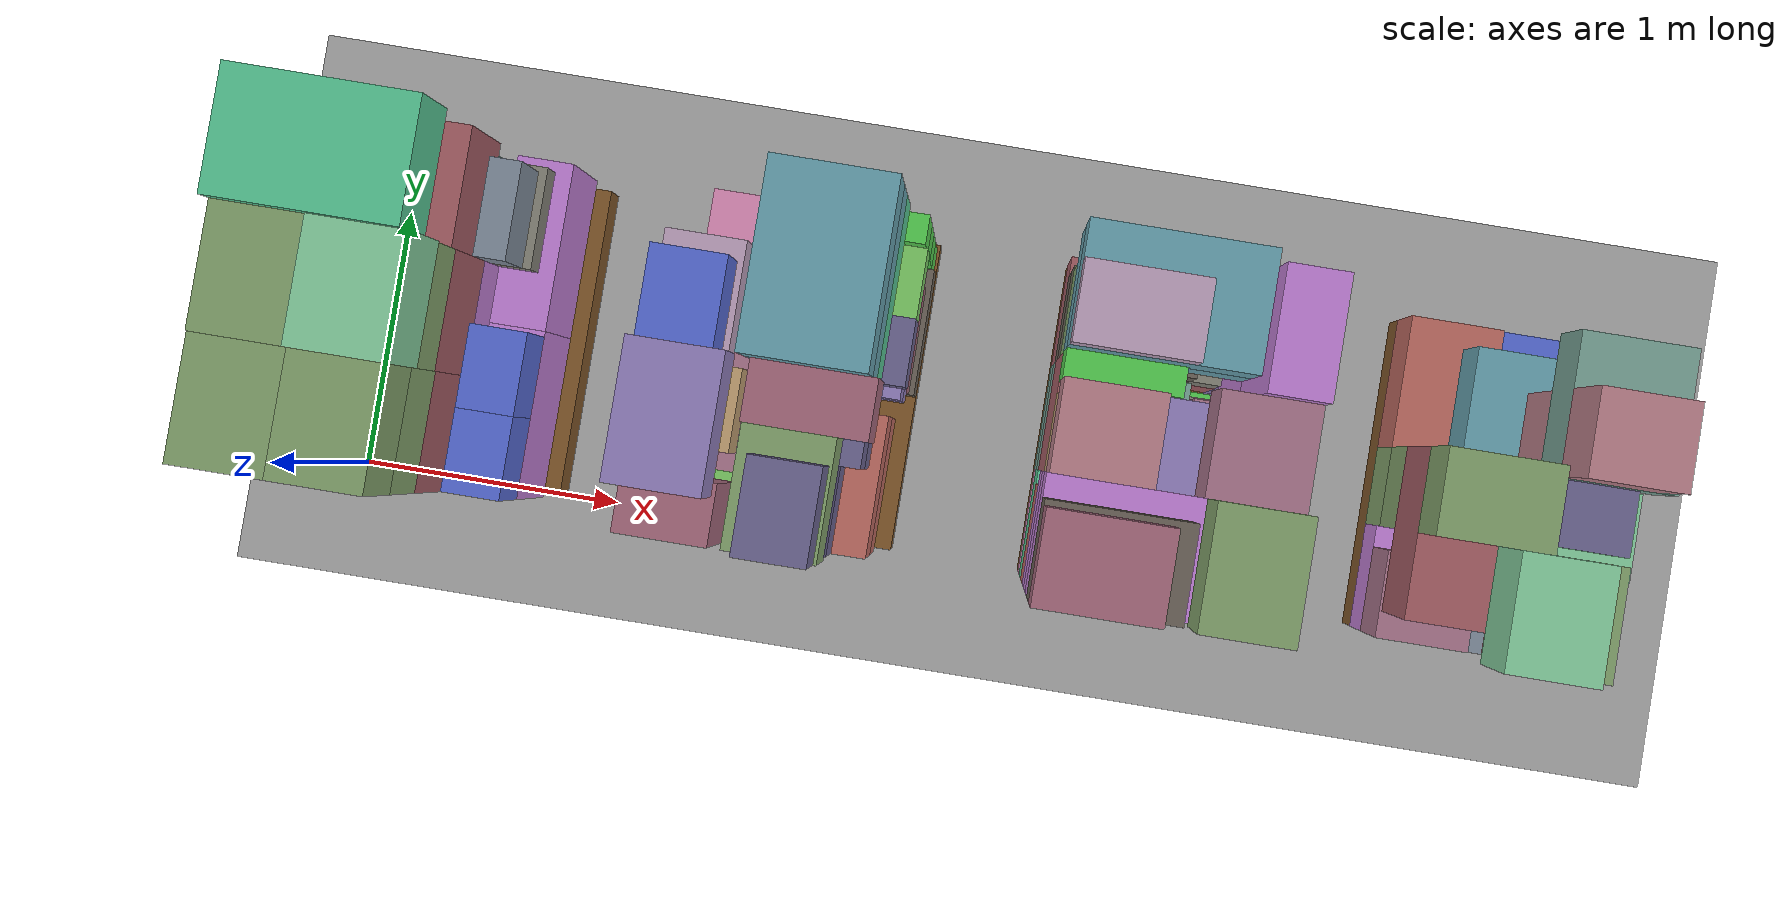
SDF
<?xml version="1.0" ?>
<sdf version="1.10">
  <world name="pallet_towers">
    <gravity>0 0 -9.81</gravity>

    <physics name="pallet_physics" type="ignored">
      <max_step_size>0.005</max_step_size>
      <real_time_factor>1.0</real_time_factor>
      <real_time_update_rate>200</real_time_update_rate>
      <max_contacts>30</max_contacts>
    </physics>

    <plugin filename="gz-sim-physics-system" name="gz::sim::systems::Physics" />
    <plugin filename="gz-sim-user-commands-system" name="gz::sim::systems::UserCommands" />
    <plugin filename="gz-sim-scene-broadcaster-system" name="gz::sim::systems::SceneBroadcaster" />

    <light type="directional" name="sun">
      <cast_shadows>true</cast_shadows>
      <pose>0 0 10 0 0 0</pose>
      <diffuse>0.8 0.8 0.8 1</diffuse>
      <specular>0.2 0.2 0.2 1</specular>
      <direction>-0.5 0.2 -0.9</direction>
    </light>

    <model name="ground_plane">
      <static>true</static>
      <link name="link">
        <collision name="collision">
          <geometry>
            <plane>
              <normal>0 0 1</normal>
              <size>30 30</size>
            </plane>
          </geometry>

          <surface>
            <friction>
              <ode>
                <mu>0.55</mu>
                <mu2>0.55</mu2>
              </ode>
            </friction>
            <bounce>
              <restitution_coefficient>0</restitution_coefficient>
              <threshold>100000</threshold>
            </bounce>
            <contact>
              <ode>
                <kp>1000000</kp>
                <kd>100</kd>
                <max_vel>1</max_vel>
                <min_depth>0.0005</min_depth>
              </ode>
            </contact>
          </surface>
        </collision>

        <visual name="visual">
          <geometry>
            <plane>
              <normal>0 0 1</normal>
              <size>30 30</size>
            </plane>
          </geometry>
          <material>
            <ambient>0.65 0.65 0.65 1</ambient>
            <diffuse>0.65 0.65 0.65 1</diffuse>
          </material>
        </visual>
      </link>
    </model>

    <model name="pallet_01_P01">
      <static>false</static>
      <pose>0.4 0.6 0.074 0 0 0</pose>
      <link name="body">
        <gravity>true</gravity>
        <inertial>
          <mass>25</mass>
          <inertia>
            <ixx>3.0432</ixx>
            <ixy>0</ixy>
            <ixz>0</ixz>
            <iyy>1.37653333</iyy>
            <iyz>0</iyz>
            <izz>4.33333333</izz>
          </inertia>
        </inertial>

        <collision name="collision">
          <geometry>
            <box>
              <size>0.8 1.2 0.144</size>
            </box>
          </geometry>

          <surface>
            <friction>
              <ode>
                <mu>0.55</mu>
                <mu2>0.55</mu2>
              </ode>
            </friction>
            <bounce>
              <restitution_coefficient>0</restitution_coefficient>
              <threshold>100000</threshold>
            </bounce>
            <contact>
              <ode>
                <kp>1000000</kp>
                <kd>100</kd>
                <max_vel>1</max_vel>
                <min_depth>0.0005</min_depth>
              </ode>
            </contact>
          </surface>
        </collision>

        <visual name="visual">
          <geometry>
            <box>
              <size>0.8 1.2 0.144</size>
            </box>
          </geometry>
          <material>
            <ambient>0.5 0.34 0.16 1</ambient>
            <diffuse>0.5 0.34 0.16 1</diffuse>
            <specular>0.05 0.05 0.05 1</specular>
          </material>
        </visual>
      </link>
    </model>
    <model name="box_p01_0001_APPLES_001_APPLES">
      <static>false</static>
      <pose>0.3 0.2 0.254 0 0 0</pose>
      <link name="body">
        <gravity>true</gravity>
        <inertial>
          <mass>12</mass>
          <inertia>
            <ixx>0.2084</ixx>
            <ixy>0</ixy>
            <ixz>0</ixz>
            <iyy>0.4084</iyy>
            <iyz>0</iyz>
            <izz>0.52</izz>
          </inertia>
        </inertial>

        <collision name="collision">
          <geometry>
            <box>
              <size>0.6 0.4 0.22</size>
            </box>
          </geometry>

          <surface>
            <friction>
              <ode>
                <mu>0.55</mu>
                <mu2>0.55</mu2>
              </ode>
            </friction>
            <bounce>
              <restitution_coefficient>0</restitution_coefficient>
              <threshold>100000</threshold>
            </bounce>
            <contact>
              <ode>
                <kp>1000000</kp>
                <kd>100</kd>
                <max_vel>1</max_vel>
                <min_depth>0.0005</min_depth>
              </ode>
            </contact>
          </surface>
        </collision>

        <visual name="visual">
          <geometry>
            <box>
              <size>0.6 0.4 0.22</size>
            </box>
          </geometry>
          <material>
            <ambient>0.4 0.635294118 0.68627451 1</ambient>
            <diffuse>0.4 0.635294118 0.68627451 1</diffuse>
            <specular>0.05 0.05 0.05 1</specular>
          </material>
        </visual>
      </link>
    </model>
    <model name="box_p01_0002_APPLES_002_APPLES">
      <static>false</static>
      <pose>0.3 0.6 0.254 0 0 0</pose>
      <link name="body">
        <gravity>true</gravity>
        <inertial>
          <mass>12</mass>
          <inertia>
            <ixx>0.2084</ixx>
            <ixy>0</ixy>
            <ixz>0</ixz>
            <iyy>0.4084</iyy>
            <iyz>0</iyz>
            <izz>0.52</izz>
          </inertia>
        </inertial>

        <collision name="collision">
          <geometry>
            <box>
              <size>0.6 0.4 0.22</size>
            </box>
          </geometry>

          <surface>
            <friction>
              <ode>
                <mu>0.55</mu>
                <mu2>0.55</mu2>
              </ode>
            </friction>
            <bounce>
              <restitution_coefficient>0</restitution_coefficient>
              <threshold>100000</threshold>
            </bounce>
            <contact>
              <ode>
                <kp>1000000</kp>
                <kd>100</kd>
                <max_vel>1</max_vel>
                <min_depth>0.0005</min_depth>
              </ode>
            </contact>
          </surface>
        </collision>

        <visual name="visual">
          <geometry>
            <box>
              <size>0.6 0.4 0.22</size>
            </box>
          </geometry>
          <material>
            <ambient>0.4 0.635294118 0.68627451 1</ambient>
            <diffuse>0.4 0.635294118 0.68627451 1</diffuse>
            <specular>0.05 0.05 0.05 1</specular>
          </material>
        </visual>
      </link>
    </model>
    <model name="box_p01_0003_APPLES_003_APPLES">
      <static>false</static>
      <pose>0.3 1 0.254 0 0 0</pose>
      <link name="body">
        <gravity>true</gravity>
        <inertial>
          <mass>12</mass>
          <inertia>
            <ixx>0.2084</ixx>
            <ixy>0</ixy>
            <ixz>0</ixz>
            <iyy>0.4084</iyy>
            <iyz>0</iyz>
            <izz>0.52</izz>
          </inertia>
        </inertial>

        <collision name="collision">
          <geometry>
            <box>
              <size>0.6 0.4 0.22</size>
            </box>
          </geometry>

          <surface>
            <friction>
              <ode>
                <mu>0.55</mu>
                <mu2>0.55</mu2>
              </ode>
            </friction>
            <bounce>
              <restitution_coefficient>0</restitution_coefficient>
              <threshold>100000</threshold>
            </bounce>
            <contact>
              <ode>
                <kp>1000000</kp>
                <kd>100</kd>
                <max_vel>1</max_vel>
                <min_depth>0.0005</min_depth>
              </ode>
            </contact>
          </surface>
        </collision>

        <visual name="visual">
          <geometry>
            <box>
              <size>0.6 0.4 0.22</size>
            </box>
          </geometry>
          <material>
            <ambient>0.4 0.635294118 0.68627451 1</ambient>
            <diffuse>0.4 0.635294118 0.68627451 1</diffuse>
            <specular>0.05 0.05 0.05 1</specular>
          </material>
        </visual>
      </link>
    </model>
    <model name="box_p01_0004_APPLES_004_APPLES">
      <static>false</static>
      <pose>0.3 0.2 0.474 0 0 0</pose>
      <link name="body">
        <gravity>true</gravity>
        <inertial>
          <mass>12</mass>
          <inertia>
            <ixx>0.2084</ixx>
            <ixy>0</ixy>
            <ixz>0</ixz>
            <iyy>0.4084</iyy>
            <iyz>0</iyz>
            <izz>0.52</izz>
          </inertia>
        </inertial>

        <collision name="collision">
          <geometry>
            <box>
              <size>0.6 0.4 0.22</size>
            </box>
          </geometry>

          <surface>
            <friction>
              <ode>
                <mu>0.55</mu>
                <mu2>0.55</mu2>
              </ode>
            </friction>
            <bounce>
              <restitution_coefficient>0</restitution_coefficient>
              <threshold>100000</threshold>
            </bounce>
            <contact>
              <ode>
                <kp>1000000</kp>
                <kd>100</kd>
                <max_vel>1</max_vel>
                <min_depth>0.0005</min_depth>
              </ode>
            </contact>
          </surface>
        </collision>

        <visual name="visual">
          <geometry>
            <box>
              <size>0.6 0.4 0.22</size>
            </box>
          </geometry>
          <material>
            <ambient>0.4 0.635294118 0.68627451 1</ambient>
            <diffuse>0.4 0.635294118 0.68627451 1</diffuse>
            <specular>0.05 0.05 0.05 1</specular>
          </material>
        </visual>
      </link>
    </model>
    <model name="box_p01_0005_BANANA_001_BANANA">
      <static>false</static>
      <pose>0.25 0.6 0.479 0 0 0</pose>
      <link name="body">
        <gravity>true</gravity>
        <inertial>
          <mass>18</mass>
          <inertia>
            <ixx>0.31935</ixx>
            <ixy>0</ixy>
            <ixz>0</ixz>
            <iyy>0.45435</iyy>
            <iyz>0</iyz>
            <izz>0.615</izz>
          </inertia>
        </inertial>

        <collision name="collision">
          <geometry>
            <box>
              <size>0.5 0.4 0.23</size>
            </box>
          </geometry>

          <surface>
            <friction>
              <ode>
                <mu>0.55</mu>
                <mu2>0.55</mu2>
              </ode>
            </friction>
            <bounce>
              <restitution_coefficient>0</restitution_coefficient>
              <threshold>100000</threshold>
            </bounce>
            <contact>
              <ode>
                <kp>1000000</kp>
                <kd>100</kd>
                <max_vel>1</max_vel>
                <min_depth>0.0005</min_depth>
              </ode>
            </contact>
          </surface>
        </collision>

        <visual name="visual">
          <geometry>
            <box>
              <size>0.5 0.4 0.23</size>
            </box>
          </geometry>
          <material>
            <ambient>0.462745098 0.635294118 0.584313725 1</ambient>
            <diffuse>0.462745098 0.635294118 0.584313725 1</diffuse>
            <specular>0.05 0.05 0.05 1</specular>
          </material>
        </visual>
      </link>
    </model>
    <model name="box_p01_0006_BANANA_002_BANANA">
      <static>false</static>
      <pose>0.25 1 0.479 0 0 0</pose>
      <link name="body">
        <gravity>true</gravity>
        <inertial>
          <mass>18</mass>
          <inertia>
            <ixx>0.31935</ixx>
            <ixy>0</ixy>
            <ixz>0</ixz>
            <iyy>0.45435</iyy>
            <iyz>0</iyz>
            <izz>0.615</izz>
          </inertia>
        </inertial>

        <collision name="collision">
          <geometry>
            <box>
              <size>0.5 0.4 0.23</size>
            </box>
          </geometry>

          <surface>
            <friction>
              <ode>
                <mu>0.55</mu>
                <mu2>0.55</mu2>
              </ode>
            </friction>
            <bounce>
              <restitution_coefficient>0</restitution_coefficient>
              <threshold>100000</threshold>
            </bounce>
            <contact>
              <ode>
                <kp>1000000</kp>
                <kd>100</kd>
                <max_vel>1</max_vel>
                <min_depth>0.0005</min_depth>
              </ode>
            </contact>
          </surface>
        </collision>

        <visual name="visual">
          <geometry>
            <box>
              <size>0.5 0.4 0.23</size>
            </box>
          </geometry>
          <material>
            <ambient>0.462745098 0.635294118 0.584313725 1</ambient>
            <diffuse>0.462745098 0.635294118 0.584313725 1</diffuse>
            <specular>0.05 0.05 0.05 1</specular>
          </material>
        </visual>
      </link>
    </model>
    <model name="box_p01_0007_BANANA_003_BANANA">
      <static>false</static>
      <pose>0.25 1 0.709 0 0 0</pose>
      <link name="body">
        <gravity>true</gravity>
        <inertial>
          <mass>18</mass>
          <inertia>
            <ixx>0.31935</ixx>
            <ixy>0</ixy>
            <ixz>0</ixz>
            <iyy>0.45435</iyy>
            <iyz>0</iyz>
            <izz>0.615</izz>
          </inertia>
        </inertial>

        <collision name="collision">
          <geometry>
            <box>
              <size>0.5 0.4 0.23</size>
            </box>
          </geometry>

          <surface>
            <friction>
              <ode>
                <mu>0.55</mu>
                <mu2>0.55</mu2>
              </ode>
            </friction>
            <bounce>
              <restitution_coefficient>0</restitution_coefficient>
              <threshold>100000</threshold>
            </bounce>
            <contact>
              <ode>
                <kp>1000000</kp>
                <kd>100</kd>
                <max_vel>1</max_vel>
                <min_depth>0.0005</min_depth>
              </ode>
            </contact>
          </surface>
        </collision>

        <visual name="visual">
          <geometry>
            <box>
              <size>0.5 0.4 0.23</size>
            </box>
          </geometry>
          <material>
            <ambient>0.462745098 0.635294118 0.584313725 1</ambient>
            <diffuse>0.462745098 0.635294118 0.584313725 1</diffuse>
            <specular>0.05 0.05 0.05 1</specular>
          </material>
        </visual>
      </link>
    </model>
    <model name="box_p01_0008_BEER24_001_BEER24">
      <static>false</static>
      <pose>0.665 0.2 0.2765 0 0 0</pose>
      <link name="body">
        <gravity>true</gravity>
        <inertial>
          <mass>9</mass>
          <inertia>
            <ixx>0.17266875</ixx>
            <ixy>0</ixy>
            <ixz>0</ixz>
            <iyy>0.06534375</iyy>
            <iyz>0</iyz>
            <izz>0.132675</izz>
          </inertia>
        </inertial>

        <collision name="collision">
          <geometry>
            <box>
              <size>0.13 0.4 0.265</size>
            </box>
          </geometry>

          <surface>
            <friction>
              <ode>
                <mu>0.55</mu>
                <mu2>0.55</mu2>
              </ode>
            </friction>
            <bounce>
              <restitution_coefficient>0</restitution_coefficient>
              <threshold>100000</threshold>
            </bounce>
            <contact>
              <ode>
                <kp>1000000</kp>
                <kd>100</kd>
                <max_vel>1</max_vel>
                <min_depth>0.0005</min_depth>
              </ode>
            </contact>
          </surface>
        </collision>

        <visual name="visual">
          <geometry>
            <box>
              <size>0.13 0.4 0.265</size>
            </box>
          </geometry>
          <material>
            <ambient>0.741176471 0.62745098 0.737254902 1</ambient>
            <diffuse>0.741176471 0.62745098 0.737254902 1</diffuse>
            <specular>0.05 0.05 0.05 1</specular>
          </material>
        </visual>
      </link>
    </model>
    <model name="box_p01_0009_BEER24_002_BEER24">
      <static>false</static>
      <pose>0.665 0.6 0.2765 0 0 0</pose>
      <link name="body">
        <gravity>true</gravity>
        <inertial>
          <mass>9</mass>
          <inertia>
            <ixx>0.17266875</ixx>
            <ixy>0</ixy>
            <ixz>0</ixz>
            <iyy>0.06534375</iyy>
            <iyz>0</iyz>
            <izz>0.132675</izz>
          </inertia>
        </inertial>

        <collision name="collision">
          <geometry>
            <box>
              <size>0.13 0.4 0.265</size>
            </box>
          </geometry>

          <surface>
            <friction>
              <ode>
                <mu>0.55</mu>
                <mu2>0.55</mu2>
              </ode>
            </friction>
            <bounce>
              <restitution_coefficient>0</restitution_coefficient>
              <threshold>100000</threshold>
            </bounce>
            <contact>
              <ode>
                <kp>1000000</kp>
                <kd>100</kd>
                <max_vel>1</max_vel>
                <min_depth>0.0005</min_depth>
              </ode>
            </contact>
          </surface>
        </collision>

        <visual name="visual">
          <geometry>
            <box>
              <size>0.13 0.4 0.265</size>
            </box>
          </geometry>
          <material>
            <ambient>0.741176471 0.62745098 0.737254902 1</ambient>
            <diffuse>0.741176471 0.62745098 0.737254902 1</diffuse>
            <specular>0.05 0.05 0.05 1</specular>
          </material>
        </visual>
      </link>
    </model>
    <model name="box_p01_0010_BEER24_003_BEER24">
      <static>false</static>
      <pose>0.665 1 0.2765 0 0 0</pose>
      <link name="body">
        <gravity>true</gravity>
        <inertial>
          <mass>9</mass>
          <inertia>
            <ixx>0.17266875</ixx>
            <ixy>0</ixy>
            <ixz>0</ixz>
            <iyy>0.06534375</iyy>
            <iyz>0</iyz>
            <izz>0.132675</izz>
          </inertia>
        </inertial>

        <collision name="collision">
          <geometry>
            <box>
              <size>0.13 0.4 0.265</size>
            </box>
          </geometry>

          <surface>
            <friction>
              <ode>
                <mu>0.55</mu>
                <mu2>0.55</mu2>
              </ode>
            </friction>
            <bounce>
              <restitution_coefficient>0</restitution_coefficient>
              <threshold>100000</threshold>
            </bounce>
            <contact>
              <ode>
                <kp>1000000</kp>
                <kd>100</kd>
                <max_vel>1</max_vel>
                <min_depth>0.0005</min_depth>
              </ode>
            </contact>
          </surface>
        </collision>

        <visual name="visual">
          <geometry>
            <box>
              <size>0.13 0.4 0.265</size>
            </box>
          </geometry>
          <material>
            <ambient>0.741176471 0.62745098 0.737254902 1</ambient>
            <diffuse>0.741176471 0.62745098 0.737254902 1</diffuse>
            <specular>0.05 0.05 0.05 1</specular>
          </material>
        </visual>
      </link>
    </model>
    <model name="box_p01_0011_BREAD_001_BREAD">
      <static>false</static>
      <pose>0.3 0.2 0.684 0 0 0</pose>
      <link name="body">
        <gravity>true</gravity>
        <inertial>
          <mass>4.5</mass>
          <inertia>
            <ixx>0.075</ixx>
            <ixy>0</ixy>
            <ixz>0</ixz>
            <iyy>0.15</iyy>
            <iyz>0</iyz>
            <izz>0.195</izz>
          </inertia>
        </inertial>

        <collision name="collision">
          <geometry>
            <box>
              <size>0.6 0.4 0.2</size>
            </box>
          </geometry>

          <surface>
            <friction>
              <ode>
                <mu>0.55</mu>
                <mu2>0.55</mu2>
              </ode>
            </friction>
            <bounce>
              <restitution_coefficient>0</restitution_coefficient>
              <threshold>100000</threshold>
            </bounce>
            <contact>
              <ode>
                <kp>1000000</kp>
                <kd>100</kd>
                <max_vel>1</max_vel>
                <min_depth>0.0005</min_depth>
              </ode>
            </contact>
          </surface>
        </collision>

        <visual name="visual">
          <geometry>
            <box>
              <size>0.6 0.4 0.2</size>
            </box>
          </geometry>
          <material>
            <ambient>0.756862745 0.498039216 0.839215686 1</ambient>
            <diffuse>0.756862745 0.498039216 0.839215686 1</diffuse>
            <specular>0.05 0.05 0.05 1</specular>
          </material>
        </visual>
      </link>
    </model>
    <model name="box_p01_0012_BREAD_002_BREAD">
      <static>false</static>
      <pose>0.3 0.6 0.694 0 0 0</pose>
      <link name="body">
        <gravity>true</gravity>
        <inertial>
          <mass>4.5</mass>
          <inertia>
            <ixx>0.075</ixx>
            <ixy>0</ixy>
            <ixz>0</ixz>
            <iyy>0.15</iyy>
            <iyz>0</iyz>
            <izz>0.195</izz>
          </inertia>
        </inertial>

        <collision name="collision">
          <geometry>
            <box>
              <size>0.6 0.4 0.2</size>
            </box>
          </geometry>

          <surface>
            <friction>
              <ode>
                <mu>0.55</mu>
                <mu2>0.55</mu2>
              </ode>
            </friction>
            <bounce>
              <restitution_coefficient>0</restitution_coefficient>
              <threshold>100000</threshold>
            </bounce>
            <contact>
              <ode>
                <kp>1000000</kp>
                <kd>100</kd>
                <max_vel>1</max_vel>
                <min_depth>0.0005</min_depth>
              </ode>
            </contact>
          </surface>
        </collision>

        <visual name="visual">
          <geometry>
            <box>
              <size>0.6 0.4 0.2</size>
            </box>
          </geometry>
          <material>
            <ambient>0.756862745 0.498039216 0.839215686 1</ambient>
            <diffuse>0.756862745 0.498039216 0.839215686 1</diffuse>
            <specular>0.05 0.05 0.05 1</specular>
          </material>
        </visual>
      </link>
    </model>
    <model name="box_p01_0013_BREAD_003_BREAD">
      <static>false</static>
      <pose>0.3 0.2 0.884 0 0 0</pose>
      <link name="body">
        <gravity>true</gravity>
        <inertial>
          <mass>4.5</mass>
          <inertia>
            <ixx>0.075</ixx>
            <ixy>0</ixy>
            <ixz>0</ixz>
            <iyy>0.15</iyy>
            <iyz>0</iyz>
            <izz>0.195</izz>
          </inertia>
        </inertial>

        <collision name="collision">
          <geometry>
            <box>
              <size>0.6 0.4 0.2</size>
            </box>
          </geometry>

          <surface>
            <friction>
              <ode>
                <mu>0.55</mu>
                <mu2>0.55</mu2>
              </ode>
            </friction>
            <bounce>
              <restitution_coefficient>0</restitution_coefficient>
              <threshold>100000</threshold>
            </bounce>
            <contact>
              <ode>
                <kp>1000000</kp>
                <kd>100</kd>
                <max_vel>1</max_vel>
                <min_depth>0.0005</min_depth>
              </ode>
            </contact>
          </surface>
        </collision>

        <visual name="visual">
          <geometry>
            <box>
              <size>0.6 0.4 0.2</size>
            </box>
          </geometry>
          <material>
            <ambient>0.756862745 0.498039216 0.839215686 1</ambient>
            <diffuse>0.756862745 0.498039216 0.839215686 1</diffuse>
            <specular>0.05 0.05 0.05 1</specular>
          </material>
        </visual>
      </link>
    </model>
    <model name="box_p01_0014_BREAD_004_BREAD">
      <static>false</static>
      <pose>0.3 0.6 0.894 0 0 0</pose>
      <link name="body">
        <gravity>true</gravity>
        <inertial>
          <mass>4.5</mass>
          <inertia>
            <ixx>0.075</ixx>
            <ixy>0</ixy>
            <ixz>0</ixz>
            <iyy>0.15</iyy>
            <iyz>0</iyz>
            <izz>0.195</izz>
          </inertia>
        </inertial>

        <collision name="collision">
          <geometry>
            <box>
              <size>0.6 0.4 0.2</size>
            </box>
          </geometry>

          <surface>
            <friction>
              <ode>
                <mu>0.55</mu>
                <mu2>0.55</mu2>
              </ode>
            </friction>
            <bounce>
              <restitution_coefficient>0</restitution_coefficient>
              <threshold>100000</threshold>
            </bounce>
            <contact>
              <ode>
                <kp>1000000</kp>
                <kd>100</kd>
                <max_vel>1</max_vel>
                <min_depth>0.0005</min_depth>
              </ode>
            </contact>
          </surface>
        </collision>

        <visual name="visual">
          <geometry>
            <box>
              <size>0.6 0.4 0.2</size>
            </box>
          </geometry>
          <material>
            <ambient>0.756862745 0.498039216 0.839215686 1</ambient>
            <diffuse>0.756862745 0.498039216 0.839215686 1</diffuse>
            <specular>0.05 0.05 0.05 1</specular>
          </material>
        </visual>
      </link>
    </model>
    <model name="box_p01_0015_BREAD_005_BREAD">
      <static>false</static>
      <pose>0.7 0.3 0.609 0 0 0</pose>
      <link name="body">
        <gravity>true</gravity>
        <inertial>
          <mass>4.5</mass>
          <inertia>
            <ixx>0.195</ixx>
            <ixy>0</ixy>
            <ixz>0</ixz>
            <iyy>0.075</iyy>
            <iyz>0</iyz>
            <izz>0.15</izz>
          </inertia>
        </inertial>

        <collision name="collision">
          <geometry>
            <box>
              <size>0.2 0.6 0.4</size>
            </box>
          </geometry>

          <surface>
            <friction>
              <ode>
                <mu>0.55</mu>
                <mu2>0.55</mu2>
              </ode>
            </friction>
            <bounce>
              <restitution_coefficient>0</restitution_coefficient>
              <threshold>100000</threshold>
            </bounce>
            <contact>
              <ode>
                <kp>1000000</kp>
                <kd>100</kd>
                <max_vel>1</max_vel>
                <min_depth>0.0005</min_depth>
              </ode>
            </contact>
          </surface>
        </collision>

        <visual name="visual">
          <geometry>
            <box>
              <size>0.2 0.6 0.4</size>
            </box>
          </geometry>
          <material>
            <ambient>0.756862745 0.498039216 0.839215686 1</ambient>
            <diffuse>0.756862745 0.498039216 0.839215686 1</diffuse>
            <specular>0.05 0.05 0.05 1</specular>
          </material>
        </visual>
      </link>
    </model>
    <model name="box_p01_0016_BREAD_006_BREAD">
      <static>false</static>
      <pose>0.7 0.9 0.609 0 0 0</pose>
      <link name="body">
        <gravity>true</gravity>
        <inertial>
          <mass>4.5</mass>
          <inertia>
            <ixx>0.195</ixx>
            <ixy>0</ixy>
            <ixz>0</ixz>
            <iyy>0.075</iyy>
            <iyz>0</iyz>
            <izz>0.15</izz>
          </inertia>
        </inertial>

        <collision name="collision">
          <geometry>
            <box>
              <size>0.2 0.6 0.4</size>
            </box>
          </geometry>

          <surface>
            <friction>
              <ode>
                <mu>0.55</mu>
                <mu2>0.55</mu2>
              </ode>
            </friction>
            <bounce>
              <restitution_coefficient>0</restitution_coefficient>
              <threshold>100000</threshold>
            </bounce>
            <contact>
              <ode>
                <kp>1000000</kp>
                <kd>100</kd>
                <max_vel>1</max_vel>
                <min_depth>0.0005</min_depth>
              </ode>
            </contact>
          </surface>
        </collision>

        <visual name="visual">
          <geometry>
            <box>
              <size>0.2 0.6 0.4</size>
            </box>
          </geometry>
          <material>
            <ambient>0.756862745 0.498039216 0.839215686 1</ambient>
            <diffuse>0.756862745 0.498039216 0.839215686 1</diffuse>
            <specular>0.05 0.05 0.05 1</specular>
          </material>
        </visual>
      </link>
    </model>
    <model name="box_p01_0017_BUTTER_001_BUTTER">
      <static>false</static>
      <pose>0.18 0.92 0.879 0 0 0</pose>
      <link name="body">
        <gravity>true</gravity>
        <inertial>
          <mass>10</mass>
          <inertia>
            <ixx>0.0580833333</ixx>
            <ixy>0</ixy>
            <ixz>0</ixz>
            <iyy>0.118083333</iyy>
            <iyz>0</iyz>
            <izz>0.156</izz>
          </inertia>
        </inertial>

        <collision name="collision">
          <geometry>
            <box>
              <size>0.36 0.24 0.11</size>
            </box>
          </geometry>

          <surface>
            <friction>
              <ode>
                <mu>0.55</mu>
                <mu2>0.55</mu2>
              </ode>
            </friction>
            <bounce>
              <restitution_coefficient>0</restitution_coefficient>
              <threshold>100000</threshold>
            </bounce>
            <contact>
              <ode>
                <kp>1000000</kp>
                <kd>100</kd>
                <max_vel>1</max_vel>
                <min_depth>0.0005</min_depth>
              </ode>
            </contact>
          </surface>
        </collision>

        <visual name="visual">
          <geometry>
            <box>
              <size>0.36 0.24 0.11</size>
            </box>
          </geometry>
          <material>
            <ambient>0.51372549 0.509803922 0.466666667 1</ambient>
            <diffuse>0.51372549 0.509803922 0.466666667 1</diffuse>
            <specular>0.05 0.05 0.05 1</specular>
          </material>
        </visual>
      </link>
    </model>
    <model name="box_p01_0018_BUTTER_002_BUTTER">
      <static>false</static>
      <pose>0.18 0.92 0.989 0 0 0</pose>
      <link name="body">
        <gravity>true</gravity>
        <inertial>
          <mass>10</mass>
          <inertia>
            <ixx>0.0580833333</ixx>
            <ixy>0</ixy>
            <ixz>0</ixz>
            <iyy>0.118083333</iyy>
            <iyz>0</iyz>
            <izz>0.156</izz>
          </inertia>
        </inertial>

        <collision name="collision">
          <geometry>
            <box>
              <size>0.36 0.24 0.11</size>
            </box>
          </geometry>

          <surface>
            <friction>
              <ode>
                <mu>0.55</mu>
                <mu2>0.55</mu2>
              </ode>
            </friction>
            <bounce>
              <restitution_coefficient>0</restitution_coefficient>
              <threshold>100000</threshold>
            </bounce>
            <contact>
              <ode>
                <kp>1000000</kp>
                <kd>100</kd>
                <max_vel>1</max_vel>
                <min_depth>0.0005</min_depth>
              </ode>
            </contact>
          </surface>
        </collision>

        <visual name="visual">
          <geometry>
            <box>
              <size>0.36 0.24 0.11</size>
            </box>
          </geometry>
          <material>
            <ambient>0.51372549 0.509803922 0.466666667 1</ambient>
            <diffuse>0.51372549 0.509803922 0.466666667 1</diffuse>
            <specular>0.05 0.05 0.05 1</specular>
          </material>
        </visual>
      </link>
    </model>
    <model name="box_p01_0019_BUTTER_003_BUTTER">
      <static>false</static>
      <pose>0.62 0.98 0.864 0 0 0</pose>
      <link name="body">
        <gravity>true</gravity>
        <inertial>
          <mass>10</mass>
          <inertia>
            <ixx>0.118083333</ixx>
            <ixy>0</ixy>
            <ixz>0</ixz>
            <iyy>0.0580833333</iyy>
            <iyz>0</iyz>
            <izz>0.156</izz>
          </inertia>
        </inertial>

        <collision name="collision">
          <geometry>
            <box>
              <size>0.24 0.36 0.11</size>
            </box>
          </geometry>

          <surface>
            <friction>
              <ode>
                <mu>0.55</mu>
                <mu2>0.55</mu2>
              </ode>
            </friction>
            <bounce>
              <restitution_coefficient>0</restitution_coefficient>
              <threshold>100000</threshold>
            </bounce>
            <contact>
              <ode>
                <kp>1000000</kp>
                <kd>100</kd>
                <max_vel>1</max_vel>
                <min_depth>0.0005</min_depth>
              </ode>
            </contact>
          </surface>
        </collision>

        <visual name="visual">
          <geometry>
            <box>
              <size>0.24 0.36 0.11</size>
            </box>
          </geometry>
          <material>
            <ambient>0.51372549 0.509803922 0.466666667 1</ambient>
            <diffuse>0.51372549 0.509803922 0.466666667 1</diffuse>
            <specular>0.05 0.05 0.05 1</specular>
          </material>
        </visual>
      </link>
    </model>
    <model name="box_p01_0020_CHIPS_001_CHIPS">
      <static>false</static>
      <pose>0.3 0.2 1.159 0 0 0</pose>
      <link name="body">
        <gravity>true</gravity>
        <inertial>
          <mass>3.5</mass>
          <inertia>
            <ixx>0.0823958333</ixx>
            <ixy>0</ixy>
            <ixz>0</ixz>
            <iyy>0.140729167</iyy>
            <iyz>0</iyz>
            <izz>0.151666667</izz>
          </inertia>
        </inertial>

        <collision name="collision">
          <geometry>
            <box>
              <size>0.6 0.4 0.35</size>
            </box>
          </geometry>

          <surface>
            <friction>
              <ode>
                <mu>0.55</mu>
                <mu2>0.55</mu2>
              </ode>
            </friction>
            <bounce>
              <restitution_coefficient>0</restitution_coefficient>
              <threshold>100000</threshold>
            </bounce>
            <contact>
              <ode>
                <kp>1000000</kp>
                <kd>100</kd>
                <max_vel>1</max_vel>
                <min_depth>0.0005</min_depth>
              </ode>
            </contact>
          </surface>
        </collision>

        <visual name="visual">
          <geometry>
            <box>
              <size>0.6 0.4 0.35</size>
            </box>
          </geometry>
          <material>
            <ambient>0.643137255 0.360784314 0.388235294 1</ambient>
            <diffuse>0.643137255 0.360784314 0.388235294 1</diffuse>
            <specular>0.05 0.05 0.05 1</specular>
          </material>
        </visual>
      </link>
    </model>
    <model name="box_p01_0021_CHIPS_002_CHIPS">
      <static>false</static>
      <pose>0.3 0.6 1.169 0 0 0</pose>
      <link name="body">
        <gravity>true</gravity>
        <inertial>
          <mass>3.5</mass>
          <inertia>
            <ixx>0.0823958333</ixx>
            <ixy>0</ixy>
            <ixz>0</ixz>
            <iyy>0.140729167</iyy>
            <iyz>0</iyz>
            <izz>0.151666667</izz>
          </inertia>
        </inertial>

        <collision name="collision">
          <geometry>
            <box>
              <size>0.6 0.4 0.35</size>
            </box>
          </geometry>

          <surface>
            <friction>
              <ode>
                <mu>0.55</mu>
                <mu2>0.55</mu2>
              </ode>
            </friction>
            <bounce>
              <restitution_coefficient>0</restitution_coefficient>
              <threshold>100000</threshold>
            </bounce>
            <contact>
              <ode>
                <kp>1000000</kp>
                <kd>100</kd>
                <max_vel>1</max_vel>
                <min_depth>0.0005</min_depth>
              </ode>
            </contact>
          </surface>
        </collision>

        <visual name="visual">
          <geometry>
            <box>
              <size>0.6 0.4 0.35</size>
            </box>
          </geometry>
          <material>
            <ambient>0.643137255 0.360784314 0.388235294 1</ambient>
            <diffuse>0.643137255 0.360784314 0.388235294 1</diffuse>
            <specular>0.05 0.05 0.05 1</specular>
          </material>
        </visual>
      </link>
    </model>
    <model name="box_p01_0022_CHIPS_003_CHIPS">
      <static>false</static>
      <pose>0.3 1 1.219 0 0 0</pose>
      <link name="body">
        <gravity>true</gravity>
        <inertial>
          <mass>3.5</mass>
          <inertia>
            <ixx>0.0823958333</ixx>
            <ixy>0</ixy>
            <ixz>0</ixz>
            <iyy>0.140729167</iyy>
            <iyz>0</iyz>
            <izz>0.151666667</izz>
          </inertia>
        </inertial>

        <collision name="collision">
          <geometry>
            <box>
              <size>0.6 0.4 0.35</size>
            </box>
          </geometry>

          <surface>
            <friction>
              <ode>
                <mu>0.55</mu>
                <mu2>0.55</mu2>
              </ode>
            </friction>
            <bounce>
              <restitution_coefficient>0</restitution_coefficient>
              <threshold>100000</threshold>
            </bounce>
            <contact>
              <ode>
                <kp>1000000</kp>
                <kd>100</kd>
                <max_vel>1</max_vel>
                <min_depth>0.0005</min_depth>
              </ode>
            </contact>
          </surface>
        </collision>

        <visual name="visual">
          <geometry>
            <box>
              <size>0.6 0.4 0.35</size>
            </box>
          </geometry>
          <material>
            <ambient>0.643137255 0.360784314 0.388235294 1</ambient>
            <diffuse>0.643137255 0.360784314 0.388235294 1</diffuse>
            <specular>0.05 0.05 0.05 1</specular>
          </material>
        </visual>
      </link>
    </model>
    <model name="box_p01_0023_CHOCO_001_CHOCO">
      <static>false</static>
      <pose>0.7 0.145 0.929 0 0 0</pose>
      <link name="body">
        <gravity>true</gravity>
        <inertial>
          <mass>6</mass>
          <inertia>
            <ixx>0.07085</ixx>
            <ixy>0</ixy>
            <ixz>0</ixz>
            <iyy>0.0488</iyy>
            <iyz>0</iyz>
            <izz>0.06205</izz>
          </inertia>
        </inertial>

        <collision name="collision">
          <geometry>
            <box>
              <size>0.2 0.29 0.24</size>
            </box>
          </geometry>

          <surface>
            <friction>
              <ode>
                <mu>0.55</mu>
                <mu2>0.55</mu2>
              </ode>
            </friction>
            <bounce>
              <restitution_coefficient>0</restitution_coefficient>
              <threshold>100000</threshold>
            </bounce>
            <contact>
              <ode>
                <kp>1000000</kp>
                <kd>100</kd>
                <max_vel>1</max_vel>
                <min_depth>0.0005</min_depth>
              </ode>
            </contact>
          </surface>
        </collision>

        <visual name="visual">
          <geometry>
            <box>
              <size>0.2 0.29 0.24</size>
            </box>
          </geometry>
          <material>
            <ambient>0.337254902 0.419607843 0.835294118 1</ambient>
            <diffuse>0.337254902 0.419607843 0.835294118 1</diffuse>
            <specular>0.05 0.05 0.05 1</specular>
          </material>
        </visual>
      </link>
    </model>
    <model name="box_p01_0024_CHOCO_002_CHOCO">
      <static>false</static>
      <pose>0.7 0.435 0.929 0 0 0</pose>
      <link name="body">
        <gravity>true</gravity>
        <inertial>
          <mass>6</mass>
          <inertia>
            <ixx>0.07085</ixx>
            <ixy>0</ixy>
            <ixz>0</ixz>
            <iyy>0.0488</iyy>
            <iyz>0</iyz>
            <izz>0.06205</izz>
          </inertia>
        </inertial>

        <collision name="collision">
          <geometry>
            <box>
              <size>0.2 0.29 0.24</size>
            </box>
          </geometry>

          <surface>
            <friction>
              <ode>
                <mu>0.55</mu>
                <mu2>0.55</mu2>
              </ode>
            </friction>
            <bounce>
              <restitution_coefficient>0</restitution_coefficient>
              <threshold>100000</threshold>
            </bounce>
            <contact>
              <ode>
                <kp>1000000</kp>
                <kd>100</kd>
                <max_vel>1</max_vel>
                <min_depth>0.0005</min_depth>
              </ode>
            </contact>
          </surface>
        </collision>

        <visual name="visual">
          <geometry>
            <box>
              <size>0.2 0.29 0.24</size>
            </box>
          </geometry>
          <material>
            <ambient>0.337254902 0.419607843 0.835294118 1</ambient>
            <diffuse>0.337254902 0.419607843 0.835294118 1</diffuse>
            <specular>0.05 0.05 0.05 1</specular>
          </material>
        </visual>
      </link>
    </model>
    <model name="box_p01_0025_COFFEE_001_COFFEE">
      <static>false</static>
      <pose>0.15 0.2 1.459 0 0 0</pose>
      <link name="body">
        <gravity>true</gravity>
        <inertial>
          <mass>13</mass>
          <inertia>
            <ixx>0.241041667</ixx>
            <ixy>0</ixy>
            <ixz>0</ixz>
            <iyy>0.165208333</iyy>
            <iyz>0</iyz>
            <izz>0.270833333</izz>
          </inertia>
        </inertial>

        <collision name="collision">
          <geometry>
            <box>
              <size>0.3 0.4 0.25</size>
            </box>
          </geometry>

          <surface>
            <friction>
              <ode>
                <mu>0.55</mu>
                <mu2>0.55</mu2>
              </ode>
            </friction>
            <bounce>
              <restitution_coefficient>0</restitution_coefficient>
              <threshold>100000</threshold>
            </bounce>
            <contact>
              <ode>
                <kp>1000000</kp>
                <kd>100</kd>
                <max_vel>1</max_vel>
                <min_depth>0.0005</min_depth>
              </ode>
            </contact>
          </surface>
        </collision>

        <visual name="visual">
          <geometry>
            <box>
              <size>0.3 0.4 0.25</size>
            </box>
          </geometry>
          <material>
            <ambient>0.505882353 0.631372549 0.419607843 1</ambient>
            <diffuse>0.505882353 0.631372549 0.419607843 1</diffuse>
            <specular>0.05 0.05 0.05 1</specular>
          </material>
        </visual>
      </link>
    </model>
    <model name="box_p01_0026_COFFEE_002_COFFEE">
      <static>false</static>
      <pose>0.45 0.2 1.459 0 0 0</pose>
      <link name="body">
        <gravity>true</gravity>
        <inertial>
          <mass>13</mass>
          <inertia>
            <ixx>0.241041667</ixx>
            <ixy>0</ixy>
            <ixz>0</ixz>
            <iyy>0.165208333</iyy>
            <iyz>0</iyz>
            <izz>0.270833333</izz>
          </inertia>
        </inertial>

        <collision name="collision">
          <geometry>
            <box>
              <size>0.3 0.4 0.25</size>
            </box>
          </geometry>

          <surface>
            <friction>
              <ode>
                <mu>0.55</mu>
                <mu2>0.55</mu2>
              </ode>
            </friction>
            <bounce>
              <restitution_coefficient>0</restitution_coefficient>
              <threshold>100000</threshold>
            </bounce>
            <contact>
              <ode>
                <kp>1000000</kp>
                <kd>100</kd>
                <max_vel>1</max_vel>
                <min_depth>0.0005</min_depth>
              </ode>
            </contact>
          </surface>
        </collision>

        <visual name="visual">
          <geometry>
            <box>
              <size>0.3 0.4 0.25</size>
            </box>
          </geometry>
          <material>
            <ambient>0.505882353 0.631372549 0.419607843 1</ambient>
            <diffuse>0.505882353 0.631372549 0.419607843 1</diffuse>
            <specular>0.05 0.05 0.05 1</specular>
          </material>
        </visual>
      </link>
    </model>
    <model name="box_p01_0027_COFFEE_003_COFFEE">
      <static>false</static>
      <pose>0.15 0.6 1.469 0 0 0</pose>
      <link name="body">
        <gravity>true</gravity>
        <inertial>
          <mass>13</mass>
          <inertia>
            <ixx>0.241041667</ixx>
            <ixy>0</ixy>
            <ixz>0</ixz>
            <iyy>0.165208333</iyy>
            <iyz>0</iyz>
            <izz>0.270833333</izz>
          </inertia>
        </inertial>

        <collision name="collision">
          <geometry>
            <box>
              <size>0.3 0.4 0.25</size>
            </box>
          </geometry>

          <surface>
            <friction>
              <ode>
                <mu>0.55</mu>
                <mu2>0.55</mu2>
              </ode>
            </friction>
            <bounce>
              <restitution_coefficient>0</restitution_coefficient>
              <threshold>100000</threshold>
            </bounce>
            <contact>
              <ode>
                <kp>1000000</kp>
                <kd>100</kd>
                <max_vel>1</max_vel>
                <min_depth>0.0005</min_depth>
              </ode>
            </contact>
          </surface>
        </collision>

        <visual name="visual">
          <geometry>
            <box>
              <size>0.3 0.4 0.25</size>
            </box>
          </geometry>
          <material>
            <ambient>0.505882353 0.631372549 0.419607843 1</ambient>
            <diffuse>0.505882353 0.631372549 0.419607843 1</diffuse>
            <specular>0.05 0.05 0.05 1</specular>
          </material>
        </visual>
      </link>
    </model>
    <model name="box_p01_0028_COFFEE_004_COFFEE">
      <static>false</static>
      <pose>0.45 0.6 1.469 0 0 0</pose>
      <link name="body">
        <gravity>true</gravity>
        <inertial>
          <mass>13</mass>
          <inertia>
            <ixx>0.241041667</ixx>
            <ixy>0</ixy>
            <ixz>0</ixz>
            <iyy>0.165208333</iyy>
            <iyz>0</iyz>
            <izz>0.270833333</izz>
          </inertia>
        </inertial>

        <collision name="collision">
          <geometry>
            <box>
              <size>0.3 0.4 0.25</size>
            </box>
          </geometry>

          <surface>
            <friction>
              <ode>
                <mu>0.55</mu>
                <mu2>0.55</mu2>
              </ode>
            </friction>
            <bounce>
              <restitution_coefficient>0</restitution_coefficient>
              <threshold>100000</threshold>
            </bounce>
            <contact>
              <ode>
                <kp>1000000</kp>
                <kd>100</kd>
                <max_vel>1</max_vel>
                <min_depth>0.0005</min_depth>
              </ode>
            </contact>
          </surface>
        </collision>

        <visual name="visual">
          <geometry>
            <box>
              <size>0.3 0.4 0.25</size>
            </box>
          </geometry>
          <material>
            <ambient>0.505882353 0.631372549 0.419607843 1</ambient>
            <diffuse>0.505882353 0.631372549 0.419607843 1</diffuse>
            <specular>0.05 0.05 0.05 1</specular>
          </material>
        </visual>
      </link>
    </model>
    <model name="box_p01_0029_COFFEE_005_COFFEE">
      <static>false</static>
      <pose>0.15 0.2 1.709 0 0 0</pose>
      <link name="body">
        <gravity>true</gravity>
        <inertial>
          <mass>13</mass>
          <inertia>
            <ixx>0.241041667</ixx>
            <ixy>0</ixy>
            <ixz>0</ixz>
            <iyy>0.165208333</iyy>
            <iyz>0</iyz>
            <izz>0.270833333</izz>
          </inertia>
        </inertial>

        <collision name="collision">
          <geometry>
            <box>
              <size>0.3 0.4 0.25</size>
            </box>
          </geometry>

          <surface>
            <friction>
              <ode>
                <mu>0.55</mu>
                <mu2>0.55</mu2>
              </ode>
            </friction>
            <bounce>
              <restitution_coefficient>0</restitution_coefficient>
              <threshold>100000</threshold>
            </bounce>
            <contact>
              <ode>
                <kp>1000000</kp>
                <kd>100</kd>
                <max_vel>1</max_vel>
                <min_depth>0.0005</min_depth>
              </ode>
            </contact>
          </surface>
        </collision>

        <visual name="visual">
          <geometry>
            <box>
              <size>0.3 0.4 0.25</size>
            </box>
          </geometry>
          <material>
            <ambient>0.505882353 0.631372549 0.419607843 1</ambient>
            <diffuse>0.505882353 0.631372549 0.419607843 1</diffuse>
            <specular>0.05 0.05 0.05 1</specular>
          </material>
        </visual>
      </link>
    </model>
    <model name="box_p01_0030_COFFEE_006_COFFEE">
      <static>false</static>
      <pose>0.45 0.2 1.709 0 0 0</pose>
      <link name="body">
        <gravity>true</gravity>
        <inertial>
          <mass>13</mass>
          <inertia>
            <ixx>0.241041667</ixx>
            <ixy>0</ixy>
            <ixz>0</ixz>
            <iyy>0.165208333</iyy>
            <iyz>0</iyz>
            <izz>0.270833333</izz>
          </inertia>
        </inertial>

        <collision name="collision">
          <geometry>
            <box>
              <size>0.3 0.4 0.25</size>
            </box>
          </geometry>

          <surface>
            <friction>
              <ode>
                <mu>0.55</mu>
                <mu2>0.55</mu2>
              </ode>
            </friction>
            <bounce>
              <restitution_coefficient>0</restitution_coefficient>
              <threshold>100000</threshold>
            </bounce>
            <contact>
              <ode>
                <kp>1000000</kp>
                <kd>100</kd>
                <max_vel>1</max_vel>
                <min_depth>0.0005</min_depth>
              </ode>
            </contact>
          </surface>
        </collision>

        <visual name="visual">
          <geometry>
            <box>
              <size>0.3 0.4 0.25</size>
            </box>
          </geometry>
          <material>
            <ambient>0.505882353 0.631372549 0.419607843 1</ambient>
            <diffuse>0.505882353 0.631372549 0.419607843 1</diffuse>
            <specular>0.05 0.05 0.05 1</specular>
          </material>
        </visual>
      </link>
    </model>
    <model name="box_p01_0031_COFFEE_007_COFFEE">
      <static>false</static>
      <pose>0.15 0.6 1.719 0 0 0</pose>
      <link name="body">
        <gravity>true</gravity>
        <inertial>
          <mass>13</mass>
          <inertia>
            <ixx>0.241041667</ixx>
            <ixy>0</ixy>
            <ixz>0</ixz>
            <iyy>0.165208333</iyy>
            <iyz>0</iyz>
            <izz>0.270833333</izz>
          </inertia>
        </inertial>

        <collision name="collision">
          <geometry>
            <box>
              <size>0.3 0.4 0.25</size>
            </box>
          </geometry>

          <surface>
            <friction>
              <ode>
                <mu>0.55</mu>
                <mu2>0.55</mu2>
              </ode>
            </friction>
            <bounce>
              <restitution_coefficient>0</restitution_coefficient>
              <threshold>100000</threshold>
            </bounce>
            <contact>
              <ode>
                <kp>1000000</kp>
                <kd>100</kd>
                <max_vel>1</max_vel>
                <min_depth>0.0005</min_depth>
              </ode>
            </contact>
          </surface>
        </collision>

        <visual name="visual">
          <geometry>
            <box>
              <size>0.3 0.4 0.25</size>
            </box>
          </geometry>
          <material>
            <ambient>0.505882353 0.631372549 0.419607843 1</ambient>
            <diffuse>0.505882353 0.631372549 0.419607843 1</diffuse>
            <specular>0.05 0.05 0.05 1</specular>
          </material>
        </visual>
      </link>
    </model>
    <model name="box_p01_0032_DETERG_001_DETERG">
      <static>false</static>
      <pose>0.16 1 1.534 0 0 0</pose>
      <link name="body">
        <gravity>true</gravity>
        <inertial>
          <mass>7</mass>
          <inertia>
            <ixx>0.139066667</ixx>
            <ixy>0</ixy>
            <ixz>0</ixz>
            <iyy>0.105466667</iyy>
            <iyz>0</iyz>
            <izz>0.153066667</izz>
          </inertia>
        </inertial>

        <collision name="collision">
          <geometry>
            <box>
              <size>0.32 0.4 0.28</size>
            </box>
          </geometry>

          <surface>
            <friction>
              <ode>
                <mu>0.55</mu>
                <mu2>0.55</mu2>
              </ode>
            </friction>
            <bounce>
              <restitution_coefficient>0</restitution_coefficient>
              <threshold>100000</threshold>
            </bounce>
            <contact>
              <ode>
                <kp>1000000</kp>
                <kd>100</kd>
                <max_vel>1</max_vel>
                <min_depth>0.0005</min_depth>
              </ode>
            </contact>
          </surface>
        </collision>

        <visual name="visual">
          <geometry>
            <box>
              <size>0.32 0.4 0.28</size>
            </box>
          </geometry>
          <material>
            <ambient>0.517647059 0.803921569 0.615686275 1</ambient>
            <diffuse>0.517647059 0.803921569 0.615686275 1</diffuse>
            <specular>0.05 0.05 0.05 1</specular>
          </material>
        </visual>
      </link>
    </model>
    <model name="box_p01_0033_DETERG_002_DETERG">
      <static>false</static>
      <pose>0.46 0.6 1.734 0 0 0</pose>
      <link name="body">
        <gravity>true</gravity>
        <inertial>
          <mass>7</mass>
          <inertia>
            <ixx>0.139066667</ixx>
            <ixy>0</ixy>
            <ixz>0</ixz>
            <iyy>0.105466667</iyy>
            <iyz>0</iyz>
            <izz>0.153066667</izz>
          </inertia>
        </inertial>

        <collision name="collision">
          <geometry>
            <box>
              <size>0.32 0.4 0.28</size>
            </box>
          </geometry>

          <surface>
            <friction>
              <ode>
                <mu>0.55</mu>
                <mu2>0.55</mu2>
              </ode>
            </friction>
            <bounce>
              <restitution_coefficient>0</restitution_coefficient>
              <threshold>100000</threshold>
            </bounce>
            <contact>
              <ode>
                <kp>1000000</kp>
                <kd>100</kd>
                <max_vel>1</max_vel>
                <min_depth>0.0005</min_depth>
              </ode>
            </contact>
          </surface>
        </collision>

        <visual name="visual">
          <geometry>
            <box>
              <size>0.32 0.4 0.28</size>
            </box>
          </geometry>
          <material>
            <ambient>0.517647059 0.803921569 0.615686275 1</ambient>
            <diffuse>0.517647059 0.803921569 0.615686275 1</diffuse>
            <specular>0.05 0.05 0.05 1</specular>
          </material>
        </visual>
      </link>
    </model>
    <model name="box_p01_0034_DIAPER_001_DIAPER">
      <static>false</static>
      <pose>0.3 1 1.799 0 0 0</pose>
      <link name="body">
        <gravity>true</gravity>
        <inertial>
          <mass>7</mass>
          <inertia>
            <ixx>0.129791667</ixx>
            <ixy>0</ixy>
            <ixz>0</ixz>
            <iyy>0.246458333</iyy>
            <iyz>0</iyz>
            <izz>0.303333333</izz>
          </inertia>
        </inertial>

        <collision name="collision">
          <geometry>
            <box>
              <size>0.6 0.4 0.25</size>
            </box>
          </geometry>

          <surface>
            <friction>
              <ode>
                <mu>0.55</mu>
                <mu2>0.55</mu2>
              </ode>
            </friction>
            <bounce>
              <restitution_coefficient>0</restitution_coefficient>
              <threshold>100000</threshold>
            </bounce>
            <contact>
              <ode>
                <kp>1000000</kp>
                <kd>100</kd>
                <max_vel>1</max_vel>
                <min_depth>0.0005</min_depth>
              </ode>
            </contact>
          </surface>
        </collision>

        <visual name="visual">
          <geometry>
            <box>
              <size>0.6 0.4 0.25</size>
            </box>
          </geometry>
          <material>
            <ambient>0.337254902 0.780392157 0.584313725 1</ambient>
            <diffuse>0.337254902 0.780392157 0.584313725 1</diffuse>
            <specular>0.05 0.05 0.05 1</specular>
          </material>
        </visual>
      </link>
    </model>
    <model name="box_p01_0035_DOGFOOD_001_DOGFOOD">
      <static>false</static>
      <pose>0.655 0.97 1.034 0 0 0</pose>
      <link name="body">
        <gravity>true</gravity>
        <inertial>
          <mass>8</mass>
          <inertia>
            <ixx>0.112333333</ixx>
            <ixy>0</ixy>
            <ixz>0</ixz>
            <iyy>0.0433333333</iyy>
            <iyz>0</iyz>
            <izz>0.0851333333</izz>
          </inertia>
        </inertial>

        <collision name="collision">
          <geometry>
            <box>
              <size>0.11 0.34 0.23</size>
            </box>
          </geometry>

          <surface>
            <friction>
              <ode>
                <mu>0.55</mu>
                <mu2>0.55</mu2>
              </ode>
            </friction>
            <bounce>
              <restitution_coefficient>0</restitution_coefficient>
              <threshold>100000</threshold>
            </bounce>
            <contact>
              <ode>
                <kp>1000000</kp>
                <kd>100</kd>
                <max_vel>1</max_vel>
                <min_depth>0.0005</min_depth>
              </ode>
            </contact>
          </surface>
        </collision>

        <visual name="visual">
          <geometry>
            <box>
              <size>0.11 0.34 0.23</size>
            </box>
          </geometry>
          <material>
            <ambient>0.498039216 0.545098039 0.607843137 1</ambient>
            <diffuse>0.498039216 0.545098039 0.607843137 1</diffuse>
            <specular>0.05 0.05 0.05 1</specular>
          </material>
        </visual>
      </link>
    </model>
    <model name="pallet_02_P02">
      <static>false</static>
      <pose>1.7 0.6 0.074 0 0 0</pose>
      <link name="body">
        <gravity>true</gravity>
        <inertial>
          <mass>25</mass>
          <inertia>
            <ixx>3.0432</ixx>
            <ixy>0</ixy>
            <ixz>0</ixz>
            <iyy>1.37653333</iyy>
            <iyz>0</iyz>
            <izz>4.33333333</izz>
          </inertia>
        </inertial>

        <collision name="collision">
          <geometry>
            <box>
              <size>0.8 1.2 0.144</size>
            </box>
          </geometry>

          <surface>
            <friction>
              <ode>
                <mu>0.55</mu>
                <mu2>0.55</mu2>
              </ode>
            </friction>
            <bounce>
              <restitution_coefficient>0</restitution_coefficient>
              <threshold>100000</threshold>
            </bounce>
            <contact>
              <ode>
                <kp>1000000</kp>
                <kd>100</kd>
                <max_vel>1</max_vel>
                <min_depth>0.0005</min_depth>
              </ode>
            </contact>
          </surface>
        </collision>

        <visual name="visual">
          <geometry>
            <box>
              <size>0.8 1.2 0.144</size>
            </box>
          </geometry>
          <material>
            <ambient>0.5 0.34 0.16 1</ambient>
            <diffuse>0.5 0.34 0.16 1</diffuse>
            <specular>0.05 0.05 0.05 1</specular>
          </material>
        </visual>
      </link>
    </model>
    <model name="box_p02_0001_EGGS_001_EGGS">
      <static>false</static>
      <pose>1.465 0.15 0.284 0 0 0</pose>
      <link name="body">
        <gravity>true</gravity>
        <inertial>
          <mass>18</mass>
          <inertia>
            <ixx>0.2526</ixx>
            <ixy>0</ixy>
            <ixz>0</ixz>
            <iyy>0.28095</iyy>
            <iyz>0</iyz>
            <izz>0.29835</izz>
          </inertia>
        </inertial>

        <collision name="collision">
          <geometry>
            <box>
              <size>0.33 0.3 0.28</size>
            </box>
          </geometry>

          <surface>
            <friction>
              <ode>
                <mu>0.55</mu>
                <mu2>0.55</mu2>
              </ode>
            </friction>
            <bounce>
              <restitution_coefficient>0</restitution_coefficient>
              <threshold>100000</threshold>
            </bounce>
            <contact>
              <ode>
                <kp>1000000</kp>
                <kd>100</kd>
                <max_vel>1</max_vel>
                <min_depth>0.0005</min_depth>
              </ode>
            </contact>
          </surface>
        </collision>

        <visual name="visual">
          <geometry>
            <box>
              <size>0.33 0.3 0.28</size>
            </box>
          </geometry>
          <material>
            <ambient>0.725490196 0.494117647 0.537254902 1</ambient>
            <diffuse>0.725490196 0.494117647 0.537254902 1</diffuse>
            <specular>0.05 0.05 0.05 1</specular>
          </material>
        </visual>
      </link>
    </model>
    <model name="box_p02_0002_EGGS_002_EGGS">
      <static>false</static>
      <pose>1.795 0.15 0.284 0 0 0</pose>
      <link name="body">
        <gravity>true</gravity>
        <inertial>
          <mass>18</mass>
          <inertia>
            <ixx>0.2526</ixx>
            <ixy>0</ixy>
            <ixz>0</ixz>
            <iyy>0.28095</iyy>
            <iyz>0</iyz>
            <izz>0.29835</izz>
          </inertia>
        </inertial>

        <collision name="collision">
          <geometry>
            <box>
              <size>0.33 0.3 0.28</size>
            </box>
          </geometry>

          <surface>
            <friction>
              <ode>
                <mu>0.55</mu>
                <mu2>0.55</mu2>
              </ode>
            </friction>
            <bounce>
              <restitution_coefficient>0</restitution_coefficient>
              <threshold>100000</threshold>
            </bounce>
            <contact>
              <ode>
                <kp>1000000</kp>
                <kd>100</kd>
                <max_vel>1</max_vel>
                <min_depth>0.0005</min_depth>
              </ode>
            </contact>
          </surface>
        </collision>

        <visual name="visual">
          <geometry>
            <box>
              <size>0.33 0.3 0.28</size>
            </box>
          </geometry>
          <material>
            <ambient>0.725490196 0.494117647 0.537254902 1</ambient>
            <diffuse>0.725490196 0.494117647 0.537254902 1</diffuse>
            <specular>0.05 0.05 0.05 1</specular>
          </material>
        </visual>
      </link>
    </model>
    <model name="box_p02_0003_EGGS_003_EGGS">
      <static>false</static>
      <pose>1.465 0.45 0.284 0 0 0</pose>
      <link name="body">
        <gravity>true</gravity>
        <inertial>
          <mass>18</mass>
          <inertia>
            <ixx>0.2526</ixx>
            <ixy>0</ixy>
            <ixz>0</ixz>
            <iyy>0.28095</iyy>
            <iyz>0</iyz>
            <izz>0.29835</izz>
          </inertia>
        </inertial>

        <collision name="collision">
          <geometry>
            <box>
              <size>0.33 0.3 0.28</size>
            </box>
          </geometry>

          <surface>
            <friction>
              <ode>
                <mu>0.55</mu>
                <mu2>0.55</mu2>
              </ode>
            </friction>
            <bounce>
              <restitution_coefficient>0</restitution_coefficient>
              <threshold>100000</threshold>
            </bounce>
            <contact>
              <ode>
                <kp>1000000</kp>
                <kd>100</kd>
                <max_vel>1</max_vel>
                <min_depth>0.0005</min_depth>
              </ode>
            </contact>
          </surface>
        </collision>

        <visual name="visual">
          <geometry>
            <box>
              <size>0.33 0.3 0.28</size>
            </box>
          </geometry>
          <material>
            <ambient>0.725490196 0.494117647 0.537254902 1</ambient>
            <diffuse>0.725490196 0.494117647 0.537254902 1</diffuse>
            <specular>0.05 0.05 0.05 1</specular>
          </material>
        </visual>
      </link>
    </model>
    <model name="box_p02_0004_EGGS_004_EGGS">
      <static>false</static>
      <pose>1.795 0.45 0.284 0 0 0</pose>
      <link name="body">
        <gravity>true</gravity>
        <inertial>
          <mass>18</mass>
          <inertia>
            <ixx>0.2526</ixx>
            <ixy>0</ixy>
            <ixz>0</ixz>
            <iyy>0.28095</iyy>
            <iyz>0</iyz>
            <izz>0.29835</izz>
          </inertia>
        </inertial>

        <collision name="collision">
          <geometry>
            <box>
              <size>0.33 0.3 0.28</size>
            </box>
          </geometry>

          <surface>
            <friction>
              <ode>
                <mu>0.55</mu>
                <mu2>0.55</mu2>
              </ode>
            </friction>
            <bounce>
              <restitution_coefficient>0</restitution_coefficient>
              <threshold>100000</threshold>
            </bounce>
            <contact>
              <ode>
                <kp>1000000</kp>
                <kd>100</kd>
                <max_vel>1</max_vel>
                <min_depth>0.0005</min_depth>
              </ode>
            </contact>
          </surface>
        </collision>

        <visual name="visual">
          <geometry>
            <box>
              <size>0.33 0.3 0.28</size>
            </box>
          </geometry>
          <material>
            <ambient>0.725490196 0.494117647 0.537254902 1</ambient>
            <diffuse>0.725490196 0.494117647 0.537254902 1</diffuse>
            <specular>0.05 0.05 0.05 1</specular>
          </material>
        </visual>
      </link>
    </model>
    <model name="box_p02_0005_FLOUR_001_FLOUR">
      <static>false</static>
      <pose>1.54 0.76 0.254 0 0 0</pose>
      <link name="body">
        <gravity>true</gravity>
        <inertial>
          <mass>15</mass>
          <inertia>
            <ixx>0.1885</ixx>
            <ixy>0</ixy>
            <ixz>0</ixz>
            <iyy>0.3485</iyy>
            <iyz>0</iyz>
            <izz>0.416</izz>
          </inertia>
        </inertial>

        <collision name="collision">
          <geometry>
            <box>
              <size>0.48 0.32 0.22</size>
            </box>
          </geometry>

          <surface>
            <friction>
              <ode>
                <mu>0.55</mu>
                <mu2>0.55</mu2>
              </ode>
            </friction>
            <bounce>
              <restitution_coefficient>0</restitution_coefficient>
              <threshold>100000</threshold>
            </bounce>
            <contact>
              <ode>
                <kp>1000000</kp>
                <kd>100</kd>
                <max_vel>1</max_vel>
                <min_depth>0.0005</min_depth>
              </ode>
            </contact>
          </surface>
        </collision>

        <visual name="visual">
          <geometry>
            <box>
              <size>0.48 0.32 0.22</size>
            </box>
          </geometry>
          <material>
            <ambient>0.411764706 0.380392157 0.341176471 1</ambient>
            <diffuse>0.411764706 0.380392157 0.341176471 1</diffuse>
            <specular>0.05 0.05 0.05 1</specular>
          </material>
        </visual>
      </link>
    </model>
    <model name="box_p02_0006_FLOUR_002_FLOUR">
      <static>false</static>
      <pose>1.94 0.84 0.254 0 0 0</pose>
      <link name="body">
        <gravity>true</gravity>
        <inertial>
          <mass>15</mass>
          <inertia>
            <ixx>0.3485</ixx>
            <ixy>0</ixy>
            <ixz>0</ixz>
            <iyy>0.1885</iyy>
            <iyz>0</iyz>
            <izz>0.416</izz>
          </inertia>
        </inertial>

        <collision name="collision">
          <geometry>
            <box>
              <size>0.32 0.48 0.22</size>
            </box>
          </geometry>

          <surface>
            <friction>
              <ode>
                <mu>0.55</mu>
                <mu2>0.55</mu2>
              </ode>
            </friction>
            <bounce>
              <restitution_coefficient>0</restitution_coefficient>
              <threshold>100000</threshold>
            </bounce>
            <contact>
              <ode>
                <kp>1000000</kp>
                <kd>100</kd>
                <max_vel>1</max_vel>
                <min_depth>0.0005</min_depth>
              </ode>
            </contact>
          </surface>
        </collision>

        <visual name="visual">
          <geometry>
            <box>
              <size>0.32 0.48 0.22</size>
            </box>
          </geometry>
          <material>
            <ambient>0.411764706 0.380392157 0.341176471 1</ambient>
            <diffuse>0.411764706 0.380392157 0.341176471 1</diffuse>
            <specular>0.05 0.05 0.05 1</specular>
          </material>
        </visual>
      </link>
    </model>
    <model name="box_p02_0007_FLOUR_003_FLOUR">
      <static>false</static>
      <pose>1.54 0.76 0.474 0 0 0</pose>
      <link name="body">
        <gravity>true</gravity>
        <inertial>
          <mass>15</mass>
          <inertia>
            <ixx>0.1885</ixx>
            <ixy>0</ixy>
            <ixz>0</ixz>
            <iyy>0.3485</iyy>
            <iyz>0</iyz>
            <izz>0.416</izz>
          </inertia>
        </inertial>

        <collision name="collision">
          <geometry>
            <box>
              <size>0.48 0.32 0.22</size>
            </box>
          </geometry>

          <surface>
            <friction>
              <ode>
                <mu>0.55</mu>
                <mu2>0.55</mu2>
              </ode>
            </friction>
            <bounce>
              <restitution_coefficient>0</restitution_coefficient>
              <threshold>100000</threshold>
            </bounce>
            <contact>
              <ode>
                <kp>1000000</kp>
                <kd>100</kd>
                <max_vel>1</max_vel>
                <min_depth>0.0005</min_depth>
              </ode>
            </contact>
          </surface>
        </collision>

        <visual name="visual">
          <geometry>
            <box>
              <size>0.48 0.32 0.22</size>
            </box>
          </geometry>
          <material>
            <ambient>0.411764706 0.380392157 0.341176471 1</ambient>
            <diffuse>0.411764706 0.380392157 0.341176471 1</diffuse>
            <specular>0.05 0.05 0.05 1</specular>
          </material>
        </visual>
      </link>
    </model>
    <model name="box_p02_0008_HONEY_001_HONEY">
      <static>false</static>
      <pose>1.465 1.05 0.229 0 0 0</pose>
      <link name="body">
        <gravity>true</gravity>
        <inertial>
          <mass>8</mass>
          <inertia>
            <ixx>0.0643333333</ixx>
            <ixy>0</ixy>
            <ixz>0</ixz>
            <iyy>0.0918666667</iyy>
            <iyz>0</iyz>
            <izz>0.117666667</izz>
          </inertia>
        </inertial>

        <collision name="collision">
          <geometry>
            <box>
              <size>0.33 0.26 0.17</size>
            </box>
          </geometry>

          <surface>
            <friction>
              <ode>
                <mu>0.55</mu>
                <mu2>0.55</mu2>
              </ode>
            </friction>
            <bounce>
              <restitution_coefficient>0</restitution_coefficient>
              <threshold>100000</threshold>
            </bounce>
            <contact>
              <ode>
                <kp>1000000</kp>
                <kd>100</kd>
                <max_vel>1</max_vel>
                <min_depth>0.0005</min_depth>
              </ode>
            </contact>
          </surface>
        </collision>

        <visual name="visual">
          <geometry>
            <box>
              <size>0.33 0.26 0.17</size>
            </box>
          </geometry>
          <material>
            <ambient>0.752941176 0.623529412 0.443137255 1</ambient>
            <diffuse>0.752941176 0.623529412 0.443137255 1</diffuse>
            <specular>0.05 0.05 0.05 1</specular>
          </material>
        </visual>
      </link>
    </model>
    <model name="box_p02_0009_HONEY_002_HONEY">
      <static>false</static>
      <pose>1.465 1.05 0.399 0 0 0</pose>
      <link name="body">
        <gravity>true</gravity>
        <inertial>
          <mass>8</mass>
          <inertia>
            <ixx>0.0643333333</ixx>
            <ixy>0</ixy>
            <ixz>0</ixz>
            <iyy>0.0918666667</iyy>
            <iyz>0</iyz>
            <izz>0.117666667</izz>
          </inertia>
        </inertial>

        <collision name="collision">
          <geometry>
            <box>
              <size>0.33 0.26 0.17</size>
            </box>
          </geometry>

          <surface>
            <friction>
              <ode>
                <mu>0.55</mu>
                <mu2>0.55</mu2>
              </ode>
            </friction>
            <bounce>
              <restitution_coefficient>0</restitution_coefficient>
              <threshold>100000</threshold>
            </bounce>
            <contact>
              <ode>
                <kp>1000000</kp>
                <kd>100</kd>
                <max_vel>1</max_vel>
                <min_depth>0.0005</min_depth>
              </ode>
            </contact>
          </surface>
        </collision>

        <visual name="visual">
          <geometry>
            <box>
              <size>0.33 0.26 0.17</size>
            </box>
          </geometry>
          <material>
            <ambient>0.752941176 0.623529412 0.443137255 1</ambient>
            <diffuse>0.752941176 0.623529412 0.443137255 1</diffuse>
            <specular>0.05 0.05 0.05 1</specular>
          </material>
        </visual>
      </link>
    </model>
    <model name="box_p02_0010_ICECRM_001_ICECRM">
      <static>false</static>
      <pose>1.93 0.8 0.464 0 0 0</pose>
      <link name="body">
        <gravity>true</gravity>
        <inertial>
          <mass>8</mass>
          <inertia>
            <ixx>0.133333333</ixx>
            <ixy>0</ixy>
            <ixz>0</ixz>
            <iyy>0.0866666667</iyy>
            <iyz>0</iyz>
            <izz>0.166666667</izz>
          </inertia>
        </inertial>

        <collision name="collision">
          <geometry>
            <box>
              <size>0.3 0.4 0.2</size>
            </box>
          </geometry>

          <surface>
            <friction>
              <ode>
                <mu>0.55</mu>
                <mu2>0.55</mu2>
              </ode>
            </friction>
            <bounce>
              <restitution_coefficient>0</restitution_coefficient>
              <threshold>100000</threshold>
            </bounce>
            <contact>
              <ode>
                <kp>1000000</kp>
                <kd>100</kd>
                <max_vel>1</max_vel>
                <min_depth>0.0005</min_depth>
              </ode>
            </contact>
          </surface>
        </collision>

        <visual name="visual">
          <geometry>
            <box>
              <size>0.3 0.4 0.2</size>
            </box>
          </geometry>
          <material>
            <ambient>0.643137255 0.403921569 0.482352941 1</ambient>
            <diffuse>0.643137255 0.403921569 0.482352941 1</diffuse>
            <specular>0.05 0.05 0.05 1</specular>
          </material>
        </visual>
      </link>
    </model>
    <model name="box_p02_0011_ICECRM_002_ICECRM">
      <static>false</static>
      <pose>1.5 0.15 0.524 0 0 0</pose>
      <link name="body">
        <gravity>true</gravity>
        <inertial>
          <mass>8</mass>
          <inertia>
            <ixx>0.0866666667</ixx>
            <ixy>0</ixy>
            <ixz>0</ixz>
            <iyy>0.133333333</iyy>
            <iyz>0</iyz>
            <izz>0.166666667</izz>
          </inertia>
        </inertial>

        <collision name="collision">
          <geometry>
            <box>
              <size>0.4 0.3 0.2</size>
            </box>
          </geometry>

          <surface>
            <friction>
              <ode>
                <mu>0.55</mu>
                <mu2>0.55</mu2>
              </ode>
            </friction>
            <bounce>
              <restitution_coefficient>0</restitution_coefficient>
              <threshold>100000</threshold>
            </bounce>
            <contact>
              <ode>
                <kp>1000000</kp>
                <kd>100</kd>
                <max_vel>1</max_vel>
                <min_depth>0.0005</min_depth>
              </ode>
            </contact>
          </surface>
        </collision>

        <visual name="visual">
          <geometry>
            <box>
              <size>0.4 0.3 0.2</size>
            </box>
          </geometry>
          <material>
            <ambient>0.643137255 0.403921569 0.482352941 1</ambient>
            <diffuse>0.643137255 0.403921569 0.482352941 1</diffuse>
            <specular>0.05 0.05 0.05 1</specular>
          </material>
        </visual>
      </link>
    </model>
    <model name="box_p02_0012_ICECRM_003_ICECRM">
      <static>false</static>
      <pose>1.5 0.45 0.524 0 0 0</pose>
      <link name="body">
        <gravity>true</gravity>
        <inertial>
          <mass>8</mass>
          <inertia>
            <ixx>0.0866666667</ixx>
            <ixy>0</ixy>
            <ixz>0</ixz>
            <iyy>0.133333333</iyy>
            <iyz>0</iyz>
            <izz>0.166666667</izz>
          </inertia>
        </inertial>

        <collision name="collision">
          <geometry>
            <box>
              <size>0.4 0.3 0.2</size>
            </box>
          </geometry>

          <surface>
            <friction>
              <ode>
                <mu>0.55</mu>
                <mu2>0.55</mu2>
              </ode>
            </friction>
            <bounce>
              <restitution_coefficient>0</restitution_coefficient>
              <threshold>100000</threshold>
            </bounce>
            <contact>
              <ode>
                <kp>1000000</kp>
                <kd>100</kd>
                <max_vel>1</max_vel>
                <min_depth>0.0005</min_depth>
              </ode>
            </contact>
          </surface>
        </collision>

        <visual name="visual">
          <geometry>
            <box>
              <size>0.4 0.3 0.2</size>
            </box>
          </geometry>
          <material>
            <ambient>0.643137255 0.403921569 0.482352941 1</ambient>
            <diffuse>0.643137255 0.403921569 0.482352941 1</diffuse>
            <specular>0.05 0.05 0.05 1</specular>
          </material>
        </visual>
      </link>
    </model>
    <model name="box_p02_0013_ONION_001_ONION">
      <static>false</static>
      <pose>1.875 0.25 0.549 0 0 0</pose>
      <link name="body">
        <gravity>true</gravity>
        <inertial>
          <mass>10</mass>
          <inertia>
            <ixx>0.260416667</ixx>
            <ixy>0</ixy>
            <ixz>0</ixz>
            <iyy>0.154166667</iyy>
            <iyz>0</iyz>
            <izz>0.310416667</izz>
          </inertia>
        </inertial>

        <collision name="collision">
          <geometry>
            <box>
              <size>0.35 0.5 0.25</size>
            </box>
          </geometry>

          <surface>
            <friction>
              <ode>
                <mu>0.55</mu>
                <mu2>0.55</mu2>
              </ode>
            </friction>
            <bounce>
              <restitution_coefficient>0</restitution_coefficient>
              <threshold>100000</threshold>
            </bounce>
            <contact>
              <ode>
                <kp>1000000</kp>
                <kd>100</kd>
                <max_vel>1</max_vel>
                <min_depth>0.0005</min_depth>
              </ode>
            </contact>
          </surface>
        </collision>

        <visual name="visual">
          <geometry>
            <box>
              <size>0.35 0.5 0.25</size>
            </box>
          </geometry>
          <material>
            <ambient>0.741176471 0.411764706 0.376470588 1</ambient>
            <diffuse>0.741176471 0.411764706 0.376470588 1</diffuse>
            <specular>0.05 0.05 0.05 1</specular>
          </material>
        </visual>
      </link>
    </model>
    <model name="box_p02_0014_ONION_002_ONION">
      <static>false</static>
      <pose>1.875 0.25 0.799 0 0 0</pose>
      <link name="body">
        <gravity>true</gravity>
        <inertial>
          <mass>10</mass>
          <inertia>
            <ixx>0.260416667</ixx>
            <ixy>0</ixy>
            <ixz>0</ixz>
            <iyy>0.154166667</iyy>
            <iyz>0</iyz>
            <izz>0.310416667</izz>
          </inertia>
        </inertial>

        <collision name="collision">
          <geometry>
            <box>
              <size>0.35 0.5 0.25</size>
            </box>
          </geometry>

          <surface>
            <friction>
              <ode>
                <mu>0.55</mu>
                <mu2>0.55</mu2>
              </ode>
            </friction>
            <bounce>
              <restitution_coefficient>0</restitution_coefficient>
              <threshold>100000</threshold>
            </bounce>
            <contact>
              <ode>
                <kp>1000000</kp>
                <kd>100</kd>
                <max_vel>1</max_vel>
                <min_depth>0.0005</min_depth>
              </ode>
            </contact>
          </surface>
        </collision>

        <visual name="visual">
          <geometry>
            <box>
              <size>0.35 0.5 0.25</size>
            </box>
          </geometry>
          <material>
            <ambient>0.741176471 0.411764706 0.376470588 1</ambient>
            <diffuse>0.741176471 0.411764706 0.376470588 1</diffuse>
            <specular>0.05 0.05 0.05 1</specular>
          </material>
        </visual>
      </link>
    </model>
    <model name="box_p02_0015_POTATO_001_POTATO">
      <static>false</static>
      <pose>1.5 0.3 0.724 0 0 0</pose>
      <link name="body">
        <gravity>true</gravity>
        <inertial>
          <mass>25</mass>
          <inertia>
            <ixx>0.833333333</ixx>
            <ixy>0</ixy>
            <ixz>0</ixz>
            <iyy>0.416666667</iyy>
            <iyz>0</iyz>
            <izz>1.08333333</izz>
          </inertia>
        </inertial>

        <collision name="collision">
          <geometry>
            <box>
              <size>0.4 0.6 0.2</size>
            </box>
          </geometry>

          <surface>
            <friction>
              <ode>
                <mu>0.55</mu>
                <mu2>0.55</mu2>
              </ode>
            </friction>
            <bounce>
              <restitution_coefficient>0</restitution_coefficient>
              <threshold>100000</threshold>
            </bounce>
            <contact>
              <ode>
                <kp>1000000</kp>
                <kd>100</kd>
                <max_vel>1</max_vel>
                <min_depth>0.0005</min_depth>
              </ode>
            </contact>
          </surface>
        </collision>

        <visual name="visual">
          <geometry>
            <box>
              <size>0.4 0.6 0.2</size>
            </box>
          </geometry>
          <material>
            <ambient>0.854901961 0.541176471 0.71372549 1</ambient>
            <diffuse>0.854901961 0.541176471 0.71372549 1</diffuse>
            <specular>0.05 0.05 0.05 1</specular>
          </material>
        </visual>
      </link>
    </model>
    <model name="box_p02_0016_POTATO_002_POTATO">
      <static>false</static>
      <pose>1.5 0.3 0.924 0 0 0</pose>
      <link name="body">
        <gravity>true</gravity>
        <inertial>
          <mass>25</mass>
          <inertia>
            <ixx>0.833333333</ixx>
            <ixy>0</ixy>
            <ixz>0</ixz>
            <iyy>0.416666667</iyy>
            <iyz>0</iyz>
            <izz>1.08333333</izz>
          </inertia>
        </inertial>

        <collision name="collision">
          <geometry>
            <box>
              <size>0.4 0.6 0.2</size>
            </box>
          </geometry>

          <surface>
            <friction>
              <ode>
                <mu>0.55</mu>
                <mu2>0.55</mu2>
              </ode>
            </friction>
            <bounce>
              <restitution_coefficient>0</restitution_coefficient>
              <threshold>100000</threshold>
            </bounce>
            <contact>
              <ode>
                <kp>1000000</kp>
                <kd>100</kd>
                <max_vel>1</max_vel>
                <min_depth>0.0005</min_depth>
              </ode>
            </contact>
          </surface>
        </collision>

        <visual name="visual">
          <geometry>
            <box>
              <size>0.4 0.6 0.2</size>
            </box>
          </geometry>
          <material>
            <ambient>0.854901961 0.541176471 0.71372549 1</ambient>
            <diffuse>0.854901961 0.541176471 0.71372549 1</diffuse>
            <specular>0.05 0.05 0.05 1</specular>
          </material>
        </visual>
      </link>
    </model>
    <model name="box_p02_0017_POTATO_003_POTATO">
      <static>false</static>
      <pose>1.5 0.9 0.684 0 0 0</pose>
      <link name="body">
        <gravity>true</gravity>
        <inertial>
          <mass>25</mass>
          <inertia>
            <ixx>0.833333333</ixx>
            <ixy>0</ixy>
            <ixz>0</ixz>
            <iyy>0.416666667</iyy>
            <iyz>0</iyz>
            <izz>1.08333333</izz>
          </inertia>
        </inertial>

        <collision name="collision">
          <geometry>
            <box>
              <size>0.4 0.6 0.2</size>
            </box>
          </geometry>

          <surface>
            <friction>
              <ode>
                <mu>0.55</mu>
                <mu2>0.55</mu2>
              </ode>
            </friction>
            <bounce>
              <restitution_coefficient>0</restitution_coefficient>
              <threshold>100000</threshold>
            </bounce>
            <contact>
              <ode>
                <kp>1000000</kp>
                <kd>100</kd>
                <max_vel>1</max_vel>
                <min_depth>0.0005</min_depth>
              </ode>
            </contact>
          </surface>
        </collision>

        <visual name="visual">
          <geometry>
            <box>
              <size>0.4 0.6 0.2</size>
            </box>
          </geometry>
          <material>
            <ambient>0.854901961 0.541176471 0.71372549 1</ambient>
            <diffuse>0.854901961 0.541176471 0.71372549 1</diffuse>
            <specular>0.05 0.05 0.05 1</specular>
          </material>
        </visual>
      </link>
    </model>
    <model name="box_p02_0018_RICE_001_RICE">
      <static>false</static>
      <pose>1.93 0.78 0.664 0 0 0</pose>
      <link name="body">
        <gravity>true</gravity>
        <inertial>
          <mass>20</mass>
          <inertia>
            <ixx>0.389333333</ixx>
            <ixy>0</ixy>
            <ixz>0</ixz>
            <iyy>0.216666667</iyy>
            <iyz>0</iyz>
            <izz>0.472666667</izz>
          </inertia>
        </inertial>

        <collision name="collision">
          <geometry>
            <box>
              <size>0.3 0.44 0.2</size>
            </box>
          </geometry>

          <surface>
            <friction>
              <ode>
                <mu>0.55</mu>
                <mu2>0.55</mu2>
              </ode>
            </friction>
            <bounce>
              <restitution_coefficient>0</restitution_coefficient>
              <threshold>100000</threshold>
            </bounce>
            <contact>
              <ode>
                <kp>1000000</kp>
                <kd>100</kd>
                <max_vel>1</max_vel>
                <min_depth>0.0005</min_depth>
              </ode>
            </contact>
          </surface>
        </collision>

        <visual name="visual">
          <geometry>
            <box>
              <size>0.3 0.44 0.2</size>
            </box>
          </geometry>
          <material>
            <ambient>0.564705882 0.494117647 0.741176471 1</ambient>
            <diffuse>0.564705882 0.494117647 0.741176471 1</diffuse>
            <specular>0.05 0.05 0.05 1</specular>
          </material>
        </visual>
      </link>
    </model>
    <model name="box_p02_0019_RICE_002_RICE">
      <static>false</static>
      <pose>1.93 0.78 0.864 0 0 0</pose>
      <link name="body">
        <gravity>true</gravity>
        <inertial>
          <mass>20</mass>
          <inertia>
            <ixx>0.389333333</ixx>
            <ixy>0</ixy>
            <ixz>0</ixz>
            <iyy>0.216666667</iyy>
            <iyz>0</iyz>
            <izz>0.472666667</izz>
          </inertia>
        </inertial>

        <collision name="collision">
          <geometry>
            <box>
              <size>0.3 0.44 0.2</size>
            </box>
          </geometry>

          <surface>
            <friction>
              <ode>
                <mu>0.55</mu>
                <mu2>0.55</mu2>
              </ode>
            </friction>
            <bounce>
              <restitution_coefficient>0</restitution_coefficient>
              <threshold>100000</threshold>
            </bounce>
            <contact>
              <ode>
                <kp>1000000</kp>
                <kd>100</kd>
                <max_vel>1</max_vel>
                <min_depth>0.0005</min_depth>
              </ode>
            </contact>
          </surface>
        </collision>

        <visual name="visual">
          <geometry>
            <box>
              <size>0.3 0.44 0.2</size>
            </box>
          </geometry>
          <material>
            <ambient>0.564705882 0.494117647 0.741176471 1</ambient>
            <diffuse>0.564705882 0.494117647 0.741176471 1</diffuse>
            <specular>0.05 0.05 0.05 1</specular>
          </material>
        </visual>
      </link>
    </model>
    <model name="box_p02_0020_RICE_003_RICE">
      <static>false</static>
      <pose>1.52 0.75 0.884 0 0 0</pose>
      <link name="body">
        <gravity>true</gravity>
        <inertial>
          <mass>20</mass>
          <inertia>
            <ixx>0.216666667</ixx>
            <ixy>0</ixy>
            <ixz>0</ixz>
            <iyy>0.389333333</iyy>
            <iyz>0</iyz>
            <izz>0.472666667</izz>
          </inertia>
        </inertial>

        <collision name="collision">
          <geometry>
            <box>
              <size>0.44 0.3 0.2</size>
            </box>
          </geometry>

          <surface>
            <friction>
              <ode>
                <mu>0.55</mu>
                <mu2>0.55</mu2>
              </ode>
            </friction>
            <bounce>
              <restitution_coefficient>0</restitution_coefficient>
              <threshold>100000</threshold>
            </bounce>
            <contact>
              <ode>
                <kp>1000000</kp>
                <kd>100</kd>
                <max_vel>1</max_vel>
                <min_depth>0.0005</min_depth>
              </ode>
            </contact>
          </surface>
        </collision>

        <visual name="visual">
          <geometry>
            <box>
              <size>0.44 0.3 0.2</size>
            </box>
          </geometry>
          <material>
            <ambient>0.564705882 0.494117647 0.741176471 1</ambient>
            <diffuse>0.564705882 0.494117647 0.741176471 1</diffuse>
            <specular>0.05 0.05 0.05 1</specular>
          </material>
        </visual>
      </link>
    </model>
    <model name="box_p02_0021_RICE_004_RICE">
      <static>false</static>
      <pose>1.52 0.75 1.084 0 0 0</pose>
      <link name="body">
        <gravity>true</gravity>
        <inertial>
          <mass>20</mass>
          <inertia>
            <ixx>0.216666667</ixx>
            <ixy>0</ixy>
            <ixz>0</ixz>
            <iyy>0.389333333</iyy>
            <iyz>0</iyz>
            <izz>0.472666667</izz>
          </inertia>
        </inertial>

        <collision name="collision">
          <geometry>
            <box>
              <size>0.44 0.3 0.2</size>
            </box>
          </geometry>

          <surface>
            <friction>
              <ode>
                <mu>0.55</mu>
                <mu2>0.55</mu2>
              </ode>
            </friction>
            <bounce>
              <restitution_coefficient>0</restitution_coefficient>
              <threshold>100000</threshold>
            </bounce>
            <contact>
              <ode>
                <kp>1000000</kp>
                <kd>100</kd>
                <max_vel>1</max_vel>
                <min_depth>0.0005</min_depth>
              </ode>
            </contact>
          </surface>
        </collision>

        <visual name="visual">
          <geometry>
            <box>
              <size>0.44 0.3 0.2</size>
            </box>
          </geometry>
          <material>
            <ambient>0.564705882 0.494117647 0.741176471 1</ambient>
            <diffuse>0.564705882 0.494117647 0.741176471 1</diffuse>
            <specular>0.05 0.05 0.05 1</specular>
          </material>
        </visual>
      </link>
    </model>
    <model name="box_p02_0022_SUGAR_001_SUGAR">
      <static>false</static>
      <pose>1.815 0.155 1.034 0 0 0</pose>
      <link name="body">
        <gravity>true</gravity>
        <inertial>
          <mass>10</mass>
          <inertia>
            <ixx>0.120416667</ixx>
            <ixy>0</ixy>
            <ixz>0</ixz>
            <iyy>0.0844166667</iyy>
            <iyz>0</iyz>
            <izz>0.124166667</izz>
          </inertia>
        </inertial>

        <collision name="collision">
          <geometry>
            <box>
              <size>0.23 0.31 0.22</size>
            </box>
          </geometry>

          <surface>
            <friction>
              <ode>
                <mu>0.55</mu>
                <mu2>0.55</mu2>
              </ode>
            </friction>
            <bounce>
              <restitution_coefficient>0</restitution_coefficient>
              <threshold>100000</threshold>
            </bounce>
            <contact>
              <ode>
                <kp>1000000</kp>
                <kd>100</kd>
                <max_vel>1</max_vel>
                <min_depth>0.0005</min_depth>
              </ode>
            </contact>
          </surface>
        </collision>

        <visual name="visual">
          <geometry>
            <box>
              <size>0.23 0.31 0.22</size>
            </box>
          </geometry>
          <material>
            <ambient>0.419607843 0.392156863 0.564705882 1</ambient>
            <diffuse>0.419607843 0.392156863 0.564705882 1</diffuse>
            <specular>0.05 0.05 0.05 1</specular>
          </material>
        </visual>
      </link>
    </model>
    <model name="box_p02_0023_SUGAR_002_SUGAR">
      <static>false</static>
      <pose>1.855 0.425 1.034 0 0 0</pose>
      <link name="body">
        <gravity>true</gravity>
        <inertial>
          <mass>10</mass>
          <inertia>
            <ixx>0.0844166667</ixx>
            <ixy>0</ixy>
            <ixz>0</ixz>
            <iyy>0.120416667</iyy>
            <iyz>0</iyz>
            <izz>0.124166667</izz>
          </inertia>
        </inertial>

        <collision name="collision">
          <geometry>
            <box>
              <size>0.31 0.23 0.22</size>
            </box>
          </geometry>

          <surface>
            <friction>
              <ode>
                <mu>0.55</mu>
                <mu2>0.55</mu2>
              </ode>
            </friction>
            <bounce>
              <restitution_coefficient>0</restitution_coefficient>
              <threshold>100000</threshold>
            </bounce>
            <contact>
              <ode>
                <kp>1000000</kp>
                <kd>100</kd>
                <max_vel>1</max_vel>
                <min_depth>0.0005</min_depth>
              </ode>
            </contact>
          </surface>
        </collision>

        <visual name="visual">
          <geometry>
            <box>
              <size>0.31 0.23 0.22</size>
            </box>
          </geometry>
          <material>
            <ambient>0.419607843 0.392156863 0.564705882 1</ambient>
            <diffuse>0.419607843 0.392156863 0.564705882 1</diffuse>
            <specular>0.05 0.05 0.05 1</specular>
          </material>
        </visual>
      </link>
    </model>
    <model name="box_p02_0024_SUGAR_003_SUGAR">
      <static>false</static>
      <pose>1.945 0.715 1.074 0 0 0</pose>
      <link name="body">
        <gravity>true</gravity>
        <inertial>
          <mass>10</mass>
          <inertia>
            <ixx>0.0844166667</ixx>
            <ixy>0</ixy>
            <ixz>0</ixz>
            <iyy>0.120416667</iyy>
            <iyz>0</iyz>
            <izz>0.124166667</izz>
          </inertia>
        </inertial>

        <collision name="collision">
          <geometry>
            <box>
              <size>0.31 0.23 0.22</size>
            </box>
          </geometry>

          <surface>
            <friction>
              <ode>
                <mu>0.55</mu>
                <mu2>0.55</mu2>
              </ode>
            </friction>
            <bounce>
              <restitution_coefficient>0</restitution_coefficient>
              <threshold>100000</threshold>
            </bounce>
            <contact>
              <ode>
                <kp>1000000</kp>
                <kd>100</kd>
                <max_vel>1</max_vel>
                <min_depth>0.0005</min_depth>
              </ode>
            </contact>
          </surface>
        </collision>

        <visual name="visual">
          <geometry>
            <box>
              <size>0.31 0.23 0.22</size>
            </box>
          </geometry>
          <material>
            <ambient>0.419607843 0.392156863 0.564705882 1</ambient>
            <diffuse>0.419607843 0.392156863 0.564705882 1</diffuse>
            <specular>0.05 0.05 0.05 1</specular>
          </material>
        </visual>
      </link>
    </model>
    <model name="box_p02_0025_SUGAR_004_SUGAR">
      <static>false</static>
      <pose>1.815 0.155 1.254 0 0 0</pose>
      <link name="body">
        <gravity>true</gravity>
        <inertial>
          <mass>10</mass>
          <inertia>
            <ixx>0.120416667</ixx>
            <ixy>0</ixy>
            <ixz>0</ixz>
            <iyy>0.0844166667</iyy>
            <iyz>0</iyz>
            <izz>0.124166667</izz>
          </inertia>
        </inertial>

        <collision name="collision">
          <geometry>
            <box>
              <size>0.23 0.31 0.22</size>
            </box>
          </geometry>

          <surface>
            <friction>
              <ode>
                <mu>0.55</mu>
                <mu2>0.55</mu2>
              </ode>
            </friction>
            <bounce>
              <restitution_coefficient>0</restitution_coefficient>
              <threshold>100000</threshold>
            </bounce>
            <contact>
              <ode>
                <kp>1000000</kp>
                <kd>100</kd>
                <max_vel>1</max_vel>
                <min_depth>0.0005</min_depth>
              </ode>
            </contact>
          </surface>
        </collision>

        <visual name="visual">
          <geometry>
            <box>
              <size>0.23 0.31 0.22</size>
            </box>
          </geometry>
          <material>
            <ambient>0.419607843 0.392156863 0.564705882 1</ambient>
            <diffuse>0.419607843 0.392156863 0.564705882 1</diffuse>
            <specular>0.05 0.05 0.05 1</specular>
          </material>
        </visual>
      </link>
    </model>
    <model name="box_p02_0026_TEA_001_TEA">
      <static>false</static>
      <pose>1.92 0.95 1.064 0 0 0</pose>
      <link name="body">
        <gravity>true</gravity>
        <inertial>
          <mass>5</mass>
          <inertia>
            <ixx>0.0406666667</ixx>
            <ixy>0</ixy>
            <ixz>0</ixz>
            <iyy>0.0706666667</iyy>
            <iyz>0</iyz>
            <izz>0.078</izz>
          </inertia>
        </inertial>

        <collision name="collision">
          <geometry>
            <box>
              <size>0.36 0.24 0.2</size>
            </box>
          </geometry>

          <surface>
            <friction>
              <ode>
                <mu>0.55</mu>
                <mu2>0.55</mu2>
              </ode>
            </friction>
            <bounce>
              <restitution_coefficient>0</restitution_coefficient>
              <threshold>100000</threshold>
            </bounce>
            <contact>
              <ode>
                <kp>1000000</kp>
                <kd>100</kd>
                <max_vel>1</max_vel>
                <min_depth>0.0005</min_depth>
              </ode>
            </contact>
          </surface>
        </collision>

        <visual name="visual">
          <geometry>
            <box>
              <size>0.36 0.24 0.2</size>
            </box>
          </geometry>
          <material>
            <ambient>0.478431373 0.788235294 0.388235294 1</ambient>
            <diffuse>0.478431373 0.788235294 0.388235294 1</diffuse>
            <specular>0.05 0.05 0.05 1</specular>
          </material>
        </visual>
      </link>
    </model>
    <model name="box_p02_0027_TEA_002_TEA">
      <static>false</static>
      <pose>1.48 0.12 1.124 0 0 0</pose>
      <link name="body">
        <gravity>true</gravity>
        <inertial>
          <mass>5</mass>
          <inertia>
            <ixx>0.0406666667</ixx>
            <ixy>0</ixy>
            <ixz>0</ixz>
            <iyy>0.0706666667</iyy>
            <iyz>0</iyz>
            <izz>0.078</izz>
          </inertia>
        </inertial>

        <collision name="collision">
          <geometry>
            <box>
              <size>0.36 0.24 0.2</size>
            </box>
          </geometry>

          <surface>
            <friction>
              <ode>
                <mu>0.55</mu>
                <mu2>0.55</mu2>
              </ode>
            </friction>
            <bounce>
              <restitution_coefficient>0</restitution_coefficient>
              <threshold>100000</threshold>
            </bounce>
            <contact>
              <ode>
                <kp>1000000</kp>
                <kd>100</kd>
                <max_vel>1</max_vel>
                <min_depth>0.0005</min_depth>
              </ode>
            </contact>
          </surface>
        </collision>

        <visual name="visual">
          <geometry>
            <box>
              <size>0.36 0.24 0.2</size>
            </box>
          </geometry>
          <material>
            <ambient>0.478431373 0.788235294 0.388235294 1</ambient>
            <diffuse>0.478431373 0.788235294 0.388235294 1</diffuse>
            <specular>0.05 0.05 0.05 1</specular>
          </material>
        </visual>
      </link>
    </model>
    <model name="box_p02_0028_WINE_001_WINE">
      <static>false</static>
      <pose>1.47 0.4 1.154 0 0 0</pose>
      <link name="body">
        <gravity>true</gravity>
        <inertial>
          <mass>18</mass>
          <inertia>
            <ixx>0.255</ixx>
            <ixy>0</ixy>
            <ixz>0</ixz>
            <iyy>0.2748</iyy>
            <iyz>0</iyz>
            <izz>0.327</izz>
          </inertia>
        </inertial>

        <collision name="collision">
          <geometry>
            <box>
              <size>0.34 0.32 0.26</size>
            </box>
          </geometry>

          <surface>
            <friction>
              <ode>
                <mu>0.55</mu>
                <mu2>0.55</mu2>
              </ode>
            </friction>
            <bounce>
              <restitution_coefficient>0</restitution_coefficient>
              <threshold>100000</threshold>
            </bounce>
            <contact>
              <ode>
                <kp>1000000</kp>
                <kd>100</kd>
                <max_vel>1</max_vel>
                <min_depth>0.0005</min_depth>
              </ode>
            </contact>
          </surface>
        </collision>

        <visual name="visual">
          <geometry>
            <box>
              <size>0.34 0.32 0.26</size>
            </box>
          </geometry>
          <material>
            <ambient>0.654901961 0.450980392 0.541176471 1</ambient>
            <diffuse>0.654901961 0.450980392 0.541176471 1</diffuse>
            <specular>0.05 0.05 0.05 1</specular>
          </material>
        </visual>
      </link>
    </model>
    <model name="box_p02_0029_WINE_002_WINE">
      <static>false</static>
      <pose>1.47 0.4 1.414 0 0 0</pose>
      <link name="body">
        <gravity>true</gravity>
        <inertial>
          <mass>18</mass>
          <inertia>
            <ixx>0.255</ixx>
            <ixy>0</ixy>
            <ixz>0</ixz>
            <iyy>0.2748</iyy>
            <iyz>0</iyz>
            <izz>0.327</izz>
          </inertia>
        </inertial>

        <collision name="collision">
          <geometry>
            <box>
              <size>0.34 0.32 0.26</size>
            </box>
          </geometry>

          <surface>
            <friction>
              <ode>
                <mu>0.55</mu>
                <mu2>0.55</mu2>
              </ode>
            </friction>
            <bounce>
              <restitution_coefficient>0</restitution_coefficient>
              <threshold>100000</threshold>
            </bounce>
            <contact>
              <ode>
                <kp>1000000</kp>
                <kd>100</kd>
                <max_vel>1</max_vel>
                <min_depth>0.0005</min_depth>
              </ode>
            </contact>
          </surface>
        </collision>

        <visual name="visual">
          <geometry>
            <box>
              <size>0.34 0.32 0.26</size>
            </box>
          </geometry>
          <material>
            <ambient>0.654901961 0.450980392 0.541176471 1</ambient>
            <diffuse>0.654901961 0.450980392 0.541176471 1</diffuse>
            <specular>0.05 0.05 0.05 1</specular>
          </material>
        </visual>
      </link>
    </model>
    <model name="box_p02_0030_WINE_003_WINE">
      <static>false</static>
      <pose>1.46 0.73 1.314 0 0 0</pose>
      <link name="body">
        <gravity>true</gravity>
        <inertial>
          <mass>18</mass>
          <inertia>
            <ixx>0.2748</ixx>
            <ixy>0</ixy>
            <ixz>0</ixz>
            <iyy>0.255</iyy>
            <iyz>0</iyz>
            <izz>0.327</izz>
          </inertia>
        </inertial>

        <collision name="collision">
          <geometry>
            <box>
              <size>0.32 0.34 0.26</size>
            </box>
          </geometry>

          <surface>
            <friction>
              <ode>
                <mu>0.55</mu>
                <mu2>0.55</mu2>
              </ode>
            </friction>
            <bounce>
              <restitution_coefficient>0</restitution_coefficient>
              <threshold>100000</threshold>
            </bounce>
            <contact>
              <ode>
                <kp>1000000</kp>
                <kd>100</kd>
                <max_vel>1</max_vel>
                <min_depth>0.0005</min_depth>
              </ode>
            </contact>
          </surface>
        </collision>

        <visual name="visual">
          <geometry>
            <box>
              <size>0.32 0.34 0.26</size>
            </box>
          </geometry>
          <material>
            <ambient>0.654901961 0.450980392 0.541176471 1</ambient>
            <diffuse>0.654901961 0.450980392 0.541176471 1</diffuse>
            <specular>0.05 0.05 0.05 1</specular>
          </material>
        </visual>
      </link>
    </model>
    <model name="box_p02_0031_YOGURT_001_YOGURT">
      <static>false</static>
      <pose>1.895 1.13 0.274 0 0 0</pose>
      <link name="body">
        <gravity>true</gravity>
        <inertial>
          <mass>5</mass>
          <inertia>
            <ixx>0.0323333333</ixx>
            <ixy>0</ixy>
            <ixz>0</ixz>
            <iyy>0.0915416667</iyy>
            <iyz>0</iyz>
            <izz>0.0675416667</izz>
          </inertia>
        </inertial>

        <collision name="collision">
          <geometry>
            <box>
              <size>0.39 0.1 0.26</size>
            </box>
          </geometry>

          <surface>
            <friction>
              <ode>
                <mu>0.55</mu>
                <mu2>0.55</mu2>
              </ode>
            </friction>
            <bounce>
              <restitution_coefficient>0</restitution_coefficient>
              <threshold>100000</threshold>
            </bounce>
            <contact>
              <ode>
                <kp>1000000</kp>
                <kd>100</kd>
                <max_vel>1</max_vel>
                <min_depth>0.0005</min_depth>
              </ode>
            </contact>
          </surface>
        </collision>

        <visual name="visual">
          <geometry>
            <box>
              <size>0.39 0.1 0.26</size>
            </box>
          </geometry>
          <material>
            <ambient>0.329411765 0.803921569 0.31372549 1</ambient>
            <diffuse>0.329411765 0.803921569 0.31372549 1</diffuse>
            <specular>0.05 0.05 0.05 1</specular>
          </material>
        </visual>
      </link>
    </model>
    <model name="box_p02_0032_YOGURT_002_YOGURT">
      <static>false</static>
      <pose>1.895 1.13 0.534 0 0 0</pose>
      <link name="body">
        <gravity>true</gravity>
        <inertial>
          <mass>5</mass>
          <inertia>
            <ixx>0.0323333333</ixx>
            <ixy>0</ixy>
            <ixz>0</ixz>
            <iyy>0.0915416667</iyy>
            <iyz>0</iyz>
            <izz>0.0675416667</izz>
          </inertia>
        </inertial>

        <collision name="collision">
          <geometry>
            <box>
              <size>0.39 0.1 0.26</size>
            </box>
          </geometry>

          <surface>
            <friction>
              <ode>
                <mu>0.55</mu>
                <mu2>0.55</mu2>
              </ode>
            </friction>
            <bounce>
              <restitution_coefficient>0</restitution_coefficient>
              <threshold>100000</threshold>
            </bounce>
            <contact>
              <ode>
                <kp>1000000</kp>
                <kd>100</kd>
                <max_vel>1</max_vel>
                <min_depth>0.0005</min_depth>
              </ode>
            </contact>
          </surface>
        </collision>

        <visual name="visual">
          <geometry>
            <box>
              <size>0.39 0.1 0.26</size>
            </box>
          </geometry>
          <material>
            <ambient>0.329411765 0.803921569 0.31372549 1</ambient>
            <diffuse>0.329411765 0.803921569 0.31372549 1</diffuse>
            <specular>0.05 0.05 0.05 1</specular>
          </material>
        </visual>
      </link>
    </model>
    <model name="box_p02_0033_YOGURT_003_YOGURT">
      <static>false</static>
      <pose>1.895 1.13 0.794 0 0 0</pose>
      <link name="body">
        <gravity>true</gravity>
        <inertial>
          <mass>5</mass>
          <inertia>
            <ixx>0.0323333333</ixx>
            <ixy>0</ixy>
            <ixz>0</ixz>
            <iyy>0.0915416667</iyy>
            <iyz>0</iyz>
            <izz>0.0675416667</izz>
          </inertia>
        </inertial>

        <collision name="collision">
          <geometry>
            <box>
              <size>0.39 0.1 0.26</size>
            </box>
          </geometry>

          <surface>
            <friction>
              <ode>
                <mu>0.55</mu>
                <mu2>0.55</mu2>
              </ode>
            </friction>
            <bounce>
              <restitution_coefficient>0</restitution_coefficient>
              <threshold>100000</threshold>
            </bounce>
            <contact>
              <ode>
                <kp>1000000</kp>
                <kd>100</kd>
                <max_vel>1</max_vel>
                <min_depth>0.0005</min_depth>
              </ode>
            </contact>
          </surface>
        </collision>

        <visual name="visual">
          <geometry>
            <box>
              <size>0.39 0.1 0.26</size>
            </box>
          </geometry>
          <material>
            <ambient>0.329411765 0.803921569 0.31372549 1</ambient>
            <diffuse>0.329411765 0.803921569 0.31372549 1</diffuse>
            <specular>0.05 0.05 0.05 1</specular>
          </material>
        </visual>
      </link>
    </model>
    <model name="box_p02_0034_YOGURT_004_YOGURT">
      <static>false</static>
      <pose>1.895 1.13 1.054 0 0 0</pose>
      <link name="body">
        <gravity>true</gravity>
        <inertial>
          <mass>5</mass>
          <inertia>
            <ixx>0.0323333333</ixx>
            <ixy>0</ixy>
            <ixz>0</ixz>
            <iyy>0.0915416667</iyy>
            <iyz>0</iyz>
            <izz>0.0675416667</izz>
          </inertia>
        </inertial>

        <collision name="collision">
          <geometry>
            <box>
              <size>0.39 0.1 0.26</size>
            </box>
          </geometry>

          <surface>
            <friction>
              <ode>
                <mu>0.55</mu>
                <mu2>0.55</mu2>
              </ode>
            </friction>
            <bounce>
              <restitution_coefficient>0</restitution_coefficient>
              <threshold>100000</threshold>
            </bounce>
            <contact>
              <ode>
                <kp>1000000</kp>
                <kd>100</kd>
                <max_vel>1</max_vel>
                <min_depth>0.0005</min_depth>
              </ode>
            </contact>
          </surface>
        </collision>

        <visual name="visual">
          <geometry>
            <box>
              <size>0.39 0.1 0.26</size>
            </box>
          </geometry>
          <material>
            <ambient>0.329411765 0.803921569 0.31372549 1</ambient>
            <diffuse>0.329411765 0.803921569 0.31372549 1</diffuse>
            <specular>0.05 0.05 0.05 1</specular>
          </material>
        </visual>
      </link>
    </model>
    <model name="box_p02_0035_DIAPER_002_DIAPER">
      <static>false</static>
      <pose>1.82 0.9 1.309 0 0 0</pose>
      <link name="body">
        <gravity>true</gravity>
        <inertial>
          <mass>7</mass>
          <inertia>
            <ixx>0.246458333</ixx>
            <ixy>0</ixy>
            <ixz>0</ixz>
            <iyy>0.129791667</iyy>
            <iyz>0</iyz>
            <izz>0.303333333</izz>
          </inertia>
        </inertial>

        <collision name="collision">
          <geometry>
            <box>
              <size>0.4 0.6 0.25</size>
            </box>
          </geometry>

          <surface>
            <friction>
              <ode>
                <mu>0.55</mu>
                <mu2>0.55</mu2>
              </ode>
            </friction>
            <bounce>
              <restitution_coefficient>0</restitution_coefficient>
              <threshold>100000</threshold>
            </bounce>
            <contact>
              <ode>
                <kp>1000000</kp>
                <kd>100</kd>
                <max_vel>1</max_vel>
                <min_depth>0.0005</min_depth>
              </ode>
            </contact>
          </surface>
        </collision>

        <visual name="visual">
          <geometry>
            <box>
              <size>0.4 0.6 0.25</size>
            </box>
          </geometry>
          <material>
            <ambient>0.337254902 0.780392157 0.584313725 1</ambient>
            <diffuse>0.337254902 0.780392157 0.584313725 1</diffuse>
            <specular>0.05 0.05 0.05 1</specular>
          </material>
        </visual>
      </link>
    </model>
    <model name="box_p02_0036_SUGAR_008_SUGAR">
      <static>false</static>
      <pose>1.855 0.425 1.254 0 0 0</pose>
      <link name="body">
        <gravity>true</gravity>
        <inertial>
          <mass>10</mass>
          <inertia>
            <ixx>0.0844166667</ixx>
            <ixy>0</ixy>
            <ixz>0</ixz>
            <iyy>0.120416667</iyy>
            <iyz>0</iyz>
            <izz>0.124166667</izz>
          </inertia>
        </inertial>

        <collision name="collision">
          <geometry>
            <box>
              <size>0.31 0.23 0.22</size>
            </box>
          </geometry>

          <surface>
            <friction>
              <ode>
                <mu>0.55</mu>
                <mu2>0.55</mu2>
              </ode>
            </friction>
            <bounce>
              <restitution_coefficient>0</restitution_coefficient>
              <threshold>100000</threshold>
            </bounce>
            <contact>
              <ode>
                <kp>1000000</kp>
                <kd>100</kd>
                <max_vel>1</max_vel>
                <min_depth>0.0005</min_depth>
              </ode>
            </contact>
          </surface>
        </collision>

        <visual name="visual">
          <geometry>
            <box>
              <size>0.31 0.23 0.22</size>
            </box>
          </geometry>
          <material>
            <ambient>0.419607843 0.392156863 0.564705882 1</ambient>
            <diffuse>0.419607843 0.392156863 0.564705882 1</diffuse>
            <specular>0.05 0.05 0.05 1</specular>
          </material>
        </visual>
      </link>
    </model>
    <model name="box_p02_0037_COFFEE_013_COFFEE">
      <static>false</static>
      <pose>1.79 0.2 1.489 0 0 0</pose>
      <link name="body">
        <gravity>true</gravity>
        <inertial>
          <mass>13</mass>
          <inertia>
            <ixx>0.241041667</ixx>
            <ixy>0</ixy>
            <ixz>0</ixz>
            <iyy>0.165208333</iyy>
            <iyz>0</iyz>
            <izz>0.270833333</izz>
          </inertia>
        </inertial>

        <collision name="collision">
          <geometry>
            <box>
              <size>0.3 0.4 0.25</size>
            </box>
          </geometry>

          <surface>
            <friction>
              <ode>
                <mu>0.55</mu>
                <mu2>0.55</mu2>
              </ode>
            </friction>
            <bounce>
              <restitution_coefficient>0</restitution_coefficient>
              <threshold>100000</threshold>
            </bounce>
            <contact>
              <ode>
                <kp>1000000</kp>
                <kd>100</kd>
                <max_vel>1</max_vel>
                <min_depth>0.0005</min_depth>
              </ode>
            </contact>
          </surface>
        </collision>

        <visual name="visual">
          <geometry>
            <box>
              <size>0.3 0.4 0.25</size>
            </box>
          </geometry>
          <material>
            <ambient>0.505882353 0.631372549 0.419607843 1</ambient>
            <diffuse>0.505882353 0.631372549 0.419607843 1</diffuse>
            <specular>0.05 0.05 0.05 1</specular>
          </material>
        </visual>
      </link>
    </model>
    <model name="box_p02_0038_APPLES_008_APPLES">
      <static>false</static>
      <pose>1.82 0.9 1.544 0 0 0</pose>
      <link name="body">
        <gravity>true</gravity>
        <inertial>
          <mass>12</mass>
          <inertia>
            <ixx>0.4084</ixx>
            <ixy>0</ixy>
            <ixz>0</ixz>
            <iyy>0.2084</iyy>
            <iyz>0</iyz>
            <izz>0.52</izz>
          </inertia>
        </inertial>

        <collision name="collision">
          <geometry>
            <box>
              <size>0.4 0.6 0.22</size>
            </box>
          </geometry>

          <surface>
            <friction>
              <ode>
                <mu>0.55</mu>
                <mu2>0.55</mu2>
              </ode>
            </friction>
            <bounce>
              <restitution_coefficient>0</restitution_coefficient>
              <threshold>100000</threshold>
            </bounce>
            <contact>
              <ode>
                <kp>1000000</kp>
                <kd>100</kd>
                <max_vel>1</max_vel>
                <min_depth>0.0005</min_depth>
              </ode>
            </contact>
          </surface>
        </collision>

        <visual name="visual">
          <geometry>
            <box>
              <size>0.4 0.6 0.22</size>
            </box>
          </geometry>
          <material>
            <ambient>0.4 0.635294118 0.68627451 1</ambient>
            <diffuse>0.4 0.635294118 0.68627451 1</diffuse>
            <specular>0.05 0.05 0.05 1</specular>
          </material>
        </visual>
      </link>
    </model>
    <model name="box_p02_0039_APPLES_007_APPLES">
      <static>false</static>
      <pose>1.82 0.9 1.764 0 0 0</pose>
      <link name="body">
        <gravity>true</gravity>
        <inertial>
          <mass>12</mass>
          <inertia>
            <ixx>0.4084</ixx>
            <ixy>0</ixy>
            <ixz>0</ixz>
            <iyy>0.2084</iyy>
            <iyz>0</iyz>
            <izz>0.52</izz>
          </inertia>
        </inertial>

        <collision name="collision">
          <geometry>
            <box>
              <size>0.4 0.6 0.22</size>
            </box>
          </geometry>

          <surface>
            <friction>
              <ode>
                <mu>0.55</mu>
                <mu2>0.55</mu2>
              </ode>
            </friction>
            <bounce>
              <restitution_coefficient>0</restitution_coefficient>
              <threshold>100000</threshold>
            </bounce>
            <contact>
              <ode>
                <kp>1000000</kp>
                <kd>100</kd>
                <max_vel>1</max_vel>
                <min_depth>0.0005</min_depth>
              </ode>
            </contact>
          </surface>
        </collision>

        <visual name="visual">
          <geometry>
            <box>
              <size>0.4 0.6 0.22</size>
            </box>
          </geometry>
          <material>
            <ambient>0.4 0.635294118 0.68627451 1</ambient>
            <diffuse>0.4 0.635294118 0.68627451 1</diffuse>
            <specular>0.05 0.05 0.05 1</specular>
          </material>
        </visual>
      </link>
    </model>
    <model name="box_p02_0040_ICECRM_004_ICECRM">
      <static>false</static>
      <pose>1.45 0.1 1.424 0 0 0</pose>
      <link name="body">
        <gravity>true</gravity>
        <inertial>
          <mass>8</mass>
          <inertia>
            <ixx>0.133333333</ixx>
            <ixy>0</ixy>
            <ixz>0</ixz>
            <iyy>0.166666667</iyy>
            <iyz>0</iyz>
            <izz>0.0866666667</izz>
          </inertia>
        </inertial>

        <collision name="collision">
          <geometry>
            <box>
              <size>0.3 0.2 0.4</size>
            </box>
          </geometry>

          <surface>
            <friction>
              <ode>
                <mu>0.55</mu>
                <mu2>0.55</mu2>
              </ode>
            </friction>
            <bounce>
              <restitution_coefficient>0</restitution_coefficient>
              <threshold>100000</threshold>
            </bounce>
            <contact>
              <ode>
                <kp>1000000</kp>
                <kd>100</kd>
                <max_vel>1</max_vel>
                <min_depth>0.0005</min_depth>
              </ode>
            </contact>
          </surface>
        </collision>

        <visual name="visual">
          <geometry>
            <box>
              <size>0.3 0.2 0.4</size>
            </box>
          </geometry>
          <material>
            <ambient>0.643137255 0.403921569 0.482352941 1</ambient>
            <diffuse>0.643137255 0.403921569 0.482352941 1</diffuse>
            <specular>0.05 0.05 0.05 1</specular>
          </material>
        </visual>
      </link>
    </model>
    <model name="box_p02_0041_BEER24_005_BEER24">
      <static>false</static>
      <pose>1.43 0.76 1.509 0 0 0</pose>
      <link name="body">
        <gravity>true</gravity>
        <inertial>
          <mass>9</mass>
          <inertia>
            <ixx>0.132675</ixx>
            <ixy>0</ixy>
            <ixz>0</ixz>
            <iyy>0.063375</iyy>
            <iyz>0</iyz>
            <izz>0.1707</izz>
          </inertia>
        </inertial>

        <collision name="collision">
          <geometry>
            <box>
              <size>0.26 0.4 0.13</size>
            </box>
          </geometry>

          <surface>
            <friction>
              <ode>
                <mu>0.55</mu>
                <mu2>0.55</mu2>
              </ode>
            </friction>
            <bounce>
              <restitution_coefficient>0</restitution_coefficient>
              <threshold>100000</threshold>
            </bounce>
            <contact>
              <ode>
                <kp>1000000</kp>
                <kd>100</kd>
                <max_vel>1</max_vel>
                <min_depth>0.0005</min_depth>
              </ode>
            </contact>
          </surface>
        </collision>

        <visual name="visual">
          <geometry>
            <box>
              <size>0.26 0.4 0.13</size>
            </box>
          </geometry>
          <material>
            <ambient>0.741176471 0.62745098 0.737254902 1</ambient>
            <diffuse>0.741176471 0.62745098 0.737254902 1</diffuse>
            <specular>0.05 0.05 0.05 1</specular>
          </material>
        </visual>
      </link>
    </model>
    <model name="box_p02_0042_ICECRM_005_ICECRM">
      <static>false</static>
      <pose>1.84 0.5 1.514 0 0 0</pose>
      <link name="body">
        <gravity>true</gravity>
        <inertial>
          <mass>8</mass>
          <inertia>
            <ixx>0.0866666667</ixx>
            <ixy>0</ixy>
            <ixz>0</ixz>
            <iyy>0.166666667</iyy>
            <iyz>0</iyz>
            <izz>0.133333333</izz>
          </inertia>
        </inertial>

        <collision name="collision">
          <geometry>
            <box>
              <size>0.4 0.2 0.3</size>
            </box>
          </geometry>

          <surface>
            <friction>
              <ode>
                <mu>0.55</mu>
                <mu2>0.55</mu2>
              </ode>
            </friction>
            <bounce>
              <restitution_coefficient>0</restitution_coefficient>
              <threshold>100000</threshold>
            </bounce>
            <contact>
              <ode>
                <kp>1000000</kp>
                <kd>100</kd>
                <max_vel>1</max_vel>
                <min_depth>0.0005</min_depth>
              </ode>
            </contact>
          </surface>
        </collision>

        <visual name="visual">
          <geometry>
            <box>
              <size>0.4 0.2 0.3</size>
            </box>
          </geometry>
          <material>
            <ambient>0.643137255 0.403921569 0.482352941 1</ambient>
            <diffuse>0.643137255 0.403921569 0.482352941 1</diffuse>
            <specular>0.05 0.05 0.05 1</specular>
          </material>
        </visual>
      </link>
    </model>
    <model name="box_p02_0043_HONEY_004_HONEY">
      <static>false</static>
      <pose>1.465 0.43 1.629 0 0 0</pose>
      <link name="body">
        <gravity>true</gravity>
        <inertial>
          <mass>8</mass>
          <inertia>
            <ixx>0.0643333333</ixx>
            <ixy>0</ixy>
            <ixz>0</ixz>
            <iyy>0.0918666667</iyy>
            <iyz>0</iyz>
            <izz>0.117666667</izz>
          </inertia>
        </inertial>

        <collision name="collision">
          <geometry>
            <box>
              <size>0.33 0.26 0.17</size>
            </box>
          </geometry>

          <surface>
            <friction>
              <ode>
                <mu>0.55</mu>
                <mu2>0.55</mu2>
              </ode>
            </friction>
            <bounce>
              <restitution_coefficient>0</restitution_coefficient>
              <threshold>100000</threshold>
            </bounce>
            <contact>
              <ode>
                <kp>1000000</kp>
                <kd>100</kd>
                <max_vel>1</max_vel>
                <min_depth>0.0005</min_depth>
              </ode>
            </contact>
          </surface>
        </collision>

        <visual name="visual">
          <geometry>
            <box>
              <size>0.33 0.26 0.17</size>
            </box>
          </geometry>
          <material>
            <ambient>0.752941176 0.623529412 0.443137255 1</ambient>
            <diffuse>0.752941176 0.623529412 0.443137255 1</diffuse>
            <specular>0.05 0.05 0.05 1</specular>
          </material>
        </visual>
      </link>
    </model>
    <model name="box_p02_0044_CHOCO_004_CHOCO">
      <static>false</static>
      <pose>1.42 0.745 1.674 0 0 0</pose>
      <link name="body">
        <gravity>true</gravity>
        <inertial>
          <mass>6</mass>
          <inertia>
            <ixx>0.06205</ixx>
            <ixy>0</ixy>
            <ixz>0</ixz>
            <iyy>0.0488</iyy>
            <iyz>0</iyz>
            <izz>0.07085</izz>
          </inertia>
        </inertial>

        <collision name="collision">
          <geometry>
            <box>
              <size>0.24 0.29 0.2</size>
            </box>
          </geometry>

          <surface>
            <friction>
              <ode>
                <mu>0.55</mu>
                <mu2>0.55</mu2>
              </ode>
            </friction>
            <bounce>
              <restitution_coefficient>0</restitution_coefficient>
              <threshold>100000</threshold>
            </bounce>
            <contact>
              <ode>
                <kp>1000000</kp>
                <kd>100</kd>
                <max_vel>1</max_vel>
                <min_depth>0.0005</min_depth>
              </ode>
            </contact>
          </surface>
        </collision>

        <visual name="visual">
          <geometry>
            <box>
              <size>0.24 0.29 0.2</size>
            </box>
          </geometry>
          <material>
            <ambient>0.337254902 0.419607843 0.835294118 1</ambient>
            <diffuse>0.337254902 0.419607843 0.835294118 1</diffuse>
            <specular>0.05 0.05 0.05 1</specular>
          </material>
        </visual>
      </link>
    </model>
    <model name="box_p02_0045_SUGAR_005_SUGAR">
      <static>false</static>
      <pose>1.815 0.155 1.724 0 0 0</pose>
      <link name="body">
        <gravity>true</gravity>
        <inertial>
          <mass>10</mass>
          <inertia>
            <ixx>0.120416667</ixx>
            <ixy>0</ixy>
            <ixz>0</ixz>
            <iyy>0.0844166667</iyy>
            <iyz>0</iyz>
            <izz>0.124166667</izz>
          </inertia>
        </inertial>

        <collision name="collision">
          <geometry>
            <box>
              <size>0.23 0.31 0.22</size>
            </box>
          </geometry>

          <surface>
            <friction>
              <ode>
                <mu>0.55</mu>
                <mu2>0.55</mu2>
              </ode>
            </friction>
            <bounce>
              <restitution_coefficient>0</restitution_coefficient>
              <threshold>100000</threshold>
            </bounce>
            <contact>
              <ode>
                <kp>1000000</kp>
                <kd>100</kd>
                <max_vel>1</max_vel>
                <min_depth>0.0005</min_depth>
              </ode>
            </contact>
          </surface>
        </collision>

        <visual name="visual">
          <geometry>
            <box>
              <size>0.23 0.31 0.22</size>
            </box>
          </geometry>
          <material>
            <ambient>0.419607843 0.392156863 0.564705882 1</ambient>
            <diffuse>0.419607843 0.392156863 0.564705882 1</diffuse>
            <specular>0.05 0.05 0.05 1</specular>
          </material>
        </visual>
      </link>
    </model>
    <model name="box_p02_0046_RICE_008_RICE">
      <static>false</static>
      <pose>1.45 0.38 1.814 0 0 0</pose>
      <link name="body">
        <gravity>true</gravity>
        <inertial>
          <mass>20</mass>
          <inertia>
            <ixx>0.389333333</ixx>
            <ixy>0</ixy>
            <ixz>0</ixz>
            <iyy>0.216666667</iyy>
            <iyz>0</iyz>
            <izz>0.472666667</izz>
          </inertia>
        </inertial>

        <collision name="collision">
          <geometry>
            <box>
              <size>0.3 0.44 0.2</size>
            </box>
          </geometry>

          <surface>
            <friction>
              <ode>
                <mu>0.55</mu>
                <mu2>0.55</mu2>
              </ode>
            </friction>
            <bounce>
              <restitution_coefficient>0</restitution_coefficient>
              <threshold>100000</threshold>
            </bounce>
            <contact>
              <ode>
                <kp>1000000</kp>
                <kd>100</kd>
                <max_vel>1</max_vel>
                <min_depth>0.0005</min_depth>
              </ode>
            </contact>
          </surface>
        </collision>

        <visual name="visual">
          <geometry>
            <box>
              <size>0.3 0.44 0.2</size>
            </box>
          </geometry>
          <material>
            <ambient>0.564705882 0.494117647 0.741176471 1</ambient>
            <diffuse>0.564705882 0.494117647 0.741176471 1</diffuse>
            <specular>0.05 0.05 0.05 1</specular>
          </material>
        </visual>
      </link>
    </model>
    <model name="pallet_03_P03">
      <static>false</static>
      <pose>3 0.6 0.074 0 0 0</pose>
      <link name="body">
        <gravity>true</gravity>
        <inertial>
          <mass>25</mass>
          <inertia>
            <ixx>3.0432</ixx>
            <ixy>0</ixy>
            <ixz>0</ixz>
            <iyy>1.37653333</iyy>
            <iyz>0</iyz>
            <izz>4.33333333</izz>
          </inertia>
        </inertial>

        <collision name="collision">
          <geometry>
            <box>
              <size>0.8 1.2 0.144</size>
            </box>
          </geometry>

          <surface>
            <friction>
              <ode>
                <mu>0.55</mu>
                <mu2>0.55</mu2>
              </ode>
            </friction>
            <bounce>
              <restitution_coefficient>0</restitution_coefficient>
              <threshold>100000</threshold>
            </bounce>
            <contact>
              <ode>
                <kp>1000000</kp>
                <kd>100</kd>
                <max_vel>1</max_vel>
                <min_depth>0.0005</min_depth>
              </ode>
            </contact>
          </surface>
        </collision>

        <visual name="visual">
          <geometry>
            <box>
              <size>0.8 1.2 0.144</size>
            </box>
          </geometry>
          <material>
            <ambient>0.5 0.34 0.16 1</ambient>
            <diffuse>0.5 0.34 0.16 1</diffuse>
            <specular>0.05 0.05 0.05 1</specular>
          </material>
        </visual>
      </link>
    </model>
    <model name="box_p03_0001_POTATO_005_POTATO">
      <static>false</static>
      <pose>2.9 0.2 0.244 0 0 0</pose>
      <link name="body">
        <gravity>true</gravity>
        <inertial>
          <mass>25</mass>
          <inertia>
            <ixx>0.416666667</ixx>
            <ixy>0</ixy>
            <ixz>0</ixz>
            <iyy>0.833333333</iyy>
            <iyz>0</iyz>
            <izz>1.08333333</izz>
          </inertia>
        </inertial>

        <collision name="collision">
          <geometry>
            <box>
              <size>0.6 0.4 0.2</size>
            </box>
          </geometry>

          <surface>
            <friction>
              <ode>
                <mu>0.55</mu>
                <mu2>0.55</mu2>
              </ode>
            </friction>
            <bounce>
              <restitution_coefficient>0</restitution_coefficient>
              <threshold>100000</threshold>
            </bounce>
            <contact>
              <ode>
                <kp>1000000</kp>
                <kd>100</kd>
                <max_vel>1</max_vel>
                <min_depth>0.0005</min_depth>
              </ode>
            </contact>
          </surface>
        </collision>

        <visual name="visual">
          <geometry>
            <box>
              <size>0.6 0.4 0.2</size>
            </box>
          </geometry>
          <material>
            <ambient>0.854901961 0.541176471 0.71372549 1</ambient>
            <diffuse>0.854901961 0.541176471 0.71372549 1</diffuse>
            <specular>0.05 0.05 0.05 1</specular>
          </material>
        </visual>
      </link>
    </model>
    <model name="box_p03_0002_BANANA_006_BANANA">
      <static>false</static>
      <pose>2.85 0.6 0.259 0 0 0</pose>
      <link name="body">
        <gravity>true</gravity>
        <inertial>
          <mass>18</mass>
          <inertia>
            <ixx>0.31935</ixx>
            <ixy>0</ixy>
            <ixz>0</ixz>
            <iyy>0.45435</iyy>
            <iyz>0</iyz>
            <izz>0.615</izz>
          </inertia>
        </inertial>

        <collision name="collision">
          <geometry>
            <box>
              <size>0.5 0.4 0.23</size>
            </box>
          </geometry>

          <surface>
            <friction>
              <ode>
                <mu>0.55</mu>
                <mu2>0.55</mu2>
              </ode>
            </friction>
            <bounce>
              <restitution_coefficient>0</restitution_coefficient>
              <threshold>100000</threshold>
            </bounce>
            <contact>
              <ode>
                <kp>1000000</kp>
                <kd>100</kd>
                <max_vel>1</max_vel>
                <min_depth>0.0005</min_depth>
              </ode>
            </contact>
          </surface>
        </collision>

        <visual name="visual">
          <geometry>
            <box>
              <size>0.5 0.4 0.23</size>
            </box>
          </geometry>
          <material>
            <ambient>0.462745098 0.635294118 0.584313725 1</ambient>
            <diffuse>0.462745098 0.635294118 0.584313725 1</diffuse>
            <specular>0.05 0.05 0.05 1</specular>
          </material>
        </visual>
      </link>
    </model>
    <model name="box_p03_0003_CHIPS_004_CHIPS">
      <static>false</static>
      <pose>2.9 1 0.319 0 0 0</pose>
      <link name="body">
        <gravity>true</gravity>
        <inertial>
          <mass>3.5</mass>
          <inertia>
            <ixx>0.0823958333</ixx>
            <ixy>0</ixy>
            <ixz>0</ixz>
            <iyy>0.140729167</iyy>
            <iyz>0</iyz>
            <izz>0.151666667</izz>
          </inertia>
        </inertial>

        <collision name="collision">
          <geometry>
            <box>
              <size>0.6 0.4 0.35</size>
            </box>
          </geometry>

          <surface>
            <friction>
              <ode>
                <mu>0.55</mu>
                <mu2>0.55</mu2>
              </ode>
            </friction>
            <bounce>
              <restitution_coefficient>0</restitution_coefficient>
              <threshold>100000</threshold>
            </bounce>
            <contact>
              <ode>
                <kp>1000000</kp>
                <kd>100</kd>
                <max_vel>1</max_vel>
                <min_depth>0.0005</min_depth>
              </ode>
            </contact>
          </surface>
        </collision>

        <visual name="visual">
          <geometry>
            <box>
              <size>0.6 0.4 0.35</size>
            </box>
          </geometry>
          <material>
            <ambient>0.643137255 0.360784314 0.388235294 1</ambient>
            <diffuse>0.643137255 0.360784314 0.388235294 1</diffuse>
            <specular>0.05 0.05 0.05 1</specular>
          </material>
        </visual>
      </link>
    </model>
    <model name="box_p03_0004_BANANA_005_BANANA">
      <static>false</static>
      <pose>2.85 0.6 0.489 0 0 0</pose>
      <link name="body">
        <gravity>true</gravity>
        <inertial>
          <mass>18</mass>
          <inertia>
            <ixx>0.31935</ixx>
            <ixy>0</ixy>
            <ixz>0</ixz>
            <iyy>0.45435</iyy>
            <iyz>0</iyz>
            <izz>0.615</izz>
          </inertia>
        </inertial>

        <collision name="collision">
          <geometry>
            <box>
              <size>0.5 0.4 0.23</size>
            </box>
          </geometry>

          <surface>
            <friction>
              <ode>
                <mu>0.55</mu>
                <mu2>0.55</mu2>
              </ode>
            </friction>
            <bounce>
              <restitution_coefficient>0</restitution_coefficient>
              <threshold>100000</threshold>
            </bounce>
            <contact>
              <ode>
                <kp>1000000</kp>
                <kd>100</kd>
                <max_vel>1</max_vel>
                <min_depth>0.0005</min_depth>
              </ode>
            </contact>
          </surface>
        </collision>

        <visual name="visual">
          <geometry>
            <box>
              <size>0.5 0.4 0.23</size>
            </box>
          </geometry>
          <material>
            <ambient>0.462745098 0.635294118 0.584313725 1</ambient>
            <diffuse>0.462745098 0.635294118 0.584313725 1</diffuse>
            <specular>0.05 0.05 0.05 1</specular>
          </material>
        </visual>
      </link>
    </model>
    <model name="box_p03_0005_YOGURT_009_YOGURT">
      <static>false</static>
      <pose>3.23 0.595 0.194 0 0 0</pose>
      <link name="body">
        <gravity>true</gravity>
        <inertial>
          <mass>5</mass>
          <inertia>
            <ixx>0.0675416667</ixx>
            <ixy>0</ixy>
            <ixz>0</ixz>
            <iyy>0.0323333333</iyy>
            <iyz>0</iyz>
            <izz>0.0915416667</izz>
          </inertia>
        </inertial>

        <collision name="collision">
          <geometry>
            <box>
              <size>0.26 0.39 0.1</size>
            </box>
          </geometry>

          <surface>
            <friction>
              <ode>
                <mu>0.55</mu>
                <mu2>0.55</mu2>
              </ode>
            </friction>
            <bounce>
              <restitution_coefficient>0</restitution_coefficient>
              <threshold>100000</threshold>
            </bounce>
            <contact>
              <ode>
                <kp>1000000</kp>
                <kd>100</kd>
                <max_vel>1</max_vel>
                <min_depth>0.0005</min_depth>
              </ode>
            </contact>
          </surface>
        </collision>

        <visual name="visual">
          <geometry>
            <box>
              <size>0.26 0.39 0.1</size>
            </box>
          </geometry>
          <material>
            <ambient>0.329411765 0.803921569 0.31372549 1</ambient>
            <diffuse>0.329411765 0.803921569 0.31372549 1</diffuse>
            <specular>0.05 0.05 0.05 1</specular>
          </material>
        </visual>
      </link>
    </model>
    <model name="box_p03_0006_BUTTER_006_BUTTER">
      <static>false</static>
      <pose>3.22 0.58 0.299 0 0 0</pose>
      <link name="body">
        <gravity>true</gravity>
        <inertial>
          <mass>10</mass>
          <inertia>
            <ixx>0.118083333</ixx>
            <ixy>0</ixy>
            <ixz>0</ixz>
            <iyy>0.0580833333</iyy>
            <iyz>0</iyz>
            <izz>0.156</izz>
          </inertia>
        </inertial>

        <collision name="collision">
          <geometry>
            <box>
              <size>0.24 0.36 0.11</size>
            </box>
          </geometry>

          <surface>
            <friction>
              <ode>
                <mu>0.55</mu>
                <mu2>0.55</mu2>
              </ode>
            </friction>
            <bounce>
              <restitution_coefficient>0</restitution_coefficient>
              <threshold>100000</threshold>
            </bounce>
            <contact>
              <ode>
                <kp>1000000</kp>
                <kd>100</kd>
                <max_vel>1</max_vel>
                <min_depth>0.0005</min_depth>
              </ode>
            </contact>
          </surface>
        </collision>

        <visual name="visual">
          <geometry>
            <box>
              <size>0.24 0.36 0.11</size>
            </box>
          </geometry>
          <material>
            <ambient>0.51372549 0.509803922 0.466666667 1</ambient>
            <diffuse>0.51372549 0.509803922 0.466666667 1</diffuse>
            <specular>0.05 0.05 0.05 1</specular>
          </material>
        </visual>
      </link>
    </model>
    <model name="box_p03_0007_DIAPER_003_DIAPER">
      <static>false</static>
      <pose>2.9 0.2 0.469 0 0 0</pose>
      <link name="body">
        <gravity>true</gravity>
        <inertial>
          <mass>7</mass>
          <inertia>
            <ixx>0.129791667</ixx>
            <ixy>0</ixy>
            <ixz>0</ixz>
            <iyy>0.246458333</iyy>
            <iyz>0</iyz>
            <izz>0.303333333</izz>
          </inertia>
        </inertial>

        <collision name="collision">
          <geometry>
            <box>
              <size>0.6 0.4 0.25</size>
            </box>
          </geometry>

          <surface>
            <friction>
              <ode>
                <mu>0.55</mu>
                <mu2>0.55</mu2>
              </ode>
            </friction>
            <bounce>
              <restitution_coefficient>0</restitution_coefficient>
              <threshold>100000</threshold>
            </bounce>
            <contact>
              <ode>
                <kp>1000000</kp>
                <kd>100</kd>
                <max_vel>1</max_vel>
                <min_depth>0.0005</min_depth>
              </ode>
            </contact>
          </surface>
        </collision>

        <visual name="visual">
          <geometry>
            <box>
              <size>0.6 0.4 0.25</size>
            </box>
          </geometry>
          <material>
            <ambient>0.337254902 0.780392157 0.584313725 1</ambient>
            <diffuse>0.337254902 0.780392157 0.584313725 1</diffuse>
            <specular>0.05 0.05 0.05 1</specular>
          </material>
        </visual>
      </link>
    </model>
    <model name="box_p03_0008_FLOUR_004_FLOUR">
      <static>false</static>
      <pose>2.84 0.96 0.604 0 0 0</pose>
      <link name="body">
        <gravity>true</gravity>
        <inertial>
          <mass>15</mass>
          <inertia>
            <ixx>0.1885</ixx>
            <ixy>0</ixy>
            <ixz>0</ixz>
            <iyy>0.3485</iyy>
            <iyz>0</iyz>
            <izz>0.416</izz>
          </inertia>
        </inertial>

        <collision name="collision">
          <geometry>
            <box>
              <size>0.48 0.32 0.22</size>
            </box>
          </geometry>

          <surface>
            <friction>
              <ode>
                <mu>0.55</mu>
                <mu2>0.55</mu2>
              </ode>
            </friction>
            <bounce>
              <restitution_coefficient>0</restitution_coefficient>
              <threshold>100000</threshold>
            </bounce>
            <contact>
              <ode>
                <kp>1000000</kp>
                <kd>100</kd>
                <max_vel>1</max_vel>
                <min_depth>0.0005</min_depth>
              </ode>
            </contact>
          </surface>
        </collision>

        <visual name="visual">
          <geometry>
            <box>
              <size>0.48 0.32 0.22</size>
            </box>
          </geometry>
          <material>
            <ambient>0.411764706 0.380392157 0.341176471 1</ambient>
            <diffuse>0.411764706 0.380392157 0.341176471 1</diffuse>
            <specular>0.05 0.05 0.05 1</specular>
          </material>
        </visual>
      </link>
    </model>
    <model name="box_p03_0009_FLOUR_005_FLOUR">
      <static>false</static>
      <pose>2.84 0.96 0.824 0 0 0</pose>
      <link name="body">
        <gravity>true</gravity>
        <inertial>
          <mass>15</mass>
          <inertia>
            <ixx>0.1885</ixx>
            <ixy>0</ixy>
            <ixz>0</ixz>
            <iyy>0.3485</iyy>
            <iyz>0</iyz>
            <izz>0.416</izz>
          </inertia>
        </inertial>

        <collision name="collision">
          <geometry>
            <box>
              <size>0.48 0.32 0.22</size>
            </box>
          </geometry>

          <surface>
            <friction>
              <ode>
                <mu>0.55</mu>
                <mu2>0.55</mu2>
              </ode>
            </friction>
            <bounce>
              <restitution_coefficient>0</restitution_coefficient>
              <threshold>100000</threshold>
            </bounce>
            <contact>
              <ode>
                <kp>1000000</kp>
                <kd>100</kd>
                <max_vel>1</max_vel>
                <min_depth>0.0005</min_depth>
              </ode>
            </contact>
          </surface>
        </collision>

        <visual name="visual">
          <geometry>
            <box>
              <size>0.48 0.32 0.22</size>
            </box>
          </geometry>
          <material>
            <ambient>0.411764706 0.380392157 0.341176471 1</ambient>
            <diffuse>0.411764706 0.380392157 0.341176471 1</diffuse>
            <specular>0.05 0.05 0.05 1</specular>
          </material>
        </visual>
      </link>
    </model>
    <model name="box_p03_0010_ONION_003_ONION">
      <static>false</static>
      <pose>2.85 0.175 0.719 0 0 0</pose>
      <link name="body">
        <gravity>true</gravity>
        <inertial>
          <mass>10</mass>
          <inertia>
            <ixx>0.154166667</ixx>
            <ixy>0</ixy>
            <ixz>0</ixz>
            <iyy>0.260416667</iyy>
            <iyz>0</iyz>
            <izz>0.310416667</izz>
          </inertia>
        </inertial>

        <collision name="collision">
          <geometry>
            <box>
              <size>0.5 0.35 0.25</size>
            </box>
          </geometry>

          <surface>
            <friction>
              <ode>
                <mu>0.55</mu>
                <mu2>0.55</mu2>
              </ode>
            </friction>
            <bounce>
              <restitution_coefficient>0</restitution_coefficient>
              <threshold>100000</threshold>
            </bounce>
            <contact>
              <ode>
                <kp>1000000</kp>
                <kd>100</kd>
                <max_vel>1</max_vel>
                <min_depth>0.0005</min_depth>
              </ode>
            </contact>
          </surface>
        </collision>

        <visual name="visual">
          <geometry>
            <box>
              <size>0.5 0.35 0.25</size>
            </box>
          </geometry>
          <material>
            <ambient>0.741176471 0.411764706 0.376470588 1</ambient>
            <diffuse>0.741176471 0.411764706 0.376470588 1</diffuse>
            <specular>0.05 0.05 0.05 1</specular>
          </material>
        </visual>
      </link>
    </model>
    <model name="box_p03_0011_BUTTER_005_BUTTER">
      <static>false</static>
      <pose>3.22 0.58 0.409 0 0 0</pose>
      <link name="body">
        <gravity>true</gravity>
        <inertial>
          <mass>10</mass>
          <inertia>
            <ixx>0.118083333</ixx>
            <ixy>0</ixy>
            <ixz>0</ixz>
            <iyy>0.0580833333</iyy>
            <iyz>0</iyz>
            <izz>0.156</izz>
          </inertia>
        </inertial>

        <collision name="collision">
          <geometry>
            <box>
              <size>0.24 0.36 0.11</size>
            </box>
          </geometry>

          <surface>
            <friction>
              <ode>
                <mu>0.55</mu>
                <mu2>0.55</mu2>
              </ode>
            </friction>
            <bounce>
              <restitution_coefficient>0</restitution_coefficient>
              <threshold>100000</threshold>
            </bounce>
            <contact>
              <ode>
                <kp>1000000</kp>
                <kd>100</kd>
                <max_vel>1</max_vel>
                <min_depth>0.0005</min_depth>
              </ode>
            </contact>
          </surface>
        </collision>

        <visual name="visual">
          <geometry>
            <box>
              <size>0.24 0.36 0.11</size>
            </box>
          </geometry>
          <material>
            <ambient>0.51372549 0.509803922 0.466666667 1</ambient>
            <diffuse>0.51372549 0.509803922 0.466666667 1</diffuse>
            <specular>0.05 0.05 0.05 1</specular>
          </material>
        </visual>
      </link>
    </model>
    <model name="box_p03_0012_WINE_006_WINE">
      <static>false</static>
      <pose>3.23 0.57 0.624 0 0 0</pose>
      <link name="body">
        <gravity>true</gravity>
        <inertial>
          <mass>18</mass>
          <inertia>
            <ixx>0.327</ixx>
            <ixy>0</ixy>
            <ixz>0</ixz>
            <iyy>0.255</iyy>
            <iyz>0</iyz>
            <izz>0.2748</izz>
          </inertia>
        </inertial>

        <collision name="collision">
          <geometry>
            <box>
              <size>0.26 0.34 0.32</size>
            </box>
          </geometry>

          <surface>
            <friction>
              <ode>
                <mu>0.55</mu>
                <mu2>0.55</mu2>
              </ode>
            </friction>
            <bounce>
              <restitution_coefficient>0</restitution_coefficient>
              <threshold>100000</threshold>
            </bounce>
            <contact>
              <ode>
                <kp>1000000</kp>
                <kd>100</kd>
                <max_vel>1</max_vel>
                <min_depth>0.0005</min_depth>
              </ode>
            </contact>
          </surface>
        </collision>

        <visual name="visual">
          <geometry>
            <box>
              <size>0.26 0.34 0.32</size>
            </box>
          </geometry>
          <material>
            <ambient>0.654901961 0.450980392 0.541176471 1</ambient>
            <diffuse>0.654901961 0.450980392 0.541176471 1</diffuse>
            <specular>0.05 0.05 0.05 1</specular>
          </material>
        </visual>
      </link>
    </model>
    <model name="box_p03_0013_POTATO_004_POTATO">
      <static>false</static>
      <pose>3.3 0.2 0.444 0 0 0</pose>
      <link name="body">
        <gravity>true</gravity>
        <inertial>
          <mass>25</mass>
          <inertia>
            <ixx>1.08333333</ixx>
            <ixy>0</ixy>
            <ixz>0</ixz>
            <iyy>0.833333333</iyy>
            <iyz>0</iyz>
            <izz>0.416666667</izz>
          </inertia>
        </inertial>

        <collision name="collision">
          <geometry>
            <box>
              <size>0.2 0.4 0.6</size>
            </box>
          </geometry>

          <surface>
            <friction>
              <ode>
                <mu>0.55</mu>
                <mu2>0.55</mu2>
              </ode>
            </friction>
            <bounce>
              <restitution_coefficient>0</restitution_coefficient>
              <threshold>100000</threshold>
            </bounce>
            <contact>
              <ode>
                <kp>1000000</kp>
                <kd>100</kd>
                <max_vel>1</max_vel>
                <min_depth>0.0005</min_depth>
              </ode>
            </contact>
          </surface>
        </collision>

        <visual name="visual">
          <geometry>
            <box>
              <size>0.2 0.4 0.6</size>
            </box>
          </geometry>
          <material>
            <ambient>0.854901961 0.541176471 0.71372549 1</ambient>
            <diffuse>0.854901961 0.541176471 0.71372549 1</diffuse>
            <specular>0.05 0.05 0.05 1</specular>
          </material>
        </visual>
      </link>
    </model>
    <model name="box_p03_0014_RICE_007_RICE">
      <static>false</static>
      <pose>3.3 0.94 0.364 0 0 0</pose>
      <link name="body">
        <gravity>true</gravity>
        <inertial>
          <mass>20</mass>
          <inertia>
            <ixx>0.472666667</ixx>
            <ixy>0</ixy>
            <ixz>0</ixz>
            <iyy>0.389333333</iyy>
            <iyz>0</iyz>
            <izz>0.216666667</izz>
          </inertia>
        </inertial>

        <collision name="collision">
          <geometry>
            <box>
              <size>0.2 0.3 0.44</size>
            </box>
          </geometry>

          <surface>
            <friction>
              <ode>
                <mu>0.55</mu>
                <mu2>0.55</mu2>
              </ode>
            </friction>
            <bounce>
              <restitution_coefficient>0</restitution_coefficient>
              <threshold>100000</threshold>
            </bounce>
            <contact>
              <ode>
                <kp>1000000</kp>
                <kd>100</kd>
                <max_vel>1</max_vel>
                <min_depth>0.0005</min_depth>
              </ode>
            </contact>
          </surface>
        </collision>

        <visual name="visual">
          <geometry>
            <box>
              <size>0.2 0.3 0.44</size>
            </box>
          </geometry>
          <material>
            <ambient>0.564705882 0.494117647 0.741176471 1</ambient>
            <diffuse>0.564705882 0.494117647 0.741176471 1</diffuse>
            <specular>0.05 0.05 0.05 1</specular>
          </material>
        </visual>
      </link>
    </model>
    <model name="box_p03_0015_CHIPS_005_CHIPS">
      <static>false</static>
      <pose>2.775 0.6 0.904 0 0 0</pose>
      <link name="body">
        <gravity>true</gravity>
        <inertial>
          <mass>3.5</mass>
          <inertia>
            <ixx>0.151666667</ixx>
            <ixy>0</ixy>
            <ixz>0</ixz>
            <iyy>0.140729167</iyy>
            <iyz>0</iyz>
            <izz>0.0823958333</izz>
          </inertia>
        </inertial>

        <collision name="collision">
          <geometry>
            <box>
              <size>0.35 0.4 0.6</size>
            </box>
          </geometry>

          <surface>
            <friction>
              <ode>
                <mu>0.55</mu>
                <mu2>0.55</mu2>
              </ode>
            </friction>
            <bounce>
              <restitution_coefficient>0</restitution_coefficient>
              <threshold>100000</threshold>
            </bounce>
            <contact>
              <ode>
                <kp>1000000</kp>
                <kd>100</kd>
                <max_vel>1</max_vel>
                <min_depth>0.0005</min_depth>
              </ode>
            </contact>
          </surface>
        </collision>

        <visual name="visual">
          <geometry>
            <box>
              <size>0.35 0.4 0.6</size>
            </box>
          </geometry>
          <material>
            <ambient>0.643137255 0.360784314 0.388235294 1</ambient>
            <diffuse>0.643137255 0.360784314 0.388235294 1</diffuse>
            <specular>0.05 0.05 0.05 1</specular>
          </material>
        </visual>
      </link>
    </model>
    <model name="box_p03_0016_BUTTER_004_BUTTER">
      <static>false</static>
      <pose>3.135 0.98 0.614 0 0 0</pose>
      <link name="body">
        <gravity>true</gravity>
        <inertial>
          <mass>10</mass>
          <inertia>
            <ixx>0.156</ixx>
            <ixy>0</ixy>
            <ixz>0</ixz>
            <iyy>0.0580833333</iyy>
            <iyz>0</iyz>
            <izz>0.118083333</izz>
          </inertia>
        </inertial>

        <collision name="collision">
          <geometry>
            <box>
              <size>0.11 0.36 0.24</size>
            </box>
          </geometry>

          <surface>
            <friction>
              <ode>
                <mu>0.55</mu>
                <mu2>0.55</mu2>
              </ode>
            </friction>
            <bounce>
              <restitution_coefficient>0</restitution_coefficient>
              <threshold>100000</threshold>
            </bounce>
            <contact>
              <ode>
                <kp>1000000</kp>
                <kd>100</kd>
                <max_vel>1</max_vel>
                <min_depth>0.0005</min_depth>
              </ode>
            </contact>
          </surface>
        </collision>

        <visual name="visual">
          <geometry>
            <box>
              <size>0.11 0.36 0.24</size>
            </box>
          </geometry>
          <material>
            <ambient>0.51372549 0.509803922 0.466666667 1</ambient>
            <diffuse>0.51372549 0.509803922 0.466666667 1</diffuse>
            <specular>0.05 0.05 0.05 1</specular>
          </material>
        </visual>
      </link>
    </model>
    <model name="box_p03_0017_BREAD_008_BREAD">
      <static>false</static>
      <pose>2.9 0.2 0.944 0 0 0</pose>
      <link name="body">
        <gravity>true</gravity>
        <inertial>
          <mass>4.5</mass>
          <inertia>
            <ixx>0.075</ixx>
            <ixy>0</ixy>
            <ixz>0</ixz>
            <iyy>0.15</iyy>
            <iyz>0</iyz>
            <izz>0.195</izz>
          </inertia>
        </inertial>

        <collision name="collision">
          <geometry>
            <box>
              <size>0.6 0.4 0.2</size>
            </box>
          </geometry>

          <surface>
            <friction>
              <ode>
                <mu>0.55</mu>
                <mu2>0.55</mu2>
              </ode>
            </friction>
            <bounce>
              <restitution_coefficient>0</restitution_coefficient>
              <threshold>100000</threshold>
            </bounce>
            <contact>
              <ode>
                <kp>1000000</kp>
                <kd>100</kd>
                <max_vel>1</max_vel>
                <min_depth>0.0005</min_depth>
              </ode>
            </contact>
          </surface>
        </collision>

        <visual name="visual">
          <geometry>
            <box>
              <size>0.6 0.4 0.2</size>
            </box>
          </geometry>
          <material>
            <ambient>0.756862745 0.498039216 0.839215686 1</ambient>
            <diffuse>0.756862745 0.498039216 0.839215686 1</diffuse>
            <specular>0.05 0.05 0.05 1</specular>
          </material>
        </visual>
      </link>
    </model>
    <model name="box_p03_0018_POTATO_006_POTATO">
      <static>false</static>
      <pose>3.3 0.2 1.044 0 0 0</pose>
      <link name="body">
        <gravity>true</gravity>
        <inertial>
          <mass>25</mass>
          <inertia>
            <ixx>1.08333333</ixx>
            <ixy>0</ixy>
            <ixz>0</ixz>
            <iyy>0.833333333</iyy>
            <iyz>0</iyz>
            <izz>0.416666667</izz>
          </inertia>
        </inertial>

        <collision name="collision">
          <geometry>
            <box>
              <size>0.2 0.4 0.6</size>
            </box>
          </geometry>

          <surface>
            <friction>
              <ode>
                <mu>0.55</mu>
                <mu2>0.55</mu2>
              </ode>
            </friction>
            <bounce>
              <restitution_coefficient>0</restitution_coefficient>
              <threshold>100000</threshold>
            </bounce>
            <contact>
              <ode>
                <kp>1000000</kp>
                <kd>100</kd>
                <max_vel>1</max_vel>
                <min_depth>0.0005</min_depth>
              </ode>
            </contact>
          </surface>
        </collision>

        <visual name="visual">
          <geometry>
            <box>
              <size>0.2 0.4 0.6</size>
            </box>
          </geometry>
          <material>
            <ambient>0.854901961 0.541176471 0.71372549 1</ambient>
            <diffuse>0.854901961 0.541176471 0.71372549 1</diffuse>
            <specular>0.05 0.05 0.05 1</specular>
          </material>
        </visual>
      </link>
    </model>
    <model name="box_p03_0019_BREAD_010_BREAD">
      <static>false</static>
      <pose>2.9 0.2 1.144 0 0 0</pose>
      <link name="body">
        <gravity>true</gravity>
        <inertial>
          <mass>4.5</mass>
          <inertia>
            <ixx>0.075</ixx>
            <ixy>0</ixy>
            <ixz>0</ixz>
            <iyy>0.15</iyy>
            <iyz>0</iyz>
            <izz>0.195</izz>
          </inertia>
        </inertial>

        <collision name="collision">
          <geometry>
            <box>
              <size>0.6 0.4 0.2</size>
            </box>
          </geometry>

          <surface>
            <friction>
              <ode>
                <mu>0.55</mu>
                <mu2>0.55</mu2>
              </ode>
            </friction>
            <bounce>
              <restitution_coefficient>0</restitution_coefficient>
              <threshold>100000</threshold>
            </bounce>
            <contact>
              <ode>
                <kp>1000000</kp>
                <kd>100</kd>
                <max_vel>1</max_vel>
                <min_depth>0.0005</min_depth>
              </ode>
            </contact>
          </surface>
        </collision>

        <visual name="visual">
          <geometry>
            <box>
              <size>0.6 0.4 0.2</size>
            </box>
          </geometry>
          <material>
            <ambient>0.756862745 0.498039216 0.839215686 1</ambient>
            <diffuse>0.756862745 0.498039216 0.839215686 1</diffuse>
            <specular>0.05 0.05 0.05 1</specular>
          </material>
        </visual>
      </link>
    </model>
    <model name="box_p03_0020_SUGAR_006_SUGAR">
      <static>false</static>
      <pose>3.215 0.555 0.894 0 0 0</pose>
      <link name="body">
        <gravity>true</gravity>
        <inertial>
          <mass>10</mass>
          <inertia>
            <ixx>0.120416667</ixx>
            <ixy>0</ixy>
            <ixz>0</ixz>
            <iyy>0.0844166667</iyy>
            <iyz>0</iyz>
            <izz>0.124166667</izz>
          </inertia>
        </inertial>

        <collision name="collision">
          <geometry>
            <box>
              <size>0.23 0.31 0.22</size>
            </box>
          </geometry>

          <surface>
            <friction>
              <ode>
                <mu>0.55</mu>
                <mu2>0.55</mu2>
              </ode>
            </friction>
            <bounce>
              <restitution_coefficient>0</restitution_coefficient>
              <threshold>100000</threshold>
            </bounce>
            <contact>
              <ode>
                <kp>1000000</kp>
                <kd>100</kd>
                <max_vel>1</max_vel>
                <min_depth>0.0005</min_depth>
              </ode>
            </contact>
          </surface>
        </collision>

        <visual name="visual">
          <geometry>
            <box>
              <size>0.23 0.31 0.22</size>
            </box>
          </geometry>
          <material>
            <ambient>0.419607843 0.392156863 0.564705882 1</ambient>
            <diffuse>0.419607843 0.392156863 0.564705882 1</diffuse>
            <specular>0.05 0.05 0.05 1</specular>
          </material>
        </visual>
      </link>
    </model>
    <model name="box_p03_0021_COFFEE_010_COFFEE">
      <static>false</static>
      <pose>2.8 0.95 1.059 0 0 0</pose>
      <link name="body">
        <gravity>true</gravity>
        <inertial>
          <mass>13</mass>
          <inertia>
            <ixx>0.165208333</ixx>
            <ixy>0</ixy>
            <ixz>0</ixz>
            <iyy>0.241041667</iyy>
            <iyz>0</iyz>
            <izz>0.270833333</izz>
          </inertia>
        </inertial>

        <collision name="collision">
          <geometry>
            <box>
              <size>0.4 0.3 0.25</size>
            </box>
          </geometry>

          <surface>
            <friction>
              <ode>
                <mu>0.55</mu>
                <mu2>0.55</mu2>
              </ode>
            </friction>
            <bounce>
              <restitution_coefficient>0</restitution_coefficient>
              <threshold>100000</threshold>
            </bounce>
            <contact>
              <ode>
                <kp>1000000</kp>
                <kd>100</kd>
                <max_vel>1</max_vel>
                <min_depth>0.0005</min_depth>
              </ode>
            </contact>
          </surface>
        </collision>

        <visual name="visual">
          <geometry>
            <box>
              <size>0.4 0.3 0.25</size>
            </box>
          </geometry>
          <material>
            <ambient>0.505882353 0.631372549 0.419607843 1</ambient>
            <diffuse>0.505882353 0.631372549 0.419607843 1</diffuse>
            <specular>0.05 0.05 0.05 1</specular>
          </material>
        </visual>
      </link>
    </model>
    <model name="box_p03_0022_BREAD_007_BREAD">
      <static>false</static>
      <pose>3.3 0.94 0.884 0 0 0</pose>
      <link name="body">
        <gravity>true</gravity>
        <inertial>
          <mass>4.5</mass>
          <inertia>
            <ixx>0.195</ixx>
            <ixy>0</ixy>
            <ixz>0</ixz>
            <iyy>0.15</iyy>
            <iyz>0</iyz>
            <izz>0.075</izz>
          </inertia>
        </inertial>

        <collision name="collision">
          <geometry>
            <box>
              <size>0.2 0.4 0.6</size>
            </box>
          </geometry>

          <surface>
            <friction>
              <ode>
                <mu>0.55</mu>
                <mu2>0.55</mu2>
              </ode>
            </friction>
            <bounce>
              <restitution_coefficient>0</restitution_coefficient>
              <threshold>100000</threshold>
            </bounce>
            <contact>
              <ode>
                <kp>1000000</kp>
                <kd>100</kd>
                <max_vel>1</max_vel>
                <min_depth>0.0005</min_depth>
              </ode>
            </contact>
          </surface>
        </collision>

        <visual name="visual">
          <geometry>
            <box>
              <size>0.2 0.4 0.6</size>
            </box>
          </geometry>
          <material>
            <ambient>0.756862745 0.498039216 0.839215686 1</ambient>
            <diffuse>0.756862745 0.498039216 0.839215686 1</diffuse>
            <specular>0.05 0.05 0.05 1</specular>
          </material>
        </visual>
      </link>
    </model>
    <model name="box_p03_0023_YOGURT_008_YOGURT">
      <static>false</static>
      <pose>3 0.595 0.734 0 0 0</pose>
      <link name="body">
        <gravity>true</gravity>
        <inertial>
          <mass>5</mass>
          <inertia>
            <ixx>0.0915416667</ixx>
            <ixy>0</ixy>
            <ixz>0</ixz>
            <iyy>0.0323333333</iyy>
            <iyz>0</iyz>
            <izz>0.0675416667</izz>
          </inertia>
        </inertial>

        <collision name="collision">
          <geometry>
            <box>
              <size>0.1 0.39 0.26</size>
            </box>
          </geometry>

          <surface>
            <friction>
              <ode>
                <mu>0.55</mu>
                <mu2>0.55</mu2>
              </ode>
            </friction>
            <bounce>
              <restitution_coefficient>0</restitution_coefficient>
              <threshold>100000</threshold>
            </bounce>
            <contact>
              <ode>
                <kp>1000000</kp>
                <kd>100</kd>
                <max_vel>1</max_vel>
                <min_depth>0.0005</min_depth>
              </ode>
            </contact>
          </surface>
        </collision>

        <visual name="visual">
          <geometry>
            <box>
              <size>0.1 0.39 0.26</size>
            </box>
          </geometry>
          <material>
            <ambient>0.329411765 0.803921569 0.31372549 1</ambient>
            <diffuse>0.329411765 0.803921569 0.31372549 1</diffuse>
            <specular>0.05 0.05 0.05 1</specular>
          </material>
        </visual>
      </link>
    </model>
    <model name="box_p03_0024_BREAD_009_BREAD">
      <static>false</static>
      <pose>2.9 0.2 1.344 0 0 0</pose>
      <link name="body">
        <gravity>true</gravity>
        <inertial>
          <mass>4.5</mass>
          <inertia>
            <ixx>0.075</ixx>
            <ixy>0</ixy>
            <ixz>0</ixz>
            <iyy>0.15</iyy>
            <iyz>0</iyz>
            <izz>0.195</izz>
          </inertia>
        </inertial>

        <collision name="collision">
          <geometry>
            <box>
              <size>0.6 0.4 0.2</size>
            </box>
          </geometry>

          <surface>
            <friction>
              <ode>
                <mu>0.55</mu>
                <mu2>0.55</mu2>
              </ode>
            </friction>
            <bounce>
              <restitution_coefficient>0</restitution_coefficient>
              <threshold>100000</threshold>
            </bounce>
            <contact>
              <ode>
                <kp>1000000</kp>
                <kd>100</kd>
                <max_vel>1</max_vel>
                <min_depth>0.0005</min_depth>
              </ode>
            </contact>
          </surface>
        </collision>

        <visual name="visual">
          <geometry>
            <box>
              <size>0.6 0.4 0.2</size>
            </box>
          </geometry>
          <material>
            <ambient>0.756862745 0.498039216 0.839215686 1</ambient>
            <diffuse>0.756862745 0.498039216 0.839215686 1</diffuse>
            <specular>0.05 0.05 0.05 1</specular>
          </material>
        </visual>
      </link>
    </model>
    <model name="box_p03_0025_RICE_006_RICE">
      <static>false</static>
      <pose>3.17 0.55 1.104 0 0 0</pose>
      <link name="body">
        <gravity>true</gravity>
        <inertial>
          <mass>20</mass>
          <inertia>
            <ixx>0.216666667</ixx>
            <ixy>0</ixy>
            <ixz>0</ixz>
            <iyy>0.389333333</iyy>
            <iyz>0</iyz>
            <izz>0.472666667</izz>
          </inertia>
        </inertial>

        <collision name="collision">
          <geometry>
            <box>
              <size>0.44 0.3 0.2</size>
            </box>
          </geometry>

          <surface>
            <friction>
              <ode>
                <mu>0.55</mu>
                <mu2>0.55</mu2>
              </ode>
            </friction>
            <bounce>
              <restitution_coefficient>0</restitution_coefficient>
              <threshold>100000</threshold>
            </bounce>
            <contact>
              <ode>
                <kp>1000000</kp>
                <kd>100</kd>
                <max_vel>1</max_vel>
                <min_depth>0.0005</min_depth>
              </ode>
            </contact>
          </surface>
        </collision>

        <visual name="visual">
          <geometry>
            <box>
              <size>0.44 0.3 0.2</size>
            </box>
          </geometry>
          <material>
            <ambient>0.564705882 0.494117647 0.741176471 1</ambient>
            <diffuse>0.564705882 0.494117647 0.741176471 1</diffuse>
            <specular>0.05 0.05 0.05 1</specular>
          </material>
        </visual>
      </link>
    </model>
    <model name="box_p03_0026_APPLES_006_APPLES">
      <static>false</static>
      <pose>2.9 1 1.294 0 0 0</pose>
      <link name="body">
        <gravity>true</gravity>
        <inertial>
          <mass>12</mass>
          <inertia>
            <ixx>0.2084</ixx>
            <ixy>0</ixy>
            <ixz>0</ixz>
            <iyy>0.4084</iyy>
            <iyz>0</iyz>
            <izz>0.52</izz>
          </inertia>
        </inertial>

        <collision name="collision">
          <geometry>
            <box>
              <size>0.6 0.4 0.22</size>
            </box>
          </geometry>

          <surface>
            <friction>
              <ode>
                <mu>0.55</mu>
                <mu2>0.55</mu2>
              </ode>
            </friction>
            <bounce>
              <restitution_coefficient>0</restitution_coefficient>
              <threshold>100000</threshold>
            </bounce>
            <contact>
              <ode>
                <kp>1000000</kp>
                <kd>100</kd>
                <max_vel>1</max_vel>
                <min_depth>0.0005</min_depth>
              </ode>
            </contact>
          </surface>
        </collision>

        <visual name="visual">
          <geometry>
            <box>
              <size>0.6 0.4 0.22</size>
            </box>
          </geometry>
          <material>
            <ambient>0.4 0.635294118 0.68627451 1</ambient>
            <diffuse>0.4 0.635294118 0.68627451 1</diffuse>
            <specular>0.05 0.05 0.05 1</specular>
          </material>
        </visual>
      </link>
    </model>
    <model name="box_p03_0027_HONEY_003_HONEY">
      <static>false</static>
      <pose>2.765 0.53 1.289 0 0 0</pose>
      <link name="body">
        <gravity>true</gravity>
        <inertial>
          <mass>8</mass>
          <inertia>
            <ixx>0.0643333333</ixx>
            <ixy>0</ixy>
            <ixz>0</ixz>
            <iyy>0.0918666667</iyy>
            <iyz>0</iyz>
            <izz>0.117666667</izz>
          </inertia>
        </inertial>

        <collision name="collision">
          <geometry>
            <box>
              <size>0.33 0.26 0.17</size>
            </box>
          </geometry>

          <surface>
            <friction>
              <ode>
                <mu>0.55</mu>
                <mu2>0.55</mu2>
              </ode>
            </friction>
            <bounce>
              <restitution_coefficient>0</restitution_coefficient>
              <threshold>100000</threshold>
            </bounce>
            <contact>
              <ode>
                <kp>1000000</kp>
                <kd>100</kd>
                <max_vel>1</max_vel>
                <min_depth>0.0005</min_depth>
              </ode>
            </contact>
          </surface>
        </collision>

        <visual name="visual">
          <geometry>
            <box>
              <size>0.33 0.26 0.17</size>
            </box>
          </geometry>
          <material>
            <ambient>0.752941176 0.623529412 0.443137255 1</ambient>
            <diffuse>0.752941176 0.623529412 0.443137255 1</diffuse>
            <specular>0.05 0.05 0.05 1</specular>
          </material>
        </visual>
      </link>
    </model>
    <model name="box_p03_0028_RICE_005_RICE">
      <static>false</static>
      <pose>3.17 0.55 1.304 0 0 0</pose>
      <link name="body">
        <gravity>true</gravity>
        <inertial>
          <mass>20</mass>
          <inertia>
            <ixx>0.216666667</ixx>
            <ixy>0</ixy>
            <ixz>0</ixz>
            <iyy>0.389333333</iyy>
            <iyz>0</iyz>
            <izz>0.472666667</izz>
          </inertia>
        </inertial>

        <collision name="collision">
          <geometry>
            <box>
              <size>0.44 0.3 0.2</size>
            </box>
          </geometry>

          <surface>
            <friction>
              <ode>
                <mu>0.55</mu>
                <mu2>0.55</mu2>
              </ode>
            </friction>
            <bounce>
              <restitution_coefficient>0</restitution_coefficient>
              <threshold>100000</threshold>
            </bounce>
            <contact>
              <ode>
                <kp>1000000</kp>
                <kd>100</kd>
                <max_vel>1</max_vel>
                <min_depth>0.0005</min_depth>
              </ode>
            </contact>
          </surface>
        </collision>

        <visual name="visual">
          <geometry>
            <box>
              <size>0.44 0.3 0.2</size>
            </box>
          </geometry>
          <material>
            <ambient>0.564705882 0.494117647 0.741176471 1</ambient>
            <diffuse>0.564705882 0.494117647 0.741176471 1</diffuse>
            <specular>0.05 0.05 0.05 1</specular>
          </material>
        </visual>
      </link>
    </model>
    <model name="box_p03_0029_APPLES_009_APPLES">
      <static>false</static>
      <pose>2.9 1 1.514 0 0 0</pose>
      <link name="body">
        <gravity>true</gravity>
        <inertial>
          <mass>12</mass>
          <inertia>
            <ixx>0.2084</ixx>
            <ixy>0</ixy>
            <ixz>0</ixz>
            <iyy>0.4084</iyy>
            <iyz>0</iyz>
            <izz>0.52</izz>
          </inertia>
        </inertial>

        <collision name="collision">
          <geometry>
            <box>
              <size>0.6 0.4 0.22</size>
            </box>
          </geometry>

          <surface>
            <friction>
              <ode>
                <mu>0.55</mu>
                <mu2>0.55</mu2>
              </ode>
            </friction>
            <bounce>
              <restitution_coefficient>0</restitution_coefficient>
              <threshold>100000</threshold>
            </bounce>
            <contact>
              <ode>
                <kp>1000000</kp>
                <kd>100</kd>
                <max_vel>1</max_vel>
                <min_depth>0.0005</min_depth>
              </ode>
            </contact>
          </surface>
        </collision>

        <visual name="visual">
          <geometry>
            <box>
              <size>0.6 0.4 0.22</size>
            </box>
          </geometry>
          <material>
            <ambient>0.4 0.635294118 0.68627451 1</ambient>
            <diffuse>0.4 0.635294118 0.68627451 1</diffuse>
            <specular>0.05 0.05 0.05 1</specular>
          </material>
        </visual>
      </link>
    </model>
    <model name="box_p03_0030_YOGURT_007_YOGURT">
      <static>false</static>
      <pose>2.795 0.75 1.334 0 0 0</pose>
      <link name="body">
        <gravity>true</gravity>
        <inertial>
          <mass>5</mass>
          <inertia>
            <ixx>0.0323333333</ixx>
            <ixy>0</ixy>
            <ixz>0</ixz>
            <iyy>0.0915416667</iyy>
            <iyz>0</iyz>
            <izz>0.0675416667</izz>
          </inertia>
        </inertial>

        <collision name="collision">
          <geometry>
            <box>
              <size>0.39 0.1 0.26</size>
            </box>
          </geometry>

          <surface>
            <friction>
              <ode>
                <mu>0.55</mu>
                <mu2>0.55</mu2>
              </ode>
            </friction>
            <bounce>
              <restitution_coefficient>0</restitution_coefficient>
              <threshold>100000</threshold>
            </bounce>
            <contact>
              <ode>
                <kp>1000000</kp>
                <kd>100</kd>
                <max_vel>1</max_vel>
                <min_depth>0.0005</min_depth>
              </ode>
            </contact>
          </surface>
        </collision>

        <visual name="visual">
          <geometry>
            <box>
              <size>0.39 0.1 0.26</size>
            </box>
          </geometry>
          <material>
            <ambient>0.329411765 0.803921569 0.31372549 1</ambient>
            <diffuse>0.329411765 0.803921569 0.31372549 1</diffuse>
            <specular>0.05 0.05 0.05 1</specular>
          </material>
        </visual>
      </link>
    </model>
    <model name="box_p03_0031_FLOUR_006_FLOUR">
      <static>false</static>
      <pose>2.84 0.16 1.554 0 0 0</pose>
      <link name="body">
        <gravity>true</gravity>
        <inertial>
          <mass>15</mass>
          <inertia>
            <ixx>0.1885</ixx>
            <ixy>0</ixy>
            <ixz>0</ixz>
            <iyy>0.3485</iyy>
            <iyz>0</iyz>
            <izz>0.416</izz>
          </inertia>
        </inertial>

        <collision name="collision">
          <geometry>
            <box>
              <size>0.48 0.32 0.22</size>
            </box>
          </geometry>

          <surface>
            <friction>
              <ode>
                <mu>0.55</mu>
                <mu2>0.55</mu2>
              </ode>
            </friction>
            <bounce>
              <restitution_coefficient>0</restitution_coefficient>
              <threshold>100000</threshold>
            </bounce>
            <contact>
              <ode>
                <kp>1000000</kp>
                <kd>100</kd>
                <max_vel>1</max_vel>
                <min_depth>0.0005</min_depth>
              </ode>
            </contact>
          </surface>
        </collision>

        <visual name="visual">
          <geometry>
            <box>
              <size>0.48 0.32 0.22</size>
            </box>
          </geometry>
          <material>
            <ambient>0.411764706 0.380392157 0.341176471 1</ambient>
            <diffuse>0.411764706 0.380392157 0.341176471 1</diffuse>
            <specular>0.05 0.05 0.05 1</specular>
          </material>
        </visual>
      </link>
    </model>
    <model name="box_p03_0032_BREAD_012_BREAD">
      <static>false</static>
      <pose>3.3 0.94 1.484 0 0 0</pose>
      <link name="body">
        <gravity>true</gravity>
        <inertial>
          <mass>4.5</mass>
          <inertia>
            <ixx>0.195</ixx>
            <ixy>0</ixy>
            <ixz>0</ixz>
            <iyy>0.15</iyy>
            <iyz>0</iyz>
            <izz>0.075</izz>
          </inertia>
        </inertial>

        <collision name="collision">
          <geometry>
            <box>
              <size>0.2 0.4 0.6</size>
            </box>
          </geometry>

          <surface>
            <friction>
              <ode>
                <mu>0.55</mu>
                <mu2>0.55</mu2>
              </ode>
            </friction>
            <bounce>
              <restitution_coefficient>0</restitution_coefficient>
              <threshold>100000</threshold>
            </bounce>
            <contact>
              <ode>
                <kp>1000000</kp>
                <kd>100</kd>
                <max_vel>1</max_vel>
                <min_depth>0.0005</min_depth>
              </ode>
            </contact>
          </surface>
        </collision>

        <visual name="visual">
          <geometry>
            <box>
              <size>0.2 0.4 0.6</size>
            </box>
          </geometry>
          <material>
            <ambient>0.756862745 0.498039216 0.839215686 1</ambient>
            <diffuse>0.756862745 0.498039216 0.839215686 1</diffuse>
            <specular>0.05 0.05 0.05 1</specular>
          </material>
        </visual>
      </link>
    </model>
    <model name="box_p03_0033_EGGS_005_EGGS">
      <static>false</static>
      <pose>2.765 0.55 1.514 0 0 0</pose>
      <link name="body">
        <gravity>true</gravity>
        <inertial>
          <mass>18</mass>
          <inertia>
            <ixx>0.2526</ixx>
            <ixy>0</ixy>
            <ixz>0</ixz>
            <iyy>0.28095</iyy>
            <iyz>0</iyz>
            <izz>0.29835</izz>
          </inertia>
        </inertial>

        <collision name="collision">
          <geometry>
            <box>
              <size>0.33 0.3 0.28</size>
            </box>
          </geometry>

          <surface>
            <friction>
              <ode>
                <mu>0.55</mu>
                <mu2>0.55</mu2>
              </ode>
            </friction>
            <bounce>
              <restitution_coefficient>0</restitution_coefficient>
              <threshold>100000</threshold>
            </bounce>
            <contact>
              <ode>
                <kp>1000000</kp>
                <kd>100</kd>
                <max_vel>1</max_vel>
                <min_depth>0.0005</min_depth>
              </ode>
            </contact>
          </surface>
        </collision>

        <visual name="visual">
          <geometry>
            <box>
              <size>0.33 0.3 0.28</size>
            </box>
          </geometry>
          <material>
            <ambient>0.725490196 0.494117647 0.537254902 1</ambient>
            <diffuse>0.725490196 0.494117647 0.537254902 1</diffuse>
            <specular>0.05 0.05 0.05 1</specular>
          </material>
        </visual>
      </link>
    </model>
    <model name="box_p03_0034_WINE_004_WINE">
      <static>false</static>
      <pose>3.24 0.57 1.534 0 0 0</pose>
      <link name="body">
        <gravity>true</gravity>
        <inertial>
          <mass>18</mass>
          <inertia>
            <ixx>0.2748</ixx>
            <ixy>0</ixy>
            <ixz>0</ixz>
            <iyy>0.255</iyy>
            <iyz>0</iyz>
            <izz>0.327</izz>
          </inertia>
        </inertial>

        <collision name="collision">
          <geometry>
            <box>
              <size>0.32 0.34 0.26</size>
            </box>
          </geometry>

          <surface>
            <friction>
              <ode>
                <mu>0.55</mu>
                <mu2>0.55</mu2>
              </ode>
            </friction>
            <bounce>
              <restitution_coefficient>0</restitution_coefficient>
              <threshold>100000</threshold>
            </bounce>
            <contact>
              <ode>
                <kp>1000000</kp>
                <kd>100</kd>
                <max_vel>1</max_vel>
                <min_depth>0.0005</min_depth>
              </ode>
            </contact>
          </surface>
        </collision>

        <visual name="visual">
          <geometry>
            <box>
              <size>0.32 0.34 0.26</size>
            </box>
          </geometry>
          <material>
            <ambient>0.654901961 0.450980392 0.541176471 1</ambient>
            <diffuse>0.654901961 0.450980392 0.541176471 1</diffuse>
            <specular>0.05 0.05 0.05 1</specular>
          </material>
        </visual>
      </link>
    </model>
    <model name="box_p03_0035_TEA_004_TEA">
      <static>false</static>
      <pose>3.3 0.18 1.464 0 0 0</pose>
      <link name="body">
        <gravity>true</gravity>
        <inertial>
          <mass>5</mass>
          <inertia>
            <ixx>0.078</ixx>
            <ixy>0</ixy>
            <ixz>0</ixz>
            <iyy>0.0406666667</iyy>
            <iyz>0</iyz>
            <izz>0.0706666667</izz>
          </inertia>
        </inertial>

        <collision name="collision">
          <geometry>
            <box>
              <size>0.2 0.36 0.24</size>
            </box>
          </geometry>

          <surface>
            <friction>
              <ode>
                <mu>0.55</mu>
                <mu2>0.55</mu2>
              </ode>
            </friction>
            <bounce>
              <restitution_coefficient>0</restitution_coefficient>
              <threshold>100000</threshold>
            </bounce>
            <contact>
              <ode>
                <kp>1000000</kp>
                <kd>100</kd>
                <max_vel>1</max_vel>
                <min_depth>0.0005</min_depth>
              </ode>
            </contact>
          </surface>
        </collision>

        <visual name="visual">
          <geometry>
            <box>
              <size>0.2 0.36 0.24</size>
            </box>
          </geometry>
          <material>
            <ambient>0.478431373 0.788235294 0.388235294 1</ambient>
            <diffuse>0.478431373 0.788235294 0.388235294 1</diffuse>
            <specular>0.05 0.05 0.05 1</specular>
          </material>
        </visual>
      </link>
    </model>
    <model name="box_p03_0036_COFFEE_014_COFFEE">
      <static>false</static>
      <pose>3.25 0.2 1.709 0 0 0</pose>
      <link name="body">
        <gravity>true</gravity>
        <inertial>
          <mass>13</mass>
          <inertia>
            <ixx>0.241041667</ixx>
            <ixy>0</ixy>
            <ixz>0</ixz>
            <iyy>0.165208333</iyy>
            <iyz>0</iyz>
            <izz>0.270833333</izz>
          </inertia>
        </inertial>

        <collision name="collision">
          <geometry>
            <box>
              <size>0.3 0.4 0.25</size>
            </box>
          </geometry>

          <surface>
            <friction>
              <ode>
                <mu>0.55</mu>
                <mu2>0.55</mu2>
              </ode>
            </friction>
            <bounce>
              <restitution_coefficient>0</restitution_coefficient>
              <threshold>100000</threshold>
            </bounce>
            <contact>
              <ode>
                <kp>1000000</kp>
                <kd>100</kd>
                <max_vel>1</max_vel>
                <min_depth>0.0005</min_depth>
              </ode>
            </contact>
          </surface>
        </collision>

        <visual name="visual">
          <geometry>
            <box>
              <size>0.3 0.4 0.25</size>
            </box>
          </geometry>
          <material>
            <ambient>0.505882353 0.631372549 0.419607843 1</ambient>
            <diffuse>0.505882353 0.631372549 0.419607843 1</diffuse>
            <specular>0.05 0.05 0.05 1</specular>
          </material>
        </visual>
      </link>
    </model>
    <model name="box_p03_0037_BEER24_004_BEER24">
      <static>false</static>
      <pose>2.8 0.93 1.689 0 0 0</pose>
      <link name="body">
        <gravity>true</gravity>
        <inertial>
          <mass>9</mass>
          <inertia>
            <ixx>0.063375</ixx>
            <ixy>0</ixy>
            <ixz>0</ixz>
            <iyy>0.132675</iyy>
            <iyz>0</iyz>
            <izz>0.1707</izz>
          </inertia>
        </inertial>

        <collision name="collision">
          <geometry>
            <box>
              <size>0.4 0.26 0.13</size>
            </box>
          </geometry>

          <surface>
            <friction>
              <ode>
                <mu>0.55</mu>
                <mu2>0.55</mu2>
              </ode>
            </friction>
            <bounce>
              <restitution_coefficient>0</restitution_coefficient>
              <threshold>100000</threshold>
            </bounce>
            <contact>
              <ode>
                <kp>1000000</kp>
                <kd>100</kd>
                <max_vel>1</max_vel>
                <min_depth>0.0005</min_depth>
              </ode>
            </contact>
          </surface>
        </collision>

        <visual name="visual">
          <geometry>
            <box>
              <size>0.4 0.26 0.13</size>
            </box>
          </geometry>
          <material>
            <ambient>0.741176471 0.62745098 0.737254902 1</ambient>
            <diffuse>0.741176471 0.62745098 0.737254902 1</diffuse>
            <specular>0.05 0.05 0.05 1</specular>
          </material>
        </visual>
      </link>
    </model>
    <model name="box_p03_0038_ICECRM_006_ICECRM">
      <static>false</static>
      <pose>2.8 0.15 1.764 0 0 0</pose>
      <link name="body">
        <gravity>true</gravity>
        <inertial>
          <mass>8</mass>
          <inertia>
            <ixx>0.0866666667</ixx>
            <ixy>0</ixy>
            <ixz>0</ixz>
            <iyy>0.133333333</iyy>
            <iyz>0</iyz>
            <izz>0.166666667</izz>
          </inertia>
        </inertial>

        <collision name="collision">
          <geometry>
            <box>
              <size>0.4 0.3 0.2</size>
            </box>
          </geometry>

          <surface>
            <friction>
              <ode>
                <mu>0.55</mu>
                <mu2>0.55</mu2>
              </ode>
            </friction>
            <bounce>
              <restitution_coefficient>0</restitution_coefficient>
              <threshold>100000</threshold>
            </bounce>
            <contact>
              <ode>
                <kp>1000000</kp>
                <kd>100</kd>
                <max_vel>1</max_vel>
                <min_depth>0.0005</min_depth>
              </ode>
            </contact>
          </surface>
        </collision>

        <visual name="visual">
          <geometry>
            <box>
              <size>0.4 0.3 0.2</size>
            </box>
          </geometry>
          <material>
            <ambient>0.643137255 0.403921569 0.482352941 1</ambient>
            <diffuse>0.643137255 0.403921569 0.482352941 1</diffuse>
            <specular>0.05 0.05 0.05 1</specular>
          </material>
        </visual>
      </link>
    </model>
    <model name="pallet_04_P04">
      <static>false</static>
      <pose>4.3 0.6 0.074 0 0 0</pose>
      <link name="body">
        <gravity>true</gravity>
        <inertial>
          <mass>25</mass>
          <inertia>
            <ixx>3.0432</ixx>
            <ixy>0</ixy>
            <ixz>0</ixz>
            <iyy>1.37653333</iyy>
            <iyz>0</iyz>
            <izz>4.33333333</izz>
          </inertia>
        </inertial>

        <collision name="collision">
          <geometry>
            <box>
              <size>0.8 1.2 0.144</size>
            </box>
          </geometry>

          <surface>
            <friction>
              <ode>
                <mu>0.55</mu>
                <mu2>0.55</mu2>
              </ode>
            </friction>
            <bounce>
              <restitution_coefficient>0</restitution_coefficient>
              <threshold>100000</threshold>
            </bounce>
            <contact>
              <ode>
                <kp>1000000</kp>
                <kd>100</kd>
                <max_vel>1</max_vel>
                <min_depth>0.0005</min_depth>
              </ode>
            </contact>
          </surface>
        </collision>

        <visual name="visual">
          <geometry>
            <box>
              <size>0.8 1.2 0.144</size>
            </box>
          </geometry>
          <material>
            <ambient>0.5 0.34 0.16 1</ambient>
            <diffuse>0.5 0.34 0.16 1</diffuse>
            <specular>0.05 0.05 0.05 1</specular>
          </material>
        </visual>
      </link>
    </model>
    <model name="box_p04_0001_BREAD_011_BREAD">
      <static>false</static>
      <pose>4.2 0.2 0.244 0 0 0</pose>
      <link name="body">
        <gravity>true</gravity>
        <inertial>
          <mass>4.5</mass>
          <inertia>
            <ixx>0.075</ixx>
            <ixy>0</ixy>
            <ixz>0</ixz>
            <iyy>0.15</iyy>
            <iyz>0</iyz>
            <izz>0.195</izz>
          </inertia>
        </inertial>

        <collision name="collision">
          <geometry>
            <box>
              <size>0.6 0.4 0.2</size>
            </box>
          </geometry>

          <surface>
            <friction>
              <ode>
                <mu>0.55</mu>
                <mu2>0.55</mu2>
              </ode>
            </friction>
            <bounce>
              <restitution_coefficient>0</restitution_coefficient>
              <threshold>100000</threshold>
            </bounce>
            <contact>
              <ode>
                <kp>1000000</kp>
                <kd>100</kd>
                <max_vel>1</max_vel>
                <min_depth>0.0005</min_depth>
              </ode>
            </contact>
          </surface>
        </collision>

        <visual name="visual">
          <geometry>
            <box>
              <size>0.6 0.4 0.2</size>
            </box>
          </geometry>
          <material>
            <ambient>0.756862745 0.498039216 0.839215686 1</ambient>
            <diffuse>0.756862745 0.498039216 0.839215686 1</diffuse>
            <specular>0.05 0.05 0.05 1</specular>
          </material>
        </visual>
      </link>
    </model>
    <model name="box_p04_0002_COFFEE_011_COFFEE">
      <static>false</static>
      <pose>4.1 0.55 0.269 0 0 0</pose>
      <link name="body">
        <gravity>true</gravity>
        <inertial>
          <mass>13</mass>
          <inertia>
            <ixx>0.165208333</ixx>
            <ixy>0</ixy>
            <ixz>0</ixz>
            <iyy>0.241041667</iyy>
            <iyz>0</iyz>
            <izz>0.270833333</izz>
          </inertia>
        </inertial>

        <collision name="collision">
          <geometry>
            <box>
              <size>0.4 0.3 0.25</size>
            </box>
          </geometry>

          <surface>
            <friction>
              <ode>
                <mu>0.55</mu>
                <mu2>0.55</mu2>
              </ode>
            </friction>
            <bounce>
              <restitution_coefficient>0</restitution_coefficient>
              <threshold>100000</threshold>
            </bounce>
            <contact>
              <ode>
                <kp>1000000</kp>
                <kd>100</kd>
                <max_vel>1</max_vel>
                <min_depth>0.0005</min_depth>
              </ode>
            </contact>
          </surface>
        </collision>

        <visual name="visual">
          <geometry>
            <box>
              <size>0.4 0.3 0.25</size>
            </box>
          </geometry>
          <material>
            <ambient>0.505882353 0.631372549 0.419607843 1</ambient>
            <diffuse>0.505882353 0.631372549 0.419607843 1</diffuse>
            <specular>0.05 0.05 0.05 1</specular>
          </material>
        </visual>
      </link>
    </model>
    <model name="box_p04_0003_YOGURT_005_YOGURT">
      <static>false</static>
      <pose>4.495 0.53 0.194 0 0 0</pose>
      <link name="body">
        <gravity>true</gravity>
        <inertial>
          <mass>5</mass>
          <inertia>
            <ixx>0.0323333333</ixx>
            <ixy>0</ixy>
            <ixz>0</ixz>
            <iyy>0.0675416667</iyy>
            <iyz>0</iyz>
            <izz>0.0915416667</izz>
          </inertia>
        </inertial>

        <collision name="collision">
          <geometry>
            <box>
              <size>0.39 0.26 0.1</size>
            </box>
          </geometry>

          <surface>
            <friction>
              <ode>
                <mu>0.55</mu>
                <mu2>0.55</mu2>
              </ode>
            </friction>
            <bounce>
              <restitution_coefficient>0</restitution_coefficient>
              <threshold>100000</threshold>
            </bounce>
            <contact>
              <ode>
                <kp>1000000</kp>
                <kd>100</kd>
                <max_vel>1</max_vel>
                <min_depth>0.0005</min_depth>
              </ode>
            </contact>
          </surface>
        </collision>

        <visual name="visual">
          <geometry>
            <box>
              <size>0.39 0.26 0.1</size>
            </box>
          </geometry>
          <material>
            <ambient>0.329411765 0.803921569 0.31372549 1</ambient>
            <diffuse>0.329411765 0.803921569 0.31372549 1</diffuse>
            <specular>0.05 0.05 0.05 1</specular>
          </material>
        </visual>
      </link>
    </model>
    <model name="box_p04_0004_ONION_004_ONION">
      <static>false</static>
      <pose>4.075 0.95 0.269 0 0 0</pose>
      <link name="body">
        <gravity>true</gravity>
        <inertial>
          <mass>10</mass>
          <inertia>
            <ixx>0.260416667</ixx>
            <ixy>0</ixy>
            <ixz>0</ixz>
            <iyy>0.154166667</iyy>
            <iyz>0</iyz>
            <izz>0.310416667</izz>
          </inertia>
        </inertial>

        <collision name="collision">
          <geometry>
            <box>
              <size>0.35 0.5 0.25</size>
            </box>
          </geometry>

          <surface>
            <friction>
              <ode>
                <mu>0.55</mu>
                <mu2>0.55</mu2>
              </ode>
            </friction>
            <bounce>
              <restitution_coefficient>0</restitution_coefficient>
              <threshold>100000</threshold>
            </bounce>
            <contact>
              <ode>
                <kp>1000000</kp>
                <kd>100</kd>
                <max_vel>1</max_vel>
                <min_depth>0.0005</min_depth>
              </ode>
            </contact>
          </surface>
        </collision>

        <visual name="visual">
          <geometry>
            <box>
              <size>0.35 0.5 0.25</size>
            </box>
          </geometry>
          <material>
            <ambient>0.741176471 0.411764706 0.376470588 1</ambient>
            <diffuse>0.741176471 0.411764706 0.376470588 1</diffuse>
            <specular>0.05 0.05 0.05 1</specular>
          </material>
        </visual>
      </link>
    </model>
    <model name="box_p04_0005_YOGURT_006_YOGURT">
      <static>false</static>
      <pose>4.495 0.53 0.294 0 0 0</pose>
      <link name="body">
        <gravity>true</gravity>
        <inertial>
          <mass>5</mass>
          <inertia>
            <ixx>0.0323333333</ixx>
            <ixy>0</ixy>
            <ixz>0</ixz>
            <iyy>0.0675416667</iyy>
            <iyz>0</iyz>
            <izz>0.0915416667</izz>
          </inertia>
        </inertial>

        <collision name="collision">
          <geometry>
            <box>
              <size>0.39 0.26 0.1</size>
            </box>
          </geometry>

          <surface>
            <friction>
              <ode>
                <mu>0.55</mu>
                <mu2>0.55</mu2>
              </ode>
            </friction>
            <bounce>
              <restitution_coefficient>0</restitution_coefficient>
              <threshold>100000</threshold>
            </bounce>
            <contact>
              <ode>
                <kp>1000000</kp>
                <kd>100</kd>
                <max_vel>1</max_vel>
                <min_depth>0.0005</min_depth>
              </ode>
            </contact>
          </surface>
        </collision>

        <visual name="visual">
          <geometry>
            <box>
              <size>0.39 0.26 0.1</size>
            </box>
          </geometry>
          <material>
            <ambient>0.329411765 0.803921569 0.31372549 1</ambient>
            <diffuse>0.329411765 0.803921569 0.31372549 1</diffuse>
            <specular>0.05 0.05 0.05 1</specular>
          </material>
        </visual>
      </link>
    </model>
    <model name="box_p04_0006_EGGS_007_EGGS">
      <static>false</static>
      <pose>4.465 0.81 0.284 0 0 0</pose>
      <link name="body">
        <gravity>true</gravity>
        <inertial>
          <mass>18</mass>
          <inertia>
            <ixx>0.2526</ixx>
            <ixy>0</ixy>
            <ixz>0</ixz>
            <iyy>0.28095</iyy>
            <iyz>0</iyz>
            <izz>0.29835</izz>
          </inertia>
        </inertial>

        <collision name="collision">
          <geometry>
            <box>
              <size>0.33 0.3 0.28</size>
            </box>
          </geometry>

          <surface>
            <friction>
              <ode>
                <mu>0.55</mu>
                <mu2>0.55</mu2>
              </ode>
            </friction>
            <bounce>
              <restitution_coefficient>0</restitution_coefficient>
              <threshold>100000</threshold>
            </bounce>
            <contact>
              <ode>
                <kp>1000000</kp>
                <kd>100</kd>
                <max_vel>1</max_vel>
                <min_depth>0.0005</min_depth>
              </ode>
            </contact>
          </surface>
        </collision>

        <visual name="visual">
          <geometry>
            <box>
              <size>0.33 0.3 0.28</size>
            </box>
          </geometry>
          <material>
            <ambient>0.725490196 0.494117647 0.537254902 1</ambient>
            <diffuse>0.725490196 0.494117647 0.537254902 1</diffuse>
            <specular>0.05 0.05 0.05 1</specular>
          </material>
        </visual>
      </link>
    </model>
    <model name="box_p04_0007_BEER24_006_BEER24">
      <static>false</static>
      <pose>4.565 0.2 0.2765 0 0 0</pose>
      <link name="body">
        <gravity>true</gravity>
        <inertial>
          <mass>9</mass>
          <inertia>
            <ixx>0.17266875</ixx>
            <ixy>0</ixy>
            <ixz>0</ixz>
            <iyy>0.06534375</iyy>
            <iyz>0</iyz>
            <izz>0.132675</izz>
          </inertia>
        </inertial>

        <collision name="collision">
          <geometry>
            <box>
              <size>0.13 0.4 0.265</size>
            </box>
          </geometry>

          <surface>
            <friction>
              <ode>
                <mu>0.55</mu>
                <mu2>0.55</mu2>
              </ode>
            </friction>
            <bounce>
              <restitution_coefficient>0</restitution_coefficient>
              <threshold>100000</threshold>
            </bounce>
            <contact>
              <ode>
                <kp>1000000</kp>
                <kd>100</kd>
                <max_vel>1</max_vel>
                <min_depth>0.0005</min_depth>
              </ode>
            </contact>
          </surface>
        </collision>

        <visual name="visual">
          <geometry>
            <box>
              <size>0.13 0.4 0.265</size>
            </box>
          </geometry>
          <material>
            <ambient>0.741176471 0.62745098 0.737254902 1</ambient>
            <diffuse>0.741176471 0.62745098 0.737254902 1</diffuse>
            <specular>0.05 0.05 0.05 1</specular>
          </material>
        </visual>
      </link>
    </model>
    <model name="box_p04_0008_WINE_005_WINE">
      <static>false</static>
      <pose>4.07 0.16 0.474 0 0 0</pose>
      <link name="body">
        <gravity>true</gravity>
        <inertial>
          <mass>18</mass>
          <inertia>
            <ixx>0.255</ixx>
            <ixy>0</ixy>
            <ixz>0</ixz>
            <iyy>0.2748</iyy>
            <iyz>0</iyz>
            <izz>0.327</izz>
          </inertia>
        </inertial>

        <collision name="collision">
          <geometry>
            <box>
              <size>0.34 0.32 0.26</size>
            </box>
          </geometry>

          <surface>
            <friction>
              <ode>
                <mu>0.55</mu>
                <mu2>0.55</mu2>
              </ode>
            </friction>
            <bounce>
              <restitution_coefficient>0</restitution_coefficient>
              <threshold>100000</threshold>
            </bounce>
            <contact>
              <ode>
                <kp>1000000</kp>
                <kd>100</kd>
                <max_vel>1</max_vel>
                <min_depth>0.0005</min_depth>
              </ode>
            </contact>
          </surface>
        </collision>

        <visual name="visual">
          <geometry>
            <box>
              <size>0.34 0.32 0.26</size>
            </box>
          </geometry>
          <material>
            <ambient>0.654901961 0.450980392 0.541176471 1</ambient>
            <diffuse>0.654901961 0.450980392 0.541176471 1</diffuse>
            <specular>0.05 0.05 0.05 1</specular>
          </material>
        </visual>
      </link>
    </model>
    <model name="box_p04_0009_CHOCO_003_CHOCO">
      <static>false</static>
      <pose>4.395 1.08 0.244 0 0 0</pose>
      <link name="body">
        <gravity>true</gravity>
        <inertial>
          <mass>6</mass>
          <inertia>
            <ixx>0.0488</ixx>
            <ixy>0</ixy>
            <ixz>0</ixz>
            <iyy>0.06205</iyy>
            <iyz>0</iyz>
            <izz>0.07085</izz>
          </inertia>
        </inertial>

        <collision name="collision">
          <geometry>
            <box>
              <size>0.29 0.24 0.2</size>
            </box>
          </geometry>

          <surface>
            <friction>
              <ode>
                <mu>0.55</mu>
                <mu2>0.55</mu2>
              </ode>
            </friction>
            <bounce>
              <restitution_coefficient>0</restitution_coefficient>
              <threshold>100000</threshold>
            </bounce>
            <contact>
              <ode>
                <kp>1000000</kp>
                <kd>100</kd>
                <max_vel>1</max_vel>
                <min_depth>0.0005</min_depth>
              </ode>
            </contact>
          </surface>
        </collision>

        <visual name="visual">
          <geometry>
            <box>
              <size>0.29 0.24 0.2</size>
            </box>
          </geometry>
          <material>
            <ambient>0.337254902 0.419607843 0.835294118 1</ambient>
            <diffuse>0.337254902 0.419607843 0.835294118 1</diffuse>
            <specular>0.05 0.05 0.05 1</specular>
          </material>
        </visual>
      </link>
    </model>
    <model name="box_p04_0010_COFFEE_009_COFFEE">
      <static>false</static>
      <pose>4.1 0.55 0.519 0 0 0</pose>
      <link name="body">
        <gravity>true</gravity>
        <inertial>
          <mass>13</mass>
          <inertia>
            <ixx>0.165208333</ixx>
            <ixy>0</ixy>
            <ixz>0</ixz>
            <iyy>0.241041667</iyy>
            <iyz>0</iyz>
            <izz>0.270833333</izz>
          </inertia>
        </inertial>

        <collision name="collision">
          <geometry>
            <box>
              <size>0.4 0.3 0.25</size>
            </box>
          </geometry>

          <surface>
            <friction>
              <ode>
                <mu>0.55</mu>
                <mu2>0.55</mu2>
              </ode>
            </friction>
            <bounce>
              <restitution_coefficient>0</restitution_coefficient>
              <threshold>100000</threshold>
            </bounce>
            <contact>
              <ode>
                <kp>1000000</kp>
                <kd>100</kd>
                <max_vel>1</max_vel>
                <min_depth>0.0005</min_depth>
              </ode>
            </contact>
          </surface>
        </collision>

        <visual name="visual">
          <geometry>
            <box>
              <size>0.4 0.3 0.25</size>
            </box>
          </geometry>
          <material>
            <ambient>0.505882353 0.631372549 0.419607843 1</ambient>
            <diffuse>0.505882353 0.631372549 0.419607843 1</diffuse>
            <specular>0.05 0.05 0.05 1</specular>
          </material>
        </visual>
      </link>
    </model>
    <model name="box_p04_0011_DOGFOOD_003_DOGFOOD">
      <static>false</static>
      <pose>4.355 0.17 0.399 0 0 0</pose>
      <link name="body">
        <gravity>true</gravity>
        <inertial>
          <mass>8</mass>
          <inertia>
            <ixx>0.0851333333</ixx>
            <ixy>0</ixy>
            <ixz>0</ixz>
            <iyy>0.0433333333</iyy>
            <iyz>0</iyz>
            <izz>0.112333333</izz>
          </inertia>
        </inertial>

        <collision name="collision">
          <geometry>
            <box>
              <size>0.23 0.34 0.11</size>
            </box>
          </geometry>

          <surface>
            <friction>
              <ode>
                <mu>0.55</mu>
                <mu2>0.55</mu2>
              </ode>
            </friction>
            <bounce>
              <restitution_coefficient>0</restitution_coefficient>
              <threshold>100000</threshold>
            </bounce>
            <contact>
              <ode>
                <kp>1000000</kp>
                <kd>100</kd>
                <max_vel>1</max_vel>
                <min_depth>0.0005</min_depth>
              </ode>
            </contact>
          </surface>
        </collision>

        <visual name="visual">
          <geometry>
            <box>
              <size>0.23 0.34 0.11</size>
            </box>
          </geometry>
          <material>
            <ambient>0.498039216 0.545098039 0.607843137 1</ambient>
            <diffuse>0.498039216 0.545098039 0.607843137 1</diffuse>
            <specular>0.05 0.05 0.05 1</specular>
          </material>
        </visual>
      </link>
    </model>
    <model name="box_p04_0012_TEA_003_TEA">
      <static>false</static>
      <pose>4.48 0.52 0.444 0 0 0</pose>
      <link name="body">
        <gravity>true</gravity>
        <inertial>
          <mass>5</mass>
          <inertia>
            <ixx>0.0406666667</ixx>
            <ixy>0</ixy>
            <ixz>0</ixz>
            <iyy>0.0706666667</iyy>
            <iyz>0</iyz>
            <izz>0.078</izz>
          </inertia>
        </inertial>

        <collision name="collision">
          <geometry>
            <box>
              <size>0.36 0.24 0.2</size>
            </box>
          </geometry>

          <surface>
            <friction>
              <ode>
                <mu>0.55</mu>
                <mu2>0.55</mu2>
              </ode>
            </friction>
            <bounce>
              <restitution_coefficient>0</restitution_coefficient>
              <threshold>100000</threshold>
            </bounce>
            <contact>
              <ode>
                <kp>1000000</kp>
                <kd>100</kd>
                <max_vel>1</max_vel>
                <min_depth>0.0005</min_depth>
              </ode>
            </contact>
          </surface>
        </collision>

        <visual name="visual">
          <geometry>
            <box>
              <size>0.36 0.24 0.2</size>
            </box>
          </geometry>
          <material>
            <ambient>0.478431373 0.788235294 0.388235294 1</ambient>
            <diffuse>0.478431373 0.788235294 0.388235294 1</diffuse>
            <specular>0.05 0.05 0.05 1</specular>
          </material>
        </visual>
      </link>
    </model>
    <model name="box_p04_0013_APPLES_005_APPLES">
      <static>false</static>
      <pose>4.4 0.9 0.534 0 0 0</pose>
      <link name="body">
        <gravity>true</gravity>
        <inertial>
          <mass>12</mass>
          <inertia>
            <ixx>0.2084</ixx>
            <ixy>0</ixy>
            <ixz>0</ixz>
            <iyy>0.4084</iyy>
            <iyz>0</iyz>
            <izz>0.52</izz>
          </inertia>
        </inertial>

        <collision name="collision">
          <geometry>
            <box>
              <size>0.6 0.4 0.22</size>
            </box>
          </geometry>

          <surface>
            <friction>
              <ode>
                <mu>0.55</mu>
                <mu2>0.55</mu2>
              </ode>
            </friction>
            <bounce>
              <restitution_coefficient>0</restitution_coefficient>
              <threshold>100000</threshold>
            </bounce>
            <contact>
              <ode>
                <kp>1000000</kp>
                <kd>100</kd>
                <max_vel>1</max_vel>
                <min_depth>0.0005</min_depth>
              </ode>
            </contact>
          </surface>
        </collision>

        <visual name="visual">
          <geometry>
            <box>
              <size>0.6 0.4 0.22</size>
            </box>
          </geometry>
          <material>
            <ambient>0.4 0.635294118 0.68627451 1</ambient>
            <diffuse>0.4 0.635294118 0.68627451 1</diffuse>
            <specular>0.05 0.05 0.05 1</specular>
          </material>
        </visual>
      </link>
    </model>
    <model name="box_p04_0014_DOGFOOD_002_DOGFOOD">
      <static>false</static>
      <pose>4.355 0.17 0.509 0 0 0</pose>
      <link name="body">
        <gravity>true</gravity>
        <inertial>
          <mass>8</mass>
          <inertia>
            <ixx>0.0851333333</ixx>
            <ixy>0</ixy>
            <ixz>0</ixz>
            <iyy>0.0433333333</iyy>
            <iyz>0</iyz>
            <izz>0.112333333</izz>
          </inertia>
        </inertial>

        <collision name="collision">
          <geometry>
            <box>
              <size>0.23 0.34 0.11</size>
            </box>
          </geometry>

          <surface>
            <friction>
              <ode>
                <mu>0.55</mu>
                <mu2>0.55</mu2>
              </ode>
            </friction>
            <bounce>
              <restitution_coefficient>0</restitution_coefficient>
              <threshold>100000</threshold>
            </bounce>
            <contact>
              <ode>
                <kp>1000000</kp>
                <kd>100</kd>
                <max_vel>1</max_vel>
                <min_depth>0.0005</min_depth>
              </ode>
            </contact>
          </surface>
        </collision>

        <visual name="visual">
          <geometry>
            <box>
              <size>0.23 0.34 0.11</size>
            </box>
          </geometry>
          <material>
            <ambient>0.498039216 0.545098039 0.607843137 1</ambient>
            <diffuse>0.498039216 0.545098039 0.607843137 1</diffuse>
            <specular>0.05 0.05 0.05 1</specular>
          </material>
        </visual>
      </link>
    </model>
    <model name="box_p04_0015_DETERG_004_DETERG">
      <static>false</static>
      <pose>4.5 0.5 0.684 0 0 0</pose>
      <link name="body">
        <gravity>true</gravity>
        <inertial>
          <mass>7</mass>
          <inertia>
            <ixx>0.105466667</ixx>
            <ixy>0</ixy>
            <ixz>0</ixz>
            <iyy>0.139066667</iyy>
            <iyz>0</iyz>
            <izz>0.153066667</izz>
          </inertia>
        </inertial>

        <collision name="collision">
          <geometry>
            <box>
              <size>0.4 0.32 0.28</size>
            </box>
          </geometry>

          <surface>
            <friction>
              <ode>
                <mu>0.55</mu>
                <mu2>0.55</mu2>
              </ode>
            </friction>
            <bounce>
              <restitution_coefficient>0</restitution_coefficient>
              <threshold>100000</threshold>
            </bounce>
            <contact>
              <ode>
                <kp>1000000</kp>
                <kd>100</kd>
                <max_vel>1</max_vel>
                <min_depth>0.0005</min_depth>
              </ode>
            </contact>
          </surface>
        </collision>

        <visual name="visual">
          <geometry>
            <box>
              <size>0.4 0.32 0.28</size>
            </box>
          </geometry>
          <material>
            <ambient>0.517647059 0.803921569 0.615686275 1</ambient>
            <diffuse>0.517647059 0.803921569 0.615686275 1</diffuse>
            <specular>0.05 0.05 0.05 1</specular>
          </material>
        </visual>
      </link>
    </model>
    <model name="box_p04_0016_CHIPS_006_CHIPS">
      <static>false</static>
      <pose>4.1 0.4 0.819 0 0 0</pose>
      <link name="body">
        <gravity>true</gravity>
        <inertial>
          <mass>3.5</mass>
          <inertia>
            <ixx>0.140729167</ixx>
            <ixy>0</ixy>
            <ixz>0</ixz>
            <iyy>0.0823958333</iyy>
            <iyz>0</iyz>
            <izz>0.151666667</izz>
          </inertia>
        </inertial>

        <collision name="collision">
          <geometry>
            <box>
              <size>0.4 0.6 0.35</size>
            </box>
          </geometry>

          <surface>
            <friction>
              <ode>
                <mu>0.55</mu>
                <mu2>0.55</mu2>
              </ode>
            </friction>
            <bounce>
              <restitution_coefficient>0</restitution_coefficient>
              <threshold>100000</threshold>
            </bounce>
            <contact>
              <ode>
                <kp>1000000</kp>
                <kd>100</kd>
                <max_vel>1</max_vel>
                <min_depth>0.0005</min_depth>
              </ode>
            </contact>
          </surface>
        </collision>

        <visual name="visual">
          <geometry>
            <box>
              <size>0.4 0.6 0.35</size>
            </box>
          </geometry>
          <material>
            <ambient>0.643137255 0.360784314 0.388235294 1</ambient>
            <diffuse>0.643137255 0.360784314 0.388235294 1</diffuse>
            <specular>0.05 0.05 0.05 1</specular>
          </material>
        </visual>
      </link>
    </model>
    <model name="box_p04_0017_EGGS_006_EGGS">
      <static>false</static>
      <pose>4.45 0.165 0.704 0 0 0</pose>
      <link name="body">
        <gravity>true</gravity>
        <inertial>
          <mass>18</mass>
          <inertia>
            <ixx>0.28095</ixx>
            <ixy>0</ixy>
            <ixz>0</ixz>
            <iyy>0.2526</iyy>
            <iyz>0</iyz>
            <izz>0.29835</izz>
          </inertia>
        </inertial>

        <collision name="collision">
          <geometry>
            <box>
              <size>0.3 0.33 0.28</size>
            </box>
          </geometry>

          <surface>
            <friction>
              <ode>
                <mu>0.55</mu>
                <mu2>0.55</mu2>
              </ode>
            </friction>
            <bounce>
              <restitution_coefficient>0</restitution_coefficient>
              <threshold>100000</threshold>
            </bounce>
            <contact>
              <ode>
                <kp>1000000</kp>
                <kd>100</kd>
                <max_vel>1</max_vel>
                <min_depth>0.0005</min_depth>
              </ode>
            </contact>
          </surface>
        </collision>

        <visual name="visual">
          <geometry>
            <box>
              <size>0.3 0.33 0.28</size>
            </box>
          </geometry>
          <material>
            <ambient>0.725490196 0.494117647 0.537254902 1</ambient>
            <diffuse>0.725490196 0.494117647 0.537254902 1</diffuse>
            <specular>0.05 0.05 0.05 1</specular>
          </material>
        </visual>
      </link>
    </model>
    <model name="box_p04_0018_EGGS_008_EGGS">
      <static>false</static>
      <pose>4.465 0.81 0.784 0 0 0</pose>
      <link name="body">
        <gravity>true</gravity>
        <inertial>
          <mass>18</mass>
          <inertia>
            <ixx>0.2526</ixx>
            <ixy>0</ixy>
            <ixz>0</ixz>
            <iyy>0.28095</iyy>
            <iyz>0</iyz>
            <izz>0.29835</izz>
          </inertia>
        </inertial>

        <collision name="collision">
          <geometry>
            <box>
              <size>0.33 0.3 0.28</size>
            </box>
          </geometry>

          <surface>
            <friction>
              <ode>
                <mu>0.55</mu>
                <mu2>0.55</mu2>
              </ode>
            </friction>
            <bounce>
              <restitution_coefficient>0</restitution_coefficient>
              <threshold>100000</threshold>
            </bounce>
            <contact>
              <ode>
                <kp>1000000</kp>
                <kd>100</kd>
                <max_vel>1</max_vel>
                <min_depth>0.0005</min_depth>
              </ode>
            </contact>
          </surface>
        </collision>

        <visual name="visual">
          <geometry>
            <box>
              <size>0.33 0.3 0.28</size>
            </box>
          </geometry>
          <material>
            <ambient>0.725490196 0.494117647 0.537254902 1</ambient>
            <diffuse>0.725490196 0.494117647 0.537254902 1</diffuse>
            <specular>0.05 0.05 0.05 1</specular>
          </material>
        </visual>
      </link>
    </model>
    <model name="box_p04_0019_SUGAR_007_SUGAR">
      <static>false</static>
      <pose>4.455 0.545 0.934 0 0 0</pose>
      <link name="body">
        <gravity>true</gravity>
        <inertial>
          <mass>10</mass>
          <inertia>
            <ixx>0.0844166667</ixx>
            <ixy>0</ixy>
            <ixz>0</ixz>
            <iyy>0.120416667</iyy>
            <iyz>0</iyz>
            <izz>0.124166667</izz>
          </inertia>
        </inertial>

        <collision name="collision">
          <geometry>
            <box>
              <size>0.31 0.23 0.22</size>
            </box>
          </geometry>

          <surface>
            <friction>
              <ode>
                <mu>0.55</mu>
                <mu2>0.55</mu2>
              </ode>
            </friction>
            <bounce>
              <restitution_coefficient>0</restitution_coefficient>
              <threshold>100000</threshold>
            </bounce>
            <contact>
              <ode>
                <kp>1000000</kp>
                <kd>100</kd>
                <max_vel>1</max_vel>
                <min_depth>0.0005</min_depth>
              </ode>
            </contact>
          </surface>
        </collision>

        <visual name="visual">
          <geometry>
            <box>
              <size>0.31 0.23 0.22</size>
            </box>
          </geometry>
          <material>
            <ambient>0.419607843 0.392156863 0.564705882 1</ambient>
            <diffuse>0.419607843 0.392156863 0.564705882 1</diffuse>
            <specular>0.05 0.05 0.05 1</specular>
          </material>
        </visual>
      </link>
    </model>
    <model name="box_p04_0020_BANANA_004_BANANA">
      <static>false</static>
      <pose>4.5 0.91 1.039 0 0 0</pose>
      <link name="body">
        <gravity>true</gravity>
        <inertial>
          <mass>18</mass>
          <inertia>
            <ixx>0.45435</ixx>
            <ixy>0</ixy>
            <ixz>0</ixz>
            <iyy>0.31935</iyy>
            <iyz>0</iyz>
            <izz>0.615</izz>
          </inertia>
        </inertial>

        <collision name="collision">
          <geometry>
            <box>
              <size>0.4 0.5 0.23</size>
            </box>
          </geometry>

          <surface>
            <friction>
              <ode>
                <mu>0.55</mu>
                <mu2>0.55</mu2>
              </ode>
            </friction>
            <bounce>
              <restitution_coefficient>0</restitution_coefficient>
              <threshold>100000</threshold>
            </bounce>
            <contact>
              <ode>
                <kp>1000000</kp>
                <kd>100</kd>
                <max_vel>1</max_vel>
                <min_depth>0.0005</min_depth>
              </ode>
            </contact>
          </surface>
        </collision>

        <visual name="visual">
          <geometry>
            <box>
              <size>0.4 0.5 0.23</size>
            </box>
          </geometry>
          <material>
            <ambient>0.462745098 0.635294118 0.584313725 1</ambient>
            <diffuse>0.462745098 0.635294118 0.584313725 1</diffuse>
            <specular>0.05 0.05 0.05 1</specular>
          </material>
        </visual>
      </link>
    </model>
    <model name="box_p04_0021_COFFEE_008_COFFEE">
      <static>false</static>
      <pose>4.45 0.2 0.969 0 0 0</pose>
      <link name="body">
        <gravity>true</gravity>
        <inertial>
          <mass>13</mass>
          <inertia>
            <ixx>0.241041667</ixx>
            <ixy>0</ixy>
            <ixz>0</ixz>
            <iyy>0.165208333</iyy>
            <iyz>0</iyz>
            <izz>0.270833333</izz>
          </inertia>
        </inertial>

        <collision name="collision">
          <geometry>
            <box>
              <size>0.3 0.4 0.25</size>
            </box>
          </geometry>

          <surface>
            <friction>
              <ode>
                <mu>0.55</mu>
                <mu2>0.55</mu2>
              </ode>
            </friction>
            <bounce>
              <restitution_coefficient>0</restitution_coefficient>
              <threshold>100000</threshold>
            </bounce>
            <contact>
              <ode>
                <kp>1000000</kp>
                <kd>100</kd>
                <max_vel>1</max_vel>
                <min_depth>0.0005</min_depth>
              </ode>
            </contact>
          </surface>
        </collision>

        <visual name="visual">
          <geometry>
            <box>
              <size>0.3 0.4 0.25</size>
            </box>
          </geometry>
          <material>
            <ambient>0.505882353 0.631372549 0.419607843 1</ambient>
            <diffuse>0.505882353 0.631372549 0.419607843 1</diffuse>
            <specular>0.05 0.05 0.05 1</specular>
          </material>
        </visual>
      </link>
    </model>
    <model name="box_p04_0022_COFFEE_012_COFFEE">
      <static>false</static>
      <pose>4.1 0.55 1.119 0 0 0</pose>
      <link name="body">
        <gravity>true</gravity>
        <inertial>
          <mass>13</mass>
          <inertia>
            <ixx>0.165208333</ixx>
            <ixy>0</ixy>
            <ixz>0</ixz>
            <iyy>0.241041667</iyy>
            <iyz>0</iyz>
            <izz>0.270833333</izz>
          </inertia>
        </inertial>

        <collision name="collision">
          <geometry>
            <box>
              <size>0.4 0.3 0.25</size>
            </box>
          </geometry>

          <surface>
            <friction>
              <ode>
                <mu>0.55</mu>
                <mu2>0.55</mu2>
              </ode>
            </friction>
            <bounce>
              <restitution_coefficient>0</restitution_coefficient>
              <threshold>100000</threshold>
            </bounce>
            <contact>
              <ode>
                <kp>1000000</kp>
                <kd>100</kd>
                <max_vel>1</max_vel>
                <min_depth>0.0005</min_depth>
              </ode>
            </contact>
          </surface>
        </collision>

        <visual name="visual">
          <geometry>
            <box>
              <size>0.4 0.3 0.25</size>
            </box>
          </geometry>
          <material>
            <ambient>0.505882353 0.631372549 0.419607843 1</ambient>
            <diffuse>0.505882353 0.631372549 0.419607843 1</diffuse>
            <specular>0.05 0.05 0.05 1</specular>
          </material>
        </visual>
      </link>
    </model>
    <model name="box_p04_0023_DETERG_003_DETERG">
      <static>false</static>
      <pose>4.31 0.2 1.234 0 0 0</pose>
      <link name="body">
        <gravity>true</gravity>
        <inertial>
          <mass>7</mass>
          <inertia>
            <ixx>0.139066667</ixx>
            <ixy>0</ixy>
            <ixz>0</ixz>
            <iyy>0.105466667</iyy>
            <iyz>0</iyz>
            <izz>0.153066667</izz>
          </inertia>
        </inertial>

        <collision name="collision">
          <geometry>
            <box>
              <size>0.32 0.4 0.28</size>
            </box>
          </geometry>

          <surface>
            <friction>
              <ode>
                <mu>0.55</mu>
                <mu2>0.55</mu2>
              </ode>
            </friction>
            <bounce>
              <restitution_coefficient>0</restitution_coefficient>
              <threshold>100000</threshold>
            </bounce>
            <contact>
              <ode>
                <kp>1000000</kp>
                <kd>100</kd>
                <max_vel>1</max_vel>
                <min_depth>0.0005</min_depth>
              </ode>
            </contact>
          </surface>
        </collision>

        <visual name="visual">
          <geometry>
            <box>
              <size>0.32 0.4 0.28</size>
            </box>
          </geometry>
          <material>
            <ambient>0.517647059 0.803921569 0.615686275 1</ambient>
            <diffuse>0.517647059 0.803921569 0.615686275 1</diffuse>
            <specular>0.05 0.05 0.05 1</specular>
          </material>
        </visual>
      </link>
    </model>
    <model name="box_p04_0024_EGGS_009_EGGS">
      <static>false</static>
      <pose>4.465 0.81 1.294 0 0 0</pose>
      <link name="body">
        <gravity>true</gravity>
        <inertial>
          <mass>18</mass>
          <inertia>
            <ixx>0.2526</ixx>
            <ixy>0</ixy>
            <ixz>0</ixz>
            <iyy>0.28095</iyy>
            <iyz>0</iyz>
            <izz>0.29835</izz>
          </inertia>
        </inertial>

        <collision name="collision">
          <geometry>
            <box>
              <size>0.33 0.3 0.28</size>
            </box>
          </geometry>

          <surface>
            <friction>
              <ode>
                <mu>0.55</mu>
                <mu2>0.55</mu2>
              </ode>
            </friction>
            <bounce>
              <restitution_coefficient>0</restitution_coefficient>
              <threshold>100000</threshold>
            </bounce>
            <contact>
              <ode>
                <kp>1000000</kp>
                <kd>100</kd>
                <max_vel>1</max_vel>
                <min_depth>0.0005</min_depth>
              </ode>
            </contact>
          </surface>
        </collision>

        <visual name="visual">
          <geometry>
            <box>
              <size>0.33 0.3 0.28</size>
            </box>
          </geometry>
          <material>
            <ambient>0.725490196 0.494117647 0.537254902 1</ambient>
            <diffuse>0.725490196 0.494117647 0.537254902 1</diffuse>
            <specular>0.05 0.05 0.05 1</specular>
          </material>
        </visual>
      </link>
    </model>
  </world>
</sdf>
